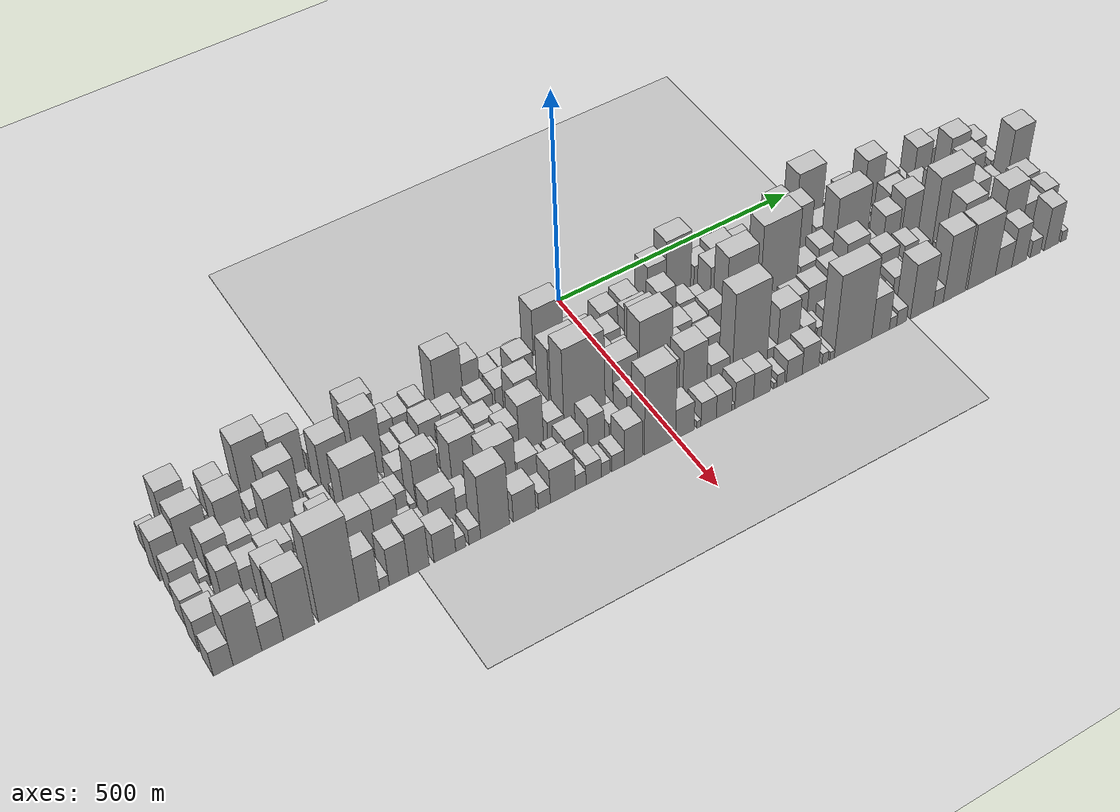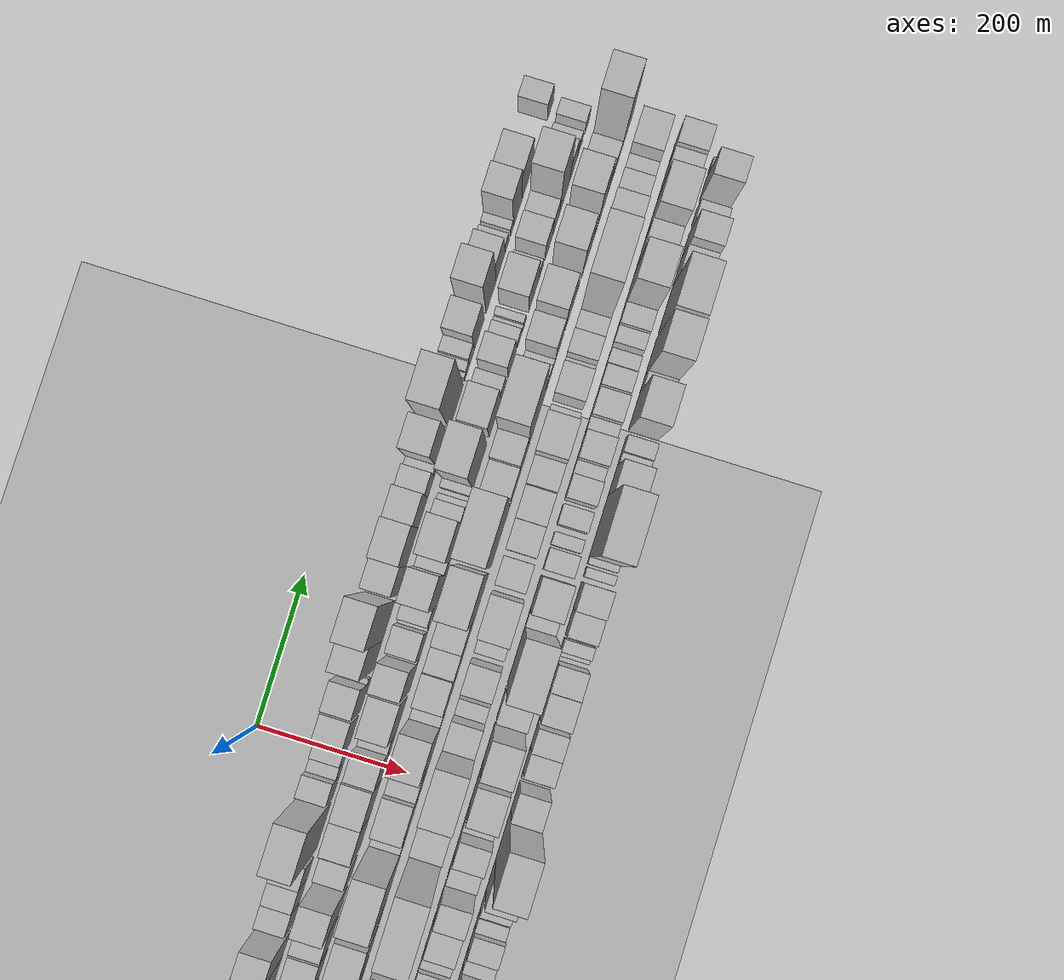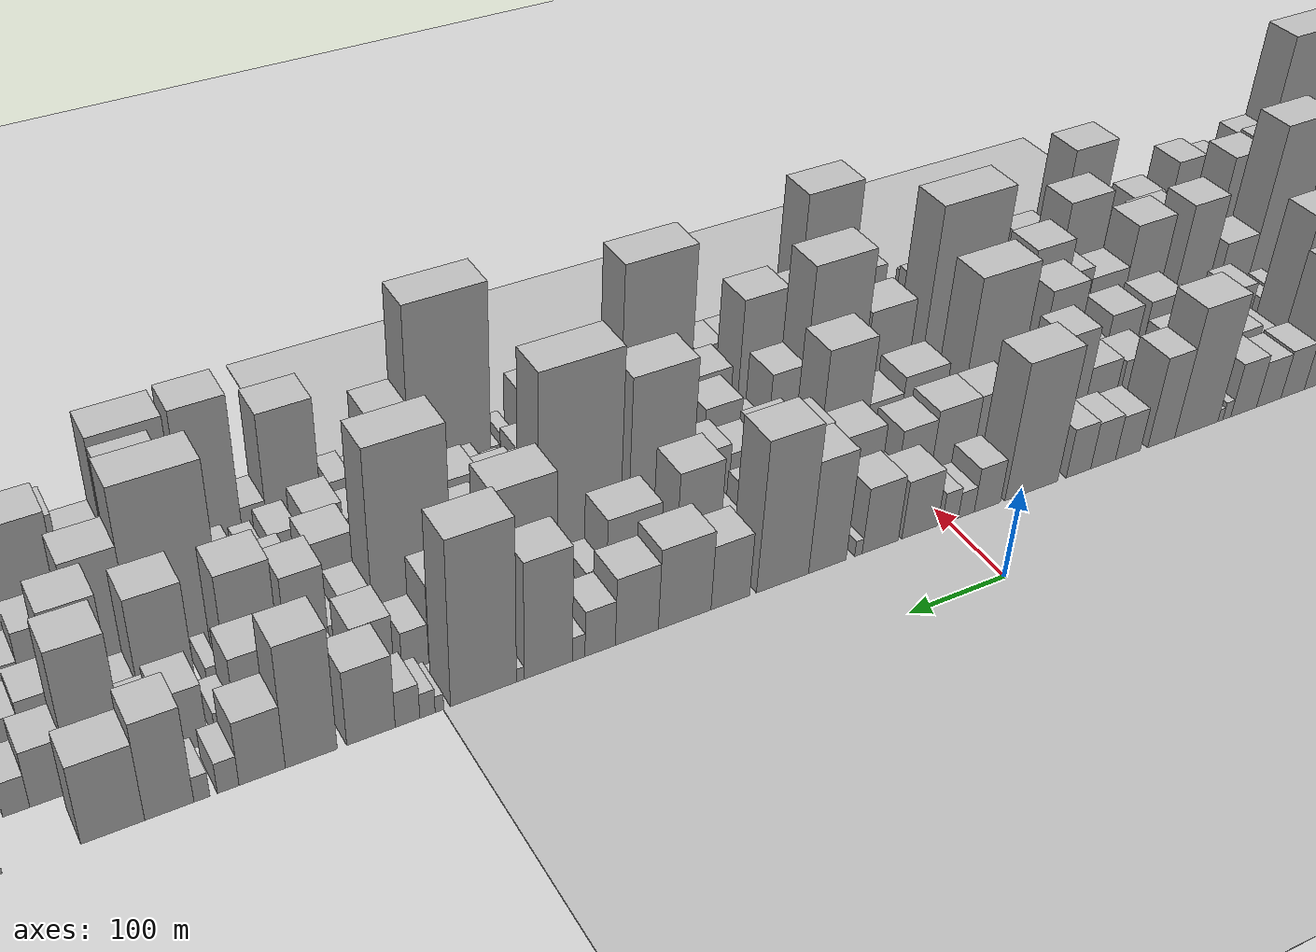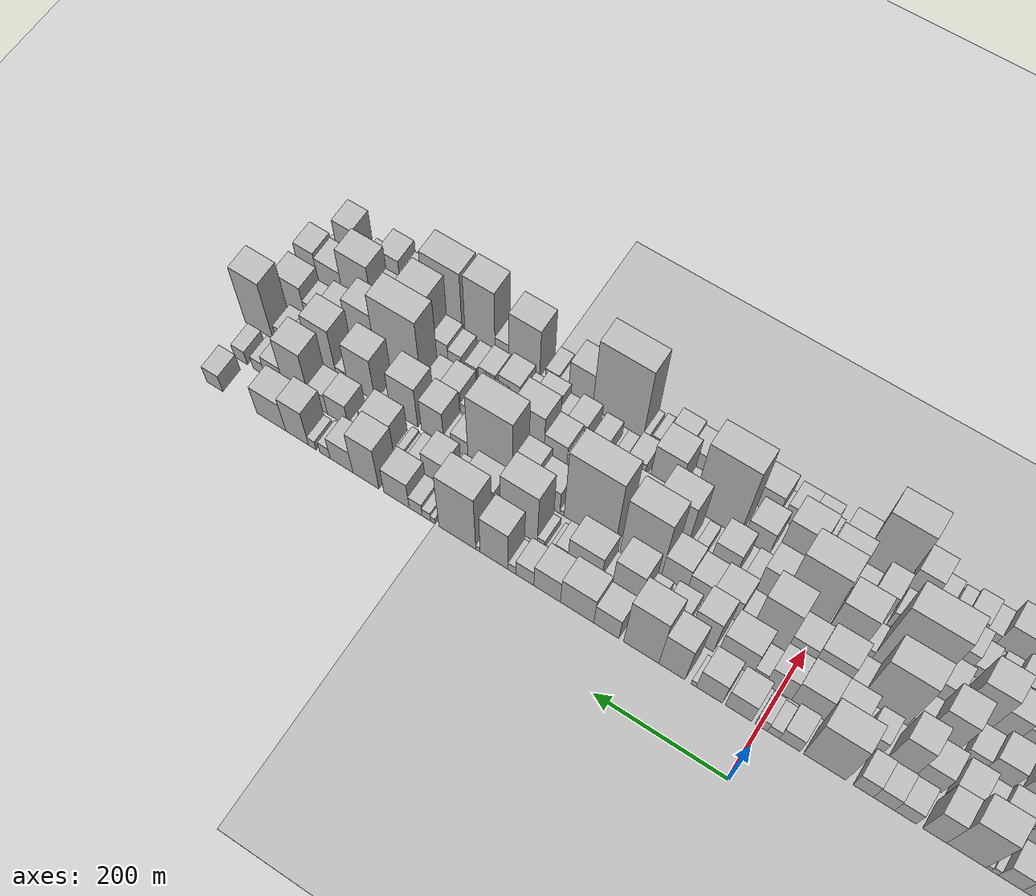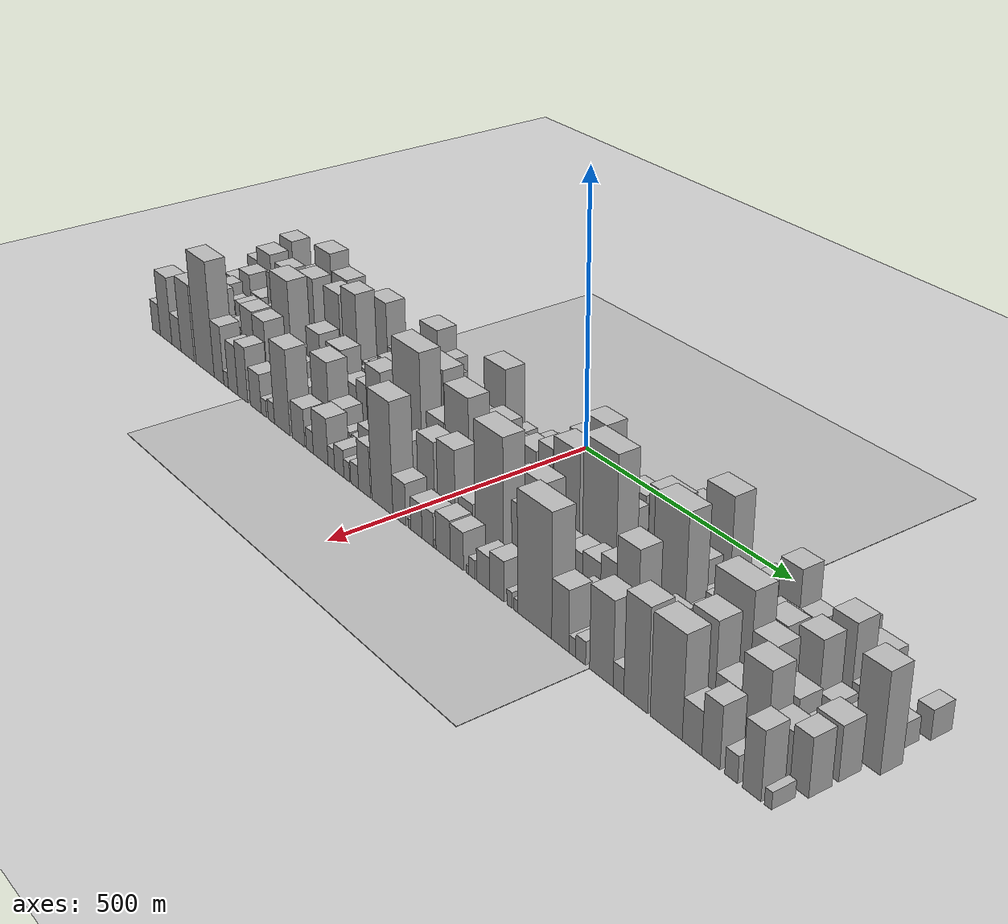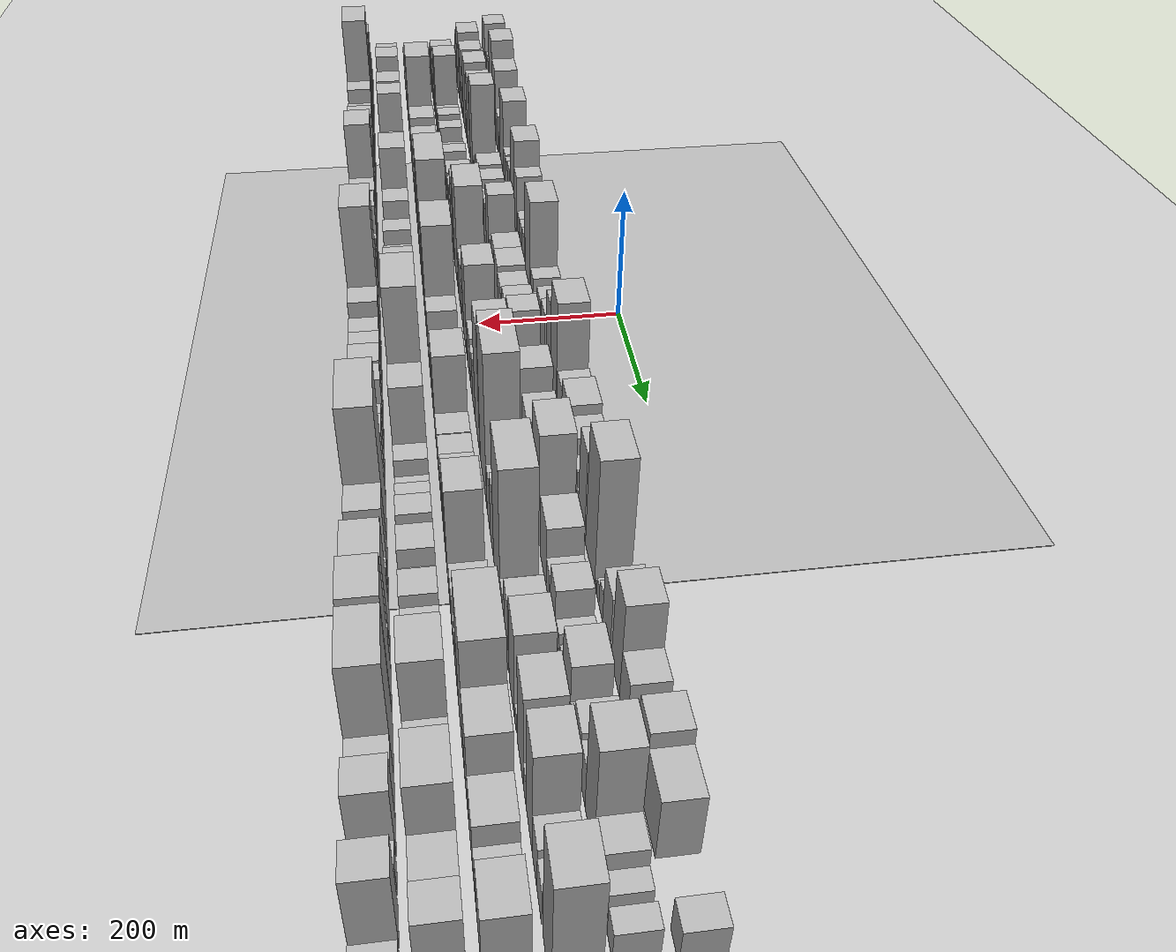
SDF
<?xml version="1.0" encoding="utf-8"?>

<sdf version="1.6">

   <world name="default">

      <gui fullscreen="0">

         <camera name="user_camera">

            <pose>-15 0 4.57585 0 0 0</pose>

            <view_controller>orbit</view_controller>

         </camera>

      </gui>

      <scene>

         <sky>

           <clouds>

             <speed>12</speed>

           </clouds>

         </sky>

         <ambient>0.4 0.4 0.4 1</ambient>

         <background>0.7 0.7 0.7 1</background>

         <shadows>1</shadows>

      </scene>

      <gravity>0 0 -9.8066</gravity>

      <magnetic_field>6e-06 2.3e-05 -4.2e-05</magnetic_field>

      <physics default="0" name="default_physics" type="ode">

         <ode>

            <solver>

               <type>quick</type>

               <iters>10</iters>

               <sor>1.0</sor>

               <use_dynamic_moi_rescaling>0</use_dynamic_moi_rescaling>

            </solver>

            <constraints>

               <cfm>0</cfm>

               <erp>0.2</erp>

               <contact_max_correcting_vel>100</contact_max_correcting_vel>

               <contact_surface_layer>0.001</contact_surface_layer>

            </constraints>

         </ode>

         <max_step_size>0.004</max_step_size>

         <real_time_factor>1</real_time_factor>

         <real_time_update_rate>250</real_time_update_rate>

      </physics>

      <light name="sun" type="directional">

         <cast_shadows>1</cast_shadows>

         <pose>0 0 10 0 0 0</pose>

         <diffuse>0.8 0.8 0.8 1</diffuse>

         <specular>0.2 0.2 0.2 1</specular>

         <attenuation>

            <range>1000</range>

            <constant>0.9</constant>

            <linear>0.01</linear>

            <quadratic>0.001</quadratic>

         </attenuation>

         <direction>-0.5 0.1 -0.9</direction>

      </light>

      <include>

         <name>ground_plane_1</name>

         <uri>model://HANNAS_ground_plane</uri>

         <pose>0 0 0  0 0 0</pose>

      </include>

      <include>

         <name>ground_plane_2</name>

         <uri>model://HANNAS_ground_plane</uri>

         <pose>100 0 0  0 0 0</pose>

      </include>

      <model name="building_1">

         <static>1</static>

         <pose frame="">100.0000 -835.7640 0 0.000000 0.000000 0.000000</pose>

         <link name="link">

            <pose frame="">0 0 25.50 0 0 0</pose>

            <collision name="collision">

               <geometry>

                  <box>

                     <size>40.0000 28.4719 51.0000</size>

                  </box>

               </geometry>

               <max_contacts>10</max_contacts>

               <surface>

                  <contact>

                     <ode/>

                  </contact>

                  <bounce/>

                  <friction>

                     <torsional>

                        <ode/>

                     </torsional>

                     <ode/>

                  </friction>

               </surface>

            </collision>

            <visual name="visual">

               <cast_shadows>0</cast_shadows>

               <geometry>

                  <box>

                     <size>40.0000 28.4719 51.0000</size>

                  </box>

               </geometry>

               <material>

                  <script>

                     <uri>model://HANNAS_wall/materials/scripts</uri>

                     <uri>model://HANNAS_wall/materials/textures</uri>

                     <name>vrc/HANNAS_wall</name>

                  </script>

               </material>

            </visual>

            <self_collide>0</self_collide>

            <enable_wind>0</enable_wind>

            <kinematic>0</kinematic>

         </link>

      </model>

      <model name="building_2">

         <static>1</static>

         <pose frame="">100.0000 -791.8848 0 0.000000 0.000000 0.000000</pose>

         <link name="link">

            <pose frame="">0 0 73.50 0 0 0</pose>

            <collision name="collision">

               <geometry>

                  <box>

                     <size>40.0000 47.2866 147.0000</size>

                  </box>

               </geometry>

               <max_contacts>10</max_contacts>

               <surface>

                  <contact>

                     <ode/>

                  </contact>

                  <bounce/>

                  <friction>

                     <torsional>

                        <ode/>

                     </torsional>

                     <ode/>

                  </friction>

               </surface>

            </collision>

            <visual name="visual">

               <cast_shadows>0</cast_shadows>

               <geometry>

                  <box>

                     <size>40.0000 47.2866 147.0000</size>

                  </box>

               </geometry>

               <material>

                  <script>

                     <uri>model://HANNAS_wall/materials/scripts</uri>

                     <uri>model://HANNAS_wall/materials/textures</uri>

                     <name>vrc/HANNAS_wall</name>

                  </script>

               </material>

            </visual>

            <self_collide>0</self_collide>

            <enable_wind>0</enable_wind>

            <kinematic>0</kinematic>

         </link>

      </model>

      <model name="building_3">

         <static>1</static>

         <pose frame="">100.0000 -763.5734 0 0.000000 0.000000 0.000000</pose>

         <link name="link">

            <pose frame="">0 0 10.50 0 0 0</pose>

            <collision name="collision">

               <geometry>

                  <box>

                     <size>40.0000 9.3361 21.0000</size>

                  </box>

               </geometry>

               <max_contacts>10</max_contacts>

               <surface>

                  <contact>

                     <ode/>

                  </contact>

                  <bounce/>

                  <friction>

                     <torsional>

                        <ode/>

                     </torsional>

                     <ode/>

                  </friction>

               </surface>

            </collision>

            <visual name="visual">

               <cast_shadows>0</cast_shadows>

               <geometry>

                  <box>

                     <size>40.0000 9.3361 21.0000</size>

                  </box>

               </geometry>

               <material>

                  <script>

                     <uri>model://HANNAS_wall/materials/scripts</uri>

                     <uri>model://HANNAS_wall/materials/textures</uri>

                     <name>vrc/HANNAS_wall</name>

                  </script>

               </material>

            </visual>

            <self_collide>0</self_collide>

            <enable_wind>0</enable_wind>

            <kinematic>0</kinematic>

         </link>

      </model>

      <model name="building_4">

         <static>1</static>

         <pose frame="">100.0000 -749.7847 0 0.000000 0.000000 0.000000</pose>

         <link name="link">

            <pose frame="">0 0 18.00 0 0 0</pose>

            <collision name="collision">

               <geometry>

                  <box>

                     <size>40.0000 18.2413 36.0000</size>

                  </box>

               </geometry>

               <max_contacts>10</max_contacts>

               <surface>

                  <contact>

                     <ode/>

                  </contact>

                  <bounce/>

                  <friction>

                     <torsional>

                        <ode/>

                     </torsional>

                     <ode/>

                  </friction>

               </surface>

            </collision>

            <visual name="visual">

               <cast_shadows>0</cast_shadows>

               <geometry>

                  <box>

                     <size>40.0000 18.2413 36.0000</size>

                  </box>

               </geometry>

               <material>

                  <script>

                     <uri>model://HANNAS_wall/materials/scripts</uri>

                     <uri>model://HANNAS_wall/materials/textures</uri>

                     <name>vrc/HANNAS_wall</name>

                  </script>

               </material>

            </visual>

            <self_collide>0</self_collide>

            <enable_wind>0</enable_wind>

            <kinematic>0</kinematic>

         </link>

      </model>

      <model name="building_5">

         <static>1</static>

         <pose frame="">100.0000 -719.0016 0 0.000000 0.000000 0.000000</pose>

         <link name="link">

            <pose frame="">0 0 52.50 0 0 0</pose>

            <collision name="collision">

               <geometry>

                  <box>

                     <size>40.0000 37.3249 105.0000</size>

                  </box>

               </geometry>

               <max_contacts>10</max_contacts>

               <surface>

                  <contact>

                     <ode/>

                  </contact>

                  <bounce/>

                  <friction>

                     <torsional>

                        <ode/>

                     </torsional>

                     <ode/>

                  </friction>

               </surface>

            </collision>

            <visual name="visual">

               <cast_shadows>0</cast_shadows>

               <geometry>

                  <box>

                     <size>40.0000 37.3249 105.0000</size>

                  </box>

               </geometry>

               <material>

                  <script>

                     <uri>model://HANNAS_wall/materials/scripts</uri>

                     <uri>model://HANNAS_wall/materials/textures</uri>

                     <name>vrc/HANNAS_wall</name>

                  </script>

               </material>

            </visual>

            <self_collide>0</self_collide>

            <enable_wind>0</enable_wind>

            <kinematic>0</kinematic>

         </link>

      </model>

      <model name="building_6">

         <static>1</static>

         <pose frame="">100.0000 -689.7990 0 0.000000 0.000000 0.000000</pose>

         <link name="link">

            <pose frame="">0 0 18.00 0 0 0</pose>

            <collision name="collision">

               <geometry>

                  <box>

                     <size>40.0000 21.0802 36.0000</size>

                  </box>

               </geometry>

               <max_contacts>10</max_contacts>

               <surface>

                  <contact>

                     <ode/>

                  </contact>

                  <bounce/>

                  <friction>

                     <torsional>

                        <ode/>

                     </torsional>

                     <ode/>

                  </friction>

               </surface>

            </collision>

            <visual name="visual">

               <cast_shadows>0</cast_shadows>

               <geometry>

                  <box>

                     <size>40.0000 21.0802 36.0000</size>

                  </box>

               </geometry>

               <material>

                  <script>

                     <uri>model://HANNAS_wall/materials/scripts</uri>

                     <uri>model://HANNAS_wall/materials/textures</uri>

                     <name>vrc/HANNAS_wall</name>

                  </script>

               </material>

            </visual>

            <self_collide>0</self_collide>

            <enable_wind>0</enable_wind>

            <kinematic>0</kinematic>

         </link>

      </model>

      <model name="building_7">

         <static>1</static>

         <pose frame="">100.0000 -650.8711 0 0.000000 0.000000 0.000000</pose>

         <link name="link">

            <pose frame="">0 0 85.50 0 0 0</pose>

            <collision name="collision">

               <geometry>

                  <box>

                     <size>40.0000 56.7756 171.0000</size>

                  </box>

               </geometry>

               <max_contacts>10</max_contacts>

               <surface>

                  <contact>

                     <ode/>

                  </contact>

                  <bounce/>

                  <friction>

                     <torsional>

                        <ode/>

                     </torsional>

                     <ode/>

                  </friction>

               </surface>

            </collision>

            <visual name="visual">

               <cast_shadows>0</cast_shadows>

               <geometry>

                  <box>

                     <size>40.0000 56.7756 171.0000</size>

                  </box>

               </geometry>

               <material>

                  <script>

                     <uri>model://HANNAS_wall/materials/scripts</uri>

                     <uri>model://HANNAS_wall/materials/textures</uri>

                     <name>vrc/HANNAS_wall</name>

                  </script>

               </material>

            </visual>

            <self_collide>0</self_collide>

            <enable_wind>0</enable_wind>

            <kinematic>0</kinematic>

         </link>

      </model>

      <model name="building_8">

         <static>1</static>

         <pose frame="">100.0000 -591.9886 0 0.000000 0.000000 0.000000</pose>

         <link name="link">

            <pose frame="">0 0 69.00 0 0 0</pose>

            <collision name="collision">

               <geometry>

                  <box>

                     <size>40.0000 54.9893 138.0000</size>

                  </box>

               </geometry>

               <max_contacts>10</max_contacts>

               <surface>

                  <contact>

                     <ode/>

                  </contact>

                  <bounce/>

                  <friction>

                     <torsional>

                        <ode/>

                     </torsional>

                     <ode/>

                  </friction>

               </surface>

            </collision>

            <visual name="visual">

               <cast_shadows>0</cast_shadows>

               <geometry>

                  <box>

                     <size>40.0000 54.9893 138.0000</size>

                  </box>

               </geometry>

               <material>

                  <script>

                     <uri>model://HANNAS_wall/materials/scripts</uri>

                     <uri>model://HANNAS_wall/materials/textures</uri>

                     <name>vrc/HANNAS_wall</name>

                  </script>

               </material>

            </visual>

            <self_collide>0</self_collide>

            <enable_wind>0</enable_wind>

            <kinematic>0</kinematic>

         </link>

      </model>

      <model name="building_9">

         <static>1</static>

         <pose frame="">100.0000 -541.9418 0 0.000000 0.000000 0.000000</pose>

         <link name="link">

            <pose frame="">0 0 34.50 0 0 0</pose>

            <collision name="collision">

               <geometry>

                  <box>

                     <size>40.0000 35.1044 69.0000</size>

                  </box>

               </geometry>

               <max_contacts>10</max_contacts>

               <surface>

                  <contact>

                     <ode/>

                  </contact>

                  <bounce/>

                  <friction>

                     <torsional>

                        <ode/>

                     </torsional>

                     <ode/>

                  </friction>

               </surface>

            </collision>

            <visual name="visual">

               <cast_shadows>0</cast_shadows>

               <geometry>

                  <box>

                     <size>40.0000 35.1044 69.0000</size>

                  </box>

               </geometry>

               <material>

                  <script>

                     <uri>model://HANNAS_wall/materials/scripts</uri>

                     <uri>model://HANNAS_wall/materials/textures</uri>

                     <name>vrc/HANNAS_wall</name>

                  </script>

               </material>

            </visual>

            <self_collide>0</self_collide>

            <enable_wind>0</enable_wind>

            <kinematic>0</kinematic>

         </link>

      </model>

      <model name="building_10">

         <static>1</static>

         <pose frame="">100.0000 -502.9221 0 0.000000 0.000000 0.000000</pose>

         <link name="link">

            <pose frame="">0 0 22.50 0 0 0</pose>

            <collision name="collision">

               <geometry>

                  <box>

                     <size>40.0000 22.9349 45.0000</size>

                  </box>

               </geometry>

               <max_contacts>10</max_contacts>

               <surface>

                  <contact>

                     <ode/>

                  </contact>

                  <bounce/>

                  <friction>

                     <torsional>

                        <ode/>

                     </torsional>

                     <ode/>

                  </friction>

               </surface>

            </collision>

            <visual name="visual">

               <cast_shadows>0</cast_shadows>

               <geometry>

                  <box>

                     <size>40.0000 22.9349 45.0000</size>

                  </box>

               </geometry>

               <material>

                  <script>

                     <uri>model://HANNAS_wall/materials/scripts</uri>

                     <uri>model://HANNAS_wall/materials/textures</uri>

                     <name>vrc/HANNAS_wall</name>

                  </script>

               </material>

            </visual>

            <self_collide>0</self_collide>

            <enable_wind>0</enable_wind>

            <kinematic>0</kinematic>

         </link>

      </model>

      <model name="building_11">

         <static>1</static>

         <pose frame="">100.0000 -458.6440 0 0.000000 0.000000 0.000000</pose>

         <link name="link">

            <pose frame="">0 0 70.50 0 0 0</pose>

            <collision name="collision">

               <geometry>

                  <box>

                     <size>40.0000 55.6212 141.0000</size>

                  </box>

               </geometry>

               <max_contacts>10</max_contacts>

               <surface>

                  <contact>

                     <ode/>

                  </contact>

                  <bounce/>

                  <friction>

                     <torsional>

                        <ode/>

                     </torsional>

                     <ode/>

                  </friction>

               </surface>

            </collision>

            <visual name="visual">

               <cast_shadows>0</cast_shadows>

               <geometry>

                  <box>

                     <size>40.0000 55.6212 141.0000</size>

                  </box>

               </geometry>

               <material>

                  <script>

                     <uri>model://HANNAS_wall/materials/scripts</uri>

                     <uri>model://HANNAS_wall/materials/textures</uri>

                     <name>vrc/HANNAS_wall</name>

                  </script>

               </material>

            </visual>

            <self_collide>0</self_collide>

            <enable_wind>0</enable_wind>

            <kinematic>0</kinematic>

         </link>

      </model>

      <model name="building_12">

         <static>1</static>

         <pose frame="">100.0000 -415.4937 0 0.000000 0.000000 0.000000</pose>

         <link name="link">

            <pose frame="">0 0 28.50 0 0 0</pose>

            <collision name="collision">

               <geometry>

                  <box>

                     <size>40.0000 30.6795 57.0000</size>

                  </box>

               </geometry>

               <max_contacts>10</max_contacts>

               <surface>

                  <contact>

                     <ode/>

                  </contact>

                  <bounce/>

                  <friction>

                     <torsional>

                        <ode/>

                     </torsional>

                     <ode/>

                  </friction>

               </surface>

            </collision>

            <visual name="visual">

               <cast_shadows>0</cast_shadows>

               <geometry>

                  <box>

                     <size>40.0000 30.6795 57.0000</size>

                  </box>

               </geometry>

               <material>

                  <script>

                     <uri>model://HANNAS_wall/materials/scripts</uri>

                     <uri>model://HANNAS_wall/materials/textures</uri>

                     <name>vrc/HANNAS_wall</name>

                  </script>

               </material>

            </visual>

            <self_collide>0</self_collide>

            <enable_wind>0</enable_wind>

            <kinematic>0</kinematic>

         </link>

      </model>

      <model name="building_13">

         <static>1</static>

         <pose frame="">100.0000 -384.3324 0 0.000000 0.000000 0.000000</pose>

         <link name="link">

            <pose frame="">0 0 27.00 0 0 0</pose>

            <collision name="collision">

               <geometry>

                  <box>

                     <size>40.0000 31.6431 54.0000</size>

                  </box>

               </geometry>

               <max_contacts>10</max_contacts>

               <surface>

                  <contact>

                     <ode/>

                  </contact>

                  <bounce/>

                  <friction>

                     <torsional>

                        <ode/>

                     </torsional>

                     <ode/>

                  </friction>

               </surface>

            </collision>

            <visual name="visual">

               <cast_shadows>0</cast_shadows>

               <geometry>

                  <box>

                     <size>40.0000 31.6431 54.0000</size>

                  </box>

               </geometry>

               <material>

                  <script>

                     <uri>model://HANNAS_wall/materials/scripts</uri>

                     <uri>model://HANNAS_wall/materials/textures</uri>

                     <name>vrc/HANNAS_wall</name>

                  </script>

               </material>

            </visual>

            <self_collide>0</self_collide>

            <enable_wind>0</enable_wind>

            <kinematic>0</kinematic>

         </link>

      </model>

      <model name="building_14">

         <static>1</static>

         <pose frame="">100.0000 -352.0110 0 0.000000 0.000000 0.000000</pose>

         <link name="link">

            <pose frame="">0 0 31.50 0 0 0</pose>

            <collision name="collision">

               <geometry>

                  <box>

                     <size>40.0000 32.9997 63.0000</size>

                  </box>

               </geometry>

               <max_contacts>10</max_contacts>

               <surface>

                  <contact>

                     <ode/>

                  </contact>

                  <bounce/>

                  <friction>

                     <torsional>

                        <ode/>

                     </torsional>

                     <ode/>

                  </friction>

               </surface>

            </collision>

            <visual name="visual">

               <cast_shadows>0</cast_shadows>

               <geometry>

                  <box>

                     <size>40.0000 32.9997 63.0000</size>

                  </box>

               </geometry>

               <material>

                  <script>

                     <uri>model://HANNAS_wall/materials/scripts</uri>

                     <uri>model://HANNAS_wall/materials/textures</uri>

                     <name>vrc/HANNAS_wall</name>

                  </script>

               </material>

            </visual>

            <self_collide>0</self_collide>

            <enable_wind>0</enable_wind>

            <kinematic>0</kinematic>

         </link>

      </model>

      <model name="building_15">

         <static>1</static>

         <pose frame="">100.0000 -330.5286 0 0.000000 0.000000 0.000000</pose>

         <link name="link">

            <pose frame="">0 0 10.50 0 0 0</pose>

            <collision name="collision">

               <geometry>

                  <box>

                     <size>40.0000 9.9651 21.0000</size>

                  </box>

               </geometry>

               <max_contacts>10</max_contacts>

               <surface>

                  <contact>

                     <ode/>

                  </contact>

                  <bounce/>

                  <friction>

                     <torsional>

                        <ode/>

                     </torsional>

                     <ode/>

                  </friction>

               </surface>

            </collision>

            <visual name="visual">

               <cast_shadows>0</cast_shadows>

               <geometry>

                  <box>

                     <size>40.0000 9.9651 21.0000</size>

                  </box>

               </geometry>

               <material>

                  <script>

                     <uri>model://HANNAS_wall/materials/scripts</uri>

                     <uri>model://HANNAS_wall/materials/textures</uri>

                     <name>vrc/HANNAS_wall</name>

                  </script>

               </material>

            </visual>

            <self_collide>0</self_collide>

            <enable_wind>0</enable_wind>

            <kinematic>0</kinematic>

         </link>

      </model>

      <model name="building_16">

         <static>1</static>

         <pose frame="">100.0000 -322.3145 0 0.000000 0.000000 0.000000</pose>

         <link name="link">

            <pose frame="">0 0 7.50 0 0 0</pose>

            <collision name="collision">

               <geometry>

                  <box>

                     <size>40.0000 6.4632 15.0000</size>

                  </box>

               </geometry>

               <max_contacts>10</max_contacts>

               <surface>

                  <contact>

                     <ode/>

                  </contact>

                  <bounce/>

                  <friction>

                     <torsional>

                        <ode/>

                     </torsional>

                     <ode/>

                  </friction>

               </surface>

            </collision>

            <visual name="visual">

               <cast_shadows>0</cast_shadows>

               <geometry>

                  <box>

                     <size>40.0000 6.4632 15.0000</size>

                  </box>

               </geometry>

               <material>

                  <script>

                     <uri>model://HANNAS_wall/materials/scripts</uri>

                     <uri>model://HANNAS_wall/materials/textures</uri>

                     <name>vrc/HANNAS_wall</name>

                  </script>

               </material>

            </visual>

            <self_collide>0</self_collide>

            <enable_wind>0</enable_wind>

            <kinematic>0</kinematic>

         </link>

      </model>

      <model name="building_17">

         <static>1</static>

         <pose frame="">100.0000 -292.0841 0 0.000000 0.000000 0.000000</pose>

         <link name="link">

            <pose frame="">0 0 75.00 0 0 0</pose>

            <collision name="collision">

               <geometry>

                  <box>

                     <size>40.0000 53.9976 150.0000</size>

                  </box>

               </geometry>

               <max_contacts>10</max_contacts>

               <surface>

                  <contact>

                     <ode/>

                  </contact>

                  <bounce/>

                  <friction>

                     <torsional>

                        <ode/>

                     </torsional>

                     <ode/>

                  </friction>

               </surface>

            </collision>

            <visual name="visual">

               <cast_shadows>0</cast_shadows>

               <geometry>

                  <box>

                     <size>40.0000 53.9976 150.0000</size>

                  </box>

               </geometry>

               <material>

                  <script>

                     <uri>model://HANNAS_wall/materials/scripts</uri>

                     <uri>model://HANNAS_wall/materials/textures</uri>

                     <name>vrc/HANNAS_wall</name>

                  </script>

               </material>

            </visual>

            <self_collide>0</self_collide>

            <enable_wind>0</enable_wind>

            <kinematic>0</kinematic>

         </link>

      </model>

      <model name="building_18">

         <static>1</static>

         <pose frame="">100.0000 -248.5190 0 0.000000 0.000000 0.000000</pose>

         <link name="link">

            <pose frame="">0 0 52.50 0 0 0</pose>

            <collision name="collision">

               <geometry>

                  <box>

                     <size>40.0000 33.1326 105.0000</size>

                  </box>

               </geometry>

               <max_contacts>10</max_contacts>

               <surface>

                  <contact>

                     <ode/>

                  </contact>

                  <bounce/>

                  <friction>

                     <torsional>

                        <ode/>

                     </torsional>

                     <ode/>

                  </friction>

               </surface>

            </collision>

            <visual name="visual">

               <cast_shadows>0</cast_shadows>

               <geometry>

                  <box>

                     <size>40.0000 33.1326 105.0000</size>

                  </box>

               </geometry>

               <material>

                  <script>

                     <uri>model://HANNAS_wall/materials/scripts</uri>

                     <uri>model://HANNAS_wall/materials/textures</uri>

                     <name>vrc/HANNAS_wall</name>

                  </script>

               </material>

            </visual>

            <self_collide>0</self_collide>

            <enable_wind>0</enable_wind>

            <kinematic>0</kinematic>

         </link>

      </model>

      <model name="building_19">

         <static>1</static>

         <pose frame="">100.0000 -207.8662 0 0.000000 0.000000 0.000000</pose>

         <link name="link">

            <pose frame="">0 0 25.50 0 0 0</pose>

            <collision name="collision">

               <geometry>

                  <box>

                     <size>40.0000 30.1730 51.0000</size>

                  </box>

               </geometry>

               <max_contacts>10</max_contacts>

               <surface>

                  <contact>

                     <ode/>

                  </contact>

                  <bounce/>

                  <friction>

                     <torsional>

                        <ode/>

                     </torsional>

                     <ode/>

                  </friction>

               </surface>

            </collision>

            <visual name="visual">

               <cast_shadows>0</cast_shadows>

               <geometry>

                  <box>

                     <size>40.0000 30.1730 51.0000</size>

                  </box>

               </geometry>

               <material>

                  <script>

                     <uri>model://HANNAS_wall/materials/scripts</uri>

                     <uri>model://HANNAS_wall/materials/textures</uri>

                     <name>vrc/HANNAS_wall</name>

                  </script>

               </material>

            </visual>

            <self_collide>0</self_collide>

            <enable_wind>0</enable_wind>

            <kinematic>0</kinematic>

         </link>

      </model>

      <model name="building_20">

         <static>1</static>

         <pose frame="">100.0000 -178.0327 0 0.000000 0.000000 0.000000</pose>

         <link name="link">

            <pose frame="">0 0 27.00 0 0 0</pose>

            <collision name="collision">

               <geometry>

                  <box>

                     <size>40.0000 29.4939 54.0000</size>

                  </box>

               </geometry>

               <max_contacts>10</max_contacts>

               <surface>

                  <contact>

                     <ode/>

                  </contact>

                  <bounce/>

                  <friction>

                     <torsional>

                        <ode/>

                     </torsional>

                     <ode/>

                  </friction>

               </surface>

            </collision>

            <visual name="visual">

               <cast_shadows>0</cast_shadows>

               <geometry>

                  <box>

                     <size>40.0000 29.4939 54.0000</size>

                  </box>

               </geometry>

               <material>

                  <script>

                     <uri>model://HANNAS_wall/materials/scripts</uri>

                     <uri>model://HANNAS_wall/materials/textures</uri>

                     <name>vrc/HANNAS_wall</name>

                  </script>

               </material>

            </visual>

            <self_collide>0</self_collide>

            <enable_wind>0</enable_wind>

            <kinematic>0</kinematic>

         </link>

      </model>

      <model name="building_21">

         <static>1</static>

         <pose frame="">100.0000 -148.8522 0 0.000000 0.000000 0.000000</pose>

         <link name="link">

            <pose frame="">0 0 28.50 0 0 0</pose>

            <collision name="collision">

               <geometry>

                  <box>

                     <size>40.0000 28.8671 57.0000</size>

                  </box>

               </geometry>

               <max_contacts>10</max_contacts>

               <surface>

                  <contact>

                     <ode/>

                  </contact>

                  <bounce/>

                  <friction>

                     <torsional>

                        <ode/>

                     </torsional>

                     <ode/>

                  </friction>

               </surface>

            </collision>

            <visual name="visual">

               <cast_shadows>0</cast_shadows>

               <geometry>

                  <box>

                     <size>40.0000 28.8671 57.0000</size>

                  </box>

               </geometry>

               <material>

                  <script>

                     <uri>model://HANNAS_wall/materials/scripts</uri>

                     <uri>model://HANNAS_wall/materials/textures</uri>

                     <name>vrc/HANNAS_wall</name>

                  </script>

               </material>

            </visual>

            <self_collide>0</self_collide>

            <enable_wind>0</enable_wind>

            <kinematic>0</kinematic>

         </link>

      </model>

      <model name="building_22">

         <static>1</static>

         <pose frame="">100.0000 -93.9196 0 0.000000 0.000000 0.000000</pose>

         <link name="link">

            <pose frame="">0 0 78.00 0 0 0</pose>

            <collision name="collision">

               <geometry>

                  <box>

                     <size>40.0000 60.9980 156.0000</size>

                  </box>

               </geometry>

               <max_contacts>10</max_contacts>

               <surface>

                  <contact>

                     <ode/>

                  </contact>

                  <bounce/>

                  <friction>

                     <torsional>

                        <ode/>

                     </torsional>

                     <ode/>

                  </friction>

               </surface>

            </collision>

            <visual name="visual">

               <cast_shadows>0</cast_shadows>

               <geometry>

                  <box>

                     <size>40.0000 60.9980 156.0000</size>

                  </box>

               </geometry>

               <material>

                  <script>

                     <uri>model://HANNAS_wall/materials/scripts</uri>

                     <uri>model://HANNAS_wall/materials/textures</uri>

                     <name>vrc/HANNAS_wall</name>

                  </script>

               </material>

            </visual>

            <self_collide>0</self_collide>

            <enable_wind>0</enable_wind>

            <kinematic>0</kinematic>

         </link>

      </model>

      <model name="building_23">

         <static>1</static>

         <pose frame="">100.0000 -43.6051 0 0.000000 0.000000 0.000000</pose>

         <link name="link">

            <pose frame="">0 0 25.50 0 0 0</pose>

            <collision name="collision">

               <geometry>

                  <box>

                     <size>40.0000 29.6312 51.0000</size>

                  </box>

               </geometry>

               <max_contacts>10</max_contacts>

               <surface>

                  <contact>

                     <ode/>

                  </contact>

                  <bounce/>

                  <friction>

                     <torsional>

                        <ode/>

                     </torsional>

                     <ode/>

                  </friction>

               </surface>

            </collision>

            <visual name="visual">

               <cast_shadows>0</cast_shadows>

               <geometry>

                  <box>

                     <size>40.0000 29.6312 51.0000</size>

                  </box>

               </geometry>

               <material>

                  <script>

                     <uri>model://HANNAS_wall/materials/scripts</uri>

                     <uri>model://HANNAS_wall/materials/textures</uri>

                     <name>vrc/HANNAS_wall</name>

                  </script>

               </material>

            </visual>

            <self_collide>0</self_collide>

            <enable_wind>0</enable_wind>

            <kinematic>0</kinematic>

         </link>

      </model>

      <model name="building_24">

         <static>1</static>

         <pose frame="">100.0000 -19.9299 0 0.000000 0.000000 0.000000</pose>

         <link name="link">

            <pose frame="">0 0 15.00 0 0 0</pose>

            <collision name="collision">

               <geometry>

                  <box>

                     <size>40.0000 17.7191 30.0000</size>

                  </box>

               </geometry>

               <max_contacts>10</max_contacts>

               <surface>

                  <contact>

                     <ode/>

                  </contact>

                  <bounce/>

                  <friction>

                     <torsional>

                        <ode/>

                     </torsional>

                     <ode/>

                  </friction>

               </surface>

            </collision>

            <visual name="visual">

               <cast_shadows>0</cast_shadows>

               <geometry>

                  <box>

                     <size>40.0000 17.7191 30.0000</size>

                  </box>

               </geometry>

               <material>

                  <script>

                     <uri>model://HANNAS_wall/materials/scripts</uri>

                     <uri>model://HANNAS_wall/materials/textures</uri>

                     <name>vrc/HANNAS_wall</name>

                  </script>

               </material>

            </visual>

            <self_collide>0</self_collide>

            <enable_wind>0</enable_wind>

            <kinematic>0</kinematic>

         </link>

      </model>

      <model name="building_25">

         <static>1</static>

         <pose frame="">100.0000 -2.0524 0 0.000000 0.000000 0.000000</pose>

         <link name="link">

            <pose frame="">0 0 18.00 0 0 0</pose>

            <collision name="collision">

               <geometry>

                  <box>

                     <size>40.0000 18.0360 36.0000</size>

                  </box>

               </geometry>

               <max_contacts>10</max_contacts>

               <surface>

                  <contact>

                     <ode/>

                  </contact>

                  <bounce/>

                  <friction>

                     <torsional>

                        <ode/>

                     </torsional>

                     <ode/>

                  </friction>

               </surface>

            </collision>

            <visual name="visual">

               <cast_shadows>0</cast_shadows>

               <geometry>

                  <box>

                     <size>40.0000 18.0360 36.0000</size>

                  </box>

               </geometry>

               <material>

                  <script>

                     <uri>model://HANNAS_wall/materials/scripts</uri>

                     <uri>model://HANNAS_wall/materials/textures</uri>

                     <name>vrc/HANNAS_wall</name>

                  </script>

               </material>

            </visual>

            <self_collide>0</self_collide>

            <enable_wind>0</enable_wind>

            <kinematic>0</kinematic>

         </link>

      </model>

      <model name="building_26">

         <static>1</static>

         <pose frame="">100.0000 31.4561 0 0.000000 0.000000 0.000000</pose>

         <link name="link">

            <pose frame="">0 0 33.00 0 0 0</pose>

            <collision name="collision">

               <geometry>

                  <box>

                     <size>40.0000 38.9810 66.0000</size>

                  </box>

               </geometry>

               <max_contacts>10</max_contacts>

               <surface>

                  <contact>

                     <ode/>

                  </contact>

                  <bounce/>

                  <friction>

                     <torsional>

                        <ode/>

                     </torsional>

                     <ode/>

                  </friction>

               </surface>

            </collision>

            <visual name="visual">

               <cast_shadows>0</cast_shadows>

               <geometry>

                  <box>

                     <size>40.0000 38.9810 66.0000</size>

                  </box>

               </geometry>

               <material>

                  <script>

                     <uri>model://HANNAS_wall/materials/scripts</uri>

                     <uri>model://HANNAS_wall/materials/textures</uri>

                     <name>vrc/HANNAS_wall</name>

                  </script>

               </material>

            </visual>

            <self_collide>0</self_collide>

            <enable_wind>0</enable_wind>

            <kinematic>0</kinematic>

         </link>

      </model>

      <model name="building_27">

         <static>1</static>

         <pose frame="">100.0000 74.3089 0 0.000000 0.000000 0.000000</pose>

         <link name="link">

            <pose frame="">0 0 37.50 0 0 0</pose>

            <collision name="collision">

               <geometry>

                  <box>

                     <size>40.0000 38.7246 75.0000</size>

                  </box>

               </geometry>

               <max_contacts>10</max_contacts>

               <surface>

                  <contact>

                     <ode/>

                  </contact>

                  <bounce/>

                  <friction>

                     <torsional>

                        <ode/>

                     </torsional>

                     <ode/>

                  </friction>

               </surface>

            </collision>

            <visual name="visual">

               <cast_shadows>0</cast_shadows>

               <geometry>

                  <box>

                     <size>40.0000 38.7246 75.0000</size>

                  </box>

               </geometry>

               <material>

                  <script>

                     <uri>model://HANNAS_wall/materials/scripts</uri>

                     <uri>model://HANNAS_wall/materials/textures</uri>

                     <name>vrc/HANNAS_wall</name>

                  </script>

               </material>

            </visual>

            <self_collide>0</self_collide>

            <enable_wind>0</enable_wind>

            <kinematic>0</kinematic>

         </link>

      </model>

      <model name="building_28">

         <static>1</static>

         <pose frame="">100.0000 97.6655 0 0.000000 0.000000 0.000000</pose>

         <link name="link">

            <pose frame="">0 0 9.00 0 0 0</pose>

            <collision name="collision">

               <geometry>

                  <box>

                     <size>40.0000 7.9885 18.0000</size>

                  </box>

               </geometry>

               <max_contacts>10</max_contacts>

               <surface>

                  <contact>

                     <ode/>

                  </contact>

                  <bounce/>

                  <friction>

                     <torsional>

                        <ode/>

                     </torsional>

                     <ode/>

                  </friction>

               </surface>

            </collision>

            <visual name="visual">

               <cast_shadows>0</cast_shadows>

               <geometry>

                  <box>

                     <size>40.0000 7.9885 18.0000</size>

                  </box>

               </geometry>

               <material>

                  <script>

                     <uri>model://HANNAS_wall/materials/scripts</uri>

                     <uri>model://HANNAS_wall/materials/textures</uri>

                     <name>vrc/HANNAS_wall</name>

                  </script>

               </material>

            </visual>

            <self_collide>0</self_collide>

            <enable_wind>0</enable_wind>

            <kinematic>0</kinematic>

         </link>

      </model>

      <model name="building_29">

         <static>1</static>

         <pose frame="">100.0000 130.3500 0 0.000000 0.000000 0.000000</pose>

         <link name="link">

            <pose frame="">0 0 63.00 0 0 0</pose>

            <collision name="collision">

               <geometry>

                  <box>

                     <size>40.0000 39.3806 126.0000</size>

                  </box>

               </geometry>

               <max_contacts>10</max_contacts>

               <surface>

                  <contact>

                     <ode/>

                  </contact>

                  <bounce/>

                  <friction>

                     <torsional>

                        <ode/>

                     </torsional>

                     <ode/>

                  </friction>

               </surface>

            </collision>

            <visual name="visual">

               <cast_shadows>0</cast_shadows>

               <geometry>

                  <box>

                     <size>40.0000 39.3806 126.0000</size>

                  </box>

               </geometry>

               <material>

                  <script>

                     <uri>model://HANNAS_wall/materials/scripts</uri>

                     <uri>model://HANNAS_wall/materials/textures</uri>

                     <name>vrc/HANNAS_wall</name>

                  </script>

               </material>

            </visual>

            <self_collide>0</self_collide>

            <enable_wind>0</enable_wind>

            <kinematic>0</kinematic>

         </link>

      </model>

      <model name="building_30">

         <static>1</static>

         <pose frame="">100.0000 176.7575 0 0.000000 0.000000 0.000000</pose>

         <link name="link">

            <pose frame="">0 0 84.00 0 0 0</pose>

            <collision name="collision">

               <geometry>

                  <box>

                     <size>40.0000 53.4345 168.0000</size>

                  </box>

               </geometry>

               <max_contacts>10</max_contacts>

               <surface>

                  <contact>

                     <ode/>

                  </contact>

                  <bounce/>

                  <friction>

                     <torsional>

                        <ode/>

                     </torsional>

                     <ode/>

                  </friction>

               </surface>

            </collision>

            <visual name="visual">

               <cast_shadows>0</cast_shadows>

               <geometry>

                  <box>

                     <size>40.0000 53.4345 168.0000</size>

                  </box>

               </geometry>

               <material>

                  <script>

                     <uri>model://HANNAS_wall/materials/scripts</uri>

                     <uri>model://HANNAS_wall/materials/textures</uri>

                     <name>vrc/HANNAS_wall</name>

                  </script>

               </material>

            </visual>

            <self_collide>0</self_collide>

            <enable_wind>0</enable_wind>

            <kinematic>0</kinematic>

         </link>

      </model>

      <model name="building_31">

         <static>1</static>

         <pose frame="">100.0000 229.8142 0 0.000000 0.000000 0.000000</pose>

         <link name="link">

            <pose frame="">0 0 36.00 0 0 0</pose>

            <collision name="collision">

               <geometry>

                  <box>

                     <size>40.0000 38.6788 72.0000</size>

                  </box>

               </geometry>

               <max_contacts>10</max_contacts>

               <surface>

                  <contact>

                     <ode/>

                  </contact>

                  <bounce/>

                  <friction>

                     <torsional>

                        <ode/>

                     </torsional>

                     <ode/>

                  </friction>

               </surface>

            </collision>

            <visual name="visual">

               <cast_shadows>0</cast_shadows>

               <geometry>

                  <box>

                     <size>40.0000 38.6788 72.0000</size>

                  </box>

               </geometry>

               <material>

                  <script>

                     <uri>model://HANNAS_wall/materials/scripts</uri>

                     <uri>model://HANNAS_wall/materials/textures</uri>

                     <name>vrc/HANNAS_wall</name>

                  </script>

               </material>

            </visual>

            <self_collide>0</self_collide>

            <enable_wind>0</enable_wind>

            <kinematic>0</kinematic>

         </link>

      </model>

      <model name="building_32">

         <static>1</static>

         <pose frame="">100.0000 275.0135 0 0.000000 0.000000 0.000000</pose>

         <link name="link">

            <pose frame="">0 0 45.00 0 0 0</pose>

            <collision name="collision">

               <geometry>

                  <box>

                     <size>40.0000 51.7199 90.0000</size>

                  </box>

               </geometry>

               <max_contacts>10</max_contacts>

               <surface>

                  <contact>

                     <ode/>

                  </contact>

                  <bounce/>

                  <friction>

                     <torsional>

                        <ode/>

                     </torsional>

                     <ode/>

                  </friction>

               </surface>

            </collision>

            <visual name="visual">

               <cast_shadows>0</cast_shadows>

               <geometry>

                  <box>

                     <size>40.0000 51.7199 90.0000</size>

                  </box>

               </geometry>

               <material>

                  <script>

                     <uri>model://HANNAS_wall/materials/scripts</uri>

                     <uri>model://HANNAS_wall/materials/textures</uri>

                     <name>vrc/HANNAS_wall</name>

                  </script>

               </material>

            </visual>

            <self_collide>0</self_collide>

            <enable_wind>0</enable_wind>

            <kinematic>0</kinematic>

         </link>

      </model>

      <model name="building_33">

         <static>1</static>

         <pose frame="">100.0000 321.5605 0 0.000000 0.000000 0.000000</pose>

         <link name="link">

            <pose frame="">0 0 37.50 0 0 0</pose>

            <collision name="collision">

               <geometry>

                  <box>

                     <size>40.0000 41.3742 75.0000</size>

                  </box>

               </geometry>

               <max_contacts>10</max_contacts>

               <surface>

                  <contact>

                     <ode/>

                  </contact>

                  <bounce/>

                  <friction>

                     <torsional>

                        <ode/>

                     </torsional>

                     <ode/>

                  </friction>

               </surface>

            </collision>

            <visual name="visual">

               <cast_shadows>0</cast_shadows>

               <geometry>

                  <box>

                     <size>40.0000 41.3742 75.0000</size>

                  </box>

               </geometry>

               <material>

                  <script>

                     <uri>model://HANNAS_wall/materials/scripts</uri>

                     <uri>model://HANNAS_wall/materials/textures</uri>

                     <name>vrc/HANNAS_wall</name>

                  </script>

               </material>

            </visual>

            <self_collide>0</self_collide>

            <enable_wind>0</enable_wind>

            <kinematic>0</kinematic>

         </link>

      </model>

      <model name="building_34">

         <static>1</static>

         <pose frame="">100.0000 356.6126 0 0.000000 0.000000 0.000000</pose>

         <link name="link">

            <pose frame="">0 0 25.50 0 0 0</pose>

            <collision name="collision">

               <geometry>

                  <box>

                     <size>40.0000 28.7300 51.0000</size>

                  </box>

               </geometry>

               <max_contacts>10</max_contacts>

               <surface>

                  <contact>

                     <ode/>

                  </contact>

                  <bounce/>

                  <friction>

                     <torsional>

                        <ode/>

                     </torsional>

                     <ode/>

                  </friction>

               </surface>

            </collision>

            <visual name="visual">

               <cast_shadows>0</cast_shadows>

               <geometry>

                  <box>

                     <size>40.0000 28.7300 51.0000</size>

                  </box>

               </geometry>

               <material>

                  <script>

                     <uri>model://HANNAS_wall/materials/scripts</uri>

                     <uri>model://HANNAS_wall/materials/textures</uri>

                     <name>vrc/HANNAS_wall</name>

                  </script>

               </material>

            </visual>

            <self_collide>0</self_collide>

            <enable_wind>0</enable_wind>

            <kinematic>0</kinematic>

         </link>

      </model>

      <model name="building_35">

         <static>1</static>

         <pose frame="">100.0000 376.9293 0 0.000000 0.000000 0.000000</pose>

         <link name="link">

            <pose frame="">0 0 13.50 0 0 0</pose>

            <collision name="collision">

               <geometry>

                  <box>

                     <size>40.0000 11.9034 27.0000</size>

                  </box>

               </geometry>

               <max_contacts>10</max_contacts>

               <surface>

                  <contact>

                     <ode/>

                  </contact>

                  <bounce/>

                  <friction>

                     <torsional>

                        <ode/>

                     </torsional>

                     <ode/>

                  </friction>

               </surface>

            </collision>

            <visual name="visual">

               <cast_shadows>0</cast_shadows>

               <geometry>

                  <box>

                     <size>40.0000 11.9034 27.0000</size>

                  </box>

               </geometry>

               <material>

                  <script>

                     <uri>model://HANNAS_wall/materials/scripts</uri>

                     <uri>model://HANNAS_wall/materials/textures</uri>

                     <name>vrc/HANNAS_wall</name>

                  </script>

               </material>

            </visual>

            <self_collide>0</self_collide>

            <enable_wind>0</enable_wind>

            <kinematic>0</kinematic>

         </link>

      </model>

      <model name="building_36">

         <static>1</static>

         <pose frame="">100.0000 405.1092 0 0.000000 0.000000 0.000000</pose>

         <link name="link">

            <pose frame="">0 0 64.50 0 0 0</pose>

            <collision name="collision">

               <geometry>

                  <box>

                     <size>40.0000 44.4563 129.0000</size>

                  </box>

               </geometry>

               <max_contacts>10</max_contacts>

               <surface>

                  <contact>

                     <ode/>

                  </contact>

                  <bounce/>

                  <friction>

                     <torsional>

                        <ode/>

                     </torsional>

                     <ode/>

                  </friction>

               </surface>

            </collision>

            <visual name="visual">

               <cast_shadows>0</cast_shadows>

               <geometry>

                  <box>

                     <size>40.0000 44.4563 129.0000</size>

                  </box>

               </geometry>

               <material>

                  <script>

                     <uri>model://HANNAS_wall/materials/scripts</uri>

                     <uri>model://HANNAS_wall/materials/textures</uri>

                     <name>vrc/HANNAS_wall</name>

                  </script>

               </material>

            </visual>

            <self_collide>0</self_collide>

            <enable_wind>0</enable_wind>

            <kinematic>0</kinematic>

         </link>

      </model>

      <model name="building_37">

         <static>1</static>

         <pose frame="">100.0000 430.8203 0 0.000000 0.000000 0.000000</pose>

         <link name="link">

            <pose frame="">0 0 7.50 0 0 0</pose>

            <collision name="collision">

               <geometry>

                  <box>

                     <size>40.0000 6.9659 15.0000</size>

                  </box>

               </geometry>

               <max_contacts>10</max_contacts>

               <surface>

                  <contact>

                     <ode/>

                  </contact>

                  <bounce/>

                  <friction>

                     <torsional>

                        <ode/>

                     </torsional>

                     <ode/>

                  </friction>

               </surface>

            </collision>

            <visual name="visual">

               <cast_shadows>0</cast_shadows>

               <geometry>

                  <box>

                     <size>40.0000 6.9659 15.0000</size>

                  </box>

               </geometry>

               <material>

                  <script>

                     <uri>model://HANNAS_wall/materials/scripts</uri>

                     <uri>model://HANNAS_wall/materials/textures</uri>

                     <name>vrc/HANNAS_wall</name>

                  </script>

               </material>

            </visual>

            <self_collide>0</self_collide>

            <enable_wind>0</enable_wind>

            <kinematic>0</kinematic>

         </link>

      </model>

      <model name="building_38">

         <static>1</static>

         <pose frame="">100.0000 463.9945 0 0.000000 0.000000 0.000000</pose>

         <link name="link">

            <pose frame="">0 0 90.00 0 0 0</pose>

            <collision name="collision">

               <geometry>

                  <box>

                     <size>40.0000 59.3825 180.0000</size>

                  </box>

               </geometry>

               <max_contacts>10</max_contacts>

               <surface>

                  <contact>

                     <ode/>

                  </contact>

                  <bounce/>

                  <friction>

                     <torsional>

                        <ode/>

                     </torsional>

                     <ode/>

                  </friction>

               </surface>

            </collision>

            <visual name="visual">

               <cast_shadows>0</cast_shadows>

               <geometry>

                  <box>

                     <size>40.0000 59.3825 180.0000</size>

                  </box>

               </geometry>

               <material>

                  <script>

                     <uri>model://HANNAS_wall/materials/scripts</uri>

                     <uri>model://HANNAS_wall/materials/textures</uri>

                     <name>vrc/HANNAS_wall</name>

                  </script>

               </material>

            </visual>

            <self_collide>0</self_collide>

            <enable_wind>0</enable_wind>

            <kinematic>0</kinematic>

         </link>

      </model>

      <model name="building_39">

         <static>1</static>

         <pose frame="">100.0000 503.4746 0 0.000000 0.000000 0.000000</pose>

         <link name="link">

            <pose frame="">0 0 9.00 0 0 0</pose>

            <collision name="collision">

               <geometry>

                  <box>

                     <size>40.0000 7.5776 18.0000</size>

                  </box>

               </geometry>

               <max_contacts>10</max_contacts>

               <surface>

                  <contact>

                     <ode/>

                  </contact>

                  <bounce/>

                  <friction>

                     <torsional>

                        <ode/>

                     </torsional>

                     <ode/>

                  </friction>

               </surface>

            </collision>

            <visual name="visual">

               <cast_shadows>0</cast_shadows>

               <geometry>

                  <box>

                     <size>40.0000 7.5776 18.0000</size>

                  </box>

               </geometry>

               <material>

                  <script>

                     <uri>model://HANNAS_wall/materials/scripts</uri>

                     <uri>model://HANNAS_wall/materials/textures</uri>

                     <name>vrc/HANNAS_wall</name>

                  </script>

               </material>

            </visual>

            <self_collide>0</self_collide>

            <enable_wind>0</enable_wind>

            <kinematic>0</kinematic>

         </link>

      </model>

      <model name="building_40">

         <static>1</static>

         <pose frame="">100.0000 514.0020 0 0.000000 0.000000 0.000000</pose>

         <link name="link">

            <pose frame="">0 0 13.50 0 0 0</pose>

            <collision name="collision">

               <geometry>

                  <box>

                     <size>40.0000 13.4772 27.0000</size>

                  </box>

               </geometry>

               <max_contacts>10</max_contacts>

               <surface>

                  <contact>

                     <ode/>

                  </contact>

                  <bounce/>

                  <friction>

                     <torsional>

                        <ode/>

                     </torsional>

                     <ode/>

                  </friction>

               </surface>

            </collision>

            <visual name="visual">

               <cast_shadows>0</cast_shadows>

               <geometry>

                  <box>

                     <size>40.0000 13.4772 27.0000</size>

                  </box>

               </geometry>

               <material>

                  <script>

                     <uri>model://HANNAS_wall/materials/scripts</uri>

                     <uri>model://HANNAS_wall/materials/textures</uri>

                     <name>vrc/HANNAS_wall</name>

                  </script>

               </material>

            </visual>

            <self_collide>0</self_collide>

            <enable_wind>0</enable_wind>

            <kinematic>0</kinematic>

         </link>

      </model>

      <model name="building_41">

         <static>1</static>

         <pose frame="">100.0000 531.4164 0 0.000000 0.000000 0.000000</pose>

         <link name="link">

            <pose frame="">0 0 19.50 0 0 0</pose>

            <collision name="collision">

               <geometry>

                  <box>

                     <size>40.0000 21.3515 39.0000</size>

                  </box>

               </geometry>

               <max_contacts>10</max_contacts>

               <surface>

                  <contact>

                     <ode/>

                  </contact>

                  <bounce/>

                  <friction>

                     <torsional>

                        <ode/>

                     </torsional>

                     <ode/>

                  </friction>

               </surface>

            </collision>

            <visual name="visual">

               <cast_shadows>0</cast_shadows>

               <geometry>

                  <box>

                     <size>40.0000 21.3515 39.0000</size>

                  </box>

               </geometry>

               <material>

                  <script>

                     <uri>model://HANNAS_wall/materials/scripts</uri>

                     <uri>model://HANNAS_wall/materials/textures</uri>

                     <name>vrc/HANNAS_wall</name>

                  </script>

               </material>

            </visual>

            <self_collide>0</self_collide>

            <enable_wind>0</enable_wind>

            <kinematic>0</kinematic>

         </link>

      </model>

      <model name="building_42">

         <static>1</static>

         <pose frame="">100.0000 562.9155 0 0.000000 0.000000 0.000000</pose>

         <link name="link">

            <pose frame="">0 0 40.50 0 0 0</pose>

            <collision name="collision">

               <geometry>

                  <box>

                     <size>40.0000 41.6467 81.0000</size>

                  </box>

               </geometry>

               <max_contacts>10</max_contacts>

               <surface>

                  <contact>

                     <ode/>

                  </contact>

                  <bounce/>

                  <friction>

                     <torsional>

                        <ode/>

                     </torsional>

                     <ode/>

                  </friction>

               </surface>

            </collision>

            <visual name="visual">

               <cast_shadows>0</cast_shadows>

               <geometry>

                  <box>

                     <size>40.0000 41.6467 81.0000</size>

                  </box>

               </geometry>

               <material>

                  <script>

                     <uri>model://HANNAS_wall/materials/scripts</uri>

                     <uri>model://HANNAS_wall/materials/textures</uri>

                     <name>vrc/HANNAS_wall</name>

                  </script>

               </material>

            </visual>

            <self_collide>0</self_collide>

            <enable_wind>0</enable_wind>

            <kinematic>0</kinematic>

         </link>

      </model>

      <model name="building_43">

         <static>1</static>

         <pose frame="">100.0000 613.4535 0 0.000000 0.000000 0.000000</pose>

         <link name="link">

            <pose frame="">0 0 66.00 0 0 0</pose>

            <collision name="collision">

               <geometry>

                  <box>

                     <size>40.0000 43.4293 132.0000</size>

                  </box>

               </geometry>

               <max_contacts>10</max_contacts>

               <surface>

                  <contact>

                     <ode/>

                  </contact>

                  <bounce/>

                  <friction>

                     <torsional>

                        <ode/>

                     </torsional>

                     <ode/>

                  </friction>

               </surface>

            </collision>

            <visual name="visual">

               <cast_shadows>0</cast_shadows>

               <geometry>

                  <box>

                     <size>40.0000 43.4293 132.0000</size>

                  </box>

               </geometry>

               <material>

                  <script>

                     <uri>model://HANNAS_wall/materials/scripts</uri>

                     <uri>model://HANNAS_wall/materials/textures</uri>

                     <name>vrc/HANNAS_wall</name>

                  </script>

               </material>

            </visual>

            <self_collide>0</self_collide>

            <enable_wind>0</enable_wind>

            <kinematic>0</kinematic>

         </link>

      </model>

      <model name="building_44">

         <static>1</static>

         <pose frame="">100.0000 654.1920 0 0.000000 0.000000 0.000000</pose>

         <link name="link">

            <pose frame="">0 0 34.50 0 0 0</pose>

            <collision name="collision">

               <geometry>

                  <box>

                     <size>40.0000 38.0477 69.0000</size>

                  </box>

               </geometry>

               <max_contacts>10</max_contacts>

               <surface>

                  <contact>

                     <ode/>

                  </contact>

                  <bounce/>

                  <friction>

                     <torsional>

                        <ode/>

                     </torsional>

                     <ode/>

                  </friction>

               </surface>

            </collision>

            <visual name="visual">

               <cast_shadows>0</cast_shadows>

               <geometry>

                  <box>

                     <size>40.0000 38.0477 69.0000</size>

                  </box>

               </geometry>

               <material>

                  <script>

                     <uri>model://HANNAS_wall/materials/scripts</uri>

                     <uri>model://HANNAS_wall/materials/textures</uri>

                     <name>vrc/HANNAS_wall</name>

                  </script>

               </material>

            </visual>

            <self_collide>0</self_collide>

            <enable_wind>0</enable_wind>

            <kinematic>0</kinematic>

         </link>

      </model>

      <model name="building_45">

         <static>1</static>

         <pose frame="">100.0000 681.9633 0 0.000000 0.000000 0.000000</pose>

         <link name="link">

            <pose frame="">0 0 16.50 0 0 0</pose>

            <collision name="collision">

               <geometry>

                  <box>

                     <size>40.0000 17.4950 33.0000</size>

                  </box>

               </geometry>

               <max_contacts>10</max_contacts>

               <surface>

                  <contact>

                     <ode/>

                  </contact>

                  <bounce/>

                  <friction>

                     <torsional>

                        <ode/>

                     </torsional>

                     <ode/>

                  </friction>

               </surface>

            </collision>

            <visual name="visual">

               <cast_shadows>0</cast_shadows>

               <geometry>

                  <box>

                     <size>40.0000 17.4950 33.0000</size>

                  </box>

               </geometry>

               <material>

                  <script>

                     <uri>model://HANNAS_wall/materials/scripts</uri>

                     <uri>model://HANNAS_wall/materials/textures</uri>

                     <name>vrc/HANNAS_wall</name>

                  </script>

               </material>

            </visual>

            <self_collide>0</self_collide>

            <enable_wind>0</enable_wind>

            <kinematic>0</kinematic>

         </link>

      </model>

      <model name="building_46">

         <static>1</static>

         <pose frame="">100.0000 703.1020 0 0.000000 0.000000 0.000000</pose>

         <link name="link">

            <pose frame="">0 0 13.50 0 0 0</pose>

            <collision name="collision">

               <geometry>

                  <box>

                     <size>40.0000 12.7823 27.0000</size>

                  </box>

               </geometry>

               <max_contacts>10</max_contacts>

               <surface>

                  <contact>

                     <ode/>

                  </contact>

                  <bounce/>

                  <friction>

                     <torsional>

                        <ode/>

                     </torsional>

                     <ode/>

                  </friction>

               </surface>

            </collision>

            <visual name="visual">

               <cast_shadows>0</cast_shadows>

               <geometry>

                  <box>

                     <size>40.0000 12.7823 27.0000</size>

                  </box>

               </geometry>

               <material>

                  <script>

                     <uri>model://HANNAS_wall/materials/scripts</uri>

                     <uri>model://HANNAS_wall/materials/textures</uri>

                     <name>vrc/HANNAS_wall</name>

                  </script>

               </material>

            </visual>

            <self_collide>0</self_collide>

            <enable_wind>0</enable_wind>

            <kinematic>0</kinematic>

         </link>

      </model>

      <model name="building_47">

         <static>1</static>

         <pose frame="">100.0000 728.9406 0 0.000000 0.000000 0.000000</pose>

         <link name="link">

            <pose frame="">0 0 52.50 0 0 0</pose>

            <collision name="collision">

               <geometry>

                  <box>

                     <size>40.0000 38.8948 105.0000</size>

                  </box>

               </geometry>

               <max_contacts>10</max_contacts>

               <surface>

                  <contact>

                     <ode/>

                  </contact>

                  <bounce/>

                  <friction>

                     <torsional>

                        <ode/>

                     </torsional>

                     <ode/>

                  </friction>

               </surface>

            </collision>

            <visual name="visual">

               <cast_shadows>0</cast_shadows>

               <geometry>

                  <box>

                     <size>40.0000 38.8948 105.0000</size>

                  </box>

               </geometry>

               <material>

                  <script>

                     <uri>model://HANNAS_wall/materials/scripts</uri>

                     <uri>model://HANNAS_wall/materials/textures</uri>

                     <name>vrc/HANNAS_wall</name>

                  </script>

               </material>

            </visual>

            <self_collide>0</self_collide>

            <enable_wind>0</enable_wind>

            <kinematic>0</kinematic>

         </link>

      </model>

      <model name="building_48">

         <static>1</static>

         <pose frame="">100.0000 773.1806 0 0.000000 0.000000 0.000000</pose>

         <link name="link">

            <pose frame="">0 0 42.00 0 0 0</pose>

            <collision name="collision">

               <geometry>

                  <box>

                     <size>40.0000 49.5852 84.0000</size>

                  </box>

               </geometry>

               <max_contacts>10</max_contacts>

               <surface>

                  <contact>

                     <ode/>

                  </contact>

                  <bounce/>

                  <friction>

                     <torsional>

                        <ode/>

                     </torsional>

                     <ode/>

                  </friction>

               </surface>

            </collision>

            <visual name="visual">

               <cast_shadows>0</cast_shadows>

               <geometry>

                  <box>

                     <size>40.0000 49.5852 84.0000</size>

                  </box>

               </geometry>

               <material>

                  <script>

                     <uri>model://HANNAS_wall/materials/scripts</uri>

                     <uri>model://HANNAS_wall/materials/textures</uri>

                     <name>vrc/HANNAS_wall</name>

                  </script>

               </material>

            </visual>

            <self_collide>0</self_collide>

            <enable_wind>0</enable_wind>

            <kinematic>0</kinematic>

         </link>

      </model>

      <model name="building_49">

         <static>1</static>

         <pose frame="">100.0000 870.8977 0 0.000000 0.000000 0.000000</pose>

         <link name="link">

            <pose frame="">0 0 24.00 0 0 0</pose>

            <collision name="collision">

               <geometry>

                  <box>

                     <size>40.0000 27.9497 48.0000</size>

                  </box>

               </geometry>

               <max_contacts>10</max_contacts>

               <surface>

                  <contact>

                     <ode/>

                  </contact>

                  <bounce/>

                  <friction>

                     <torsional>

                        <ode/>

                     </torsional>

                     <ode/>

                  </friction>

               </surface>

            </collision>

            <visual name="visual">

               <cast_shadows>0</cast_shadows>

               <geometry>

                  <box>

                     <size>40.0000 27.9497 48.0000</size>

                  </box>

               </geometry>

               <material>

                  <script>

                     <uri>model://HANNAS_wall/materials/scripts</uri>

                     <uri>model://HANNAS_wall/materials/textures</uri>

                     <name>vrc/HANNAS_wall</name>

                  </script>

               </material>

            </visual>

            <self_collide>0</self_collide>

            <enable_wind>0</enable_wind>

            <kinematic>0</kinematic>

         </link>

      </model>

      <model name="building_50">

         <static>1</static>

         <pose frame="">152.0000 -834.4428 0 0.000000 0.000000 0.000000</pose>

         <link name="link">

            <pose frame="">0 0 52.50 0 0 0</pose>

            <collision name="collision">

               <geometry>

                  <box>

                     <size>40.0000 41.1144 105.0000</size>

                  </box>

               </geometry>

               <max_contacts>10</max_contacts>

               <surface>

                  <contact>

                     <ode/>

                  </contact>

                  <bounce/>

                  <friction>

                     <torsional>

                        <ode/>

                     </torsional>

                     <ode/>

                  </friction>

               </surface>

            </collision>

            <visual name="visual">

               <cast_shadows>0</cast_shadows>

               <geometry>

                  <box>

                     <size>40.0000 41.1144 105.0000</size>

                  </box>

               </geometry>

               <material>

                  <script>

                     <uri>model://HANNAS_wall/materials/scripts</uri>

                     <uri>model://HANNAS_wall/materials/textures</uri>

                     <name>vrc/HANNAS_wall</name>

                  </script>

               </material>

            </visual>

            <self_collide>0</self_collide>

            <enable_wind>0</enable_wind>

            <kinematic>0</kinematic>

         </link>

      </model>

      <model name="building_51">

         <static>1</static>

         <pose frame="">152.0000 -787.2116 0 0.000000 0.000000 0.000000</pose>

         <link name="link">

            <pose frame="">0 0 67.50 0 0 0</pose>

            <collision name="collision">

               <geometry>

                  <box>

                     <size>40.0000 53.3479 135.0000</size>

                  </box>

               </geometry>

               <max_contacts>10</max_contacts>

               <surface>

                  <contact>

                     <ode/>

                  </contact>

                  <bounce/>

                  <friction>

                     <torsional>

                        <ode/>

                     </torsional>

                     <ode/>

                  </friction>

               </surface>

            </collision>

            <visual name="visual">

               <cast_shadows>0</cast_shadows>

               <geometry>

                  <box>

                     <size>40.0000 53.3479 135.0000</size>

                  </box>

               </geometry>

               <material>

                  <script>

                     <uri>model://HANNAS_wall/materials/scripts</uri>

                     <uri>model://HANNAS_wall/materials/textures</uri>

                     <name>vrc/HANNAS_wall</name>

                  </script>

               </material>

            </visual>

            <self_collide>0</self_collide>

            <enable_wind>0</enable_wind>

            <kinematic>0</kinematic>

         </link>

      </model>

      <model name="building_52">

         <static>1</static>

         <pose frame="">152.0000 -756.6279 0 0.000000 0.000000 0.000000</pose>

         <link name="link">

            <pose frame="">0 0 9.00 0 0 0</pose>

            <collision name="collision">

               <geometry>

                  <box>

                     <size>40.0000 7.8196 18.0000</size>

                  </box>

               </geometry>

               <max_contacts>10</max_contacts>

               <surface>

                  <contact>

                     <ode/>

                  </contact>

                  <bounce/>

                  <friction>

                     <torsional>

                        <ode/>

                     </torsional>

                     <ode/>

                  </friction>

               </surface>

            </collision>

            <visual name="visual">

               <cast_shadows>0</cast_shadows>

               <geometry>

                  <box>

                     <size>40.0000 7.8196 18.0000</size>

                  </box>

               </geometry>

               <material>

                  <script>

                     <uri>model://HANNAS_wall/materials/scripts</uri>

                     <uri>model://HANNAS_wall/materials/textures</uri>

                     <name>vrc/HANNAS_wall</name>

                  </script>

               </material>

            </visual>

            <self_collide>0</self_collide>

            <enable_wind>0</enable_wind>

            <kinematic>0</kinematic>

         </link>

      </model>

      <model name="building_53">

         <static>1</static>

         <pose frame="">152.0000 -720.3951 0 0.000000 0.000000 0.000000</pose>

         <link name="link">

            <pose frame="">0 0 63.00 0 0 0</pose>

            <collision name="collision">

               <geometry>

                  <box>

                     <size>40.0000 46.6460 126.0000</size>

                  </box>

               </geometry>

               <max_contacts>10</max_contacts>

               <surface>

                  <contact>

                     <ode/>

                  </contact>

                  <bounce/>

                  <friction>

                     <torsional>

                        <ode/>

                     </torsional>

                     <ode/>

                  </friction>

               </surface>

            </collision>

            <visual name="visual">

               <cast_shadows>0</cast_shadows>

               <geometry>

                  <box>

                     <size>40.0000 46.6460 126.0000</size>

                  </box>

               </geometry>

               <material>

                  <script>

                     <uri>model://HANNAS_wall/materials/scripts</uri>

                     <uri>model://HANNAS_wall/materials/textures</uri>

                     <name>vrc/HANNAS_wall</name>

                  </script>

               </material>

            </visual>

            <self_collide>0</self_collide>

            <enable_wind>0</enable_wind>

            <kinematic>0</kinematic>

         </link>

      </model>

      <model name="building_54">

         <static>1</static>

         <pose frame="">152.0000 -692.8880 0 0.000000 0.000000 0.000000</pose>

         <link name="link">

            <pose frame="">0 0 9.00 0 0 0</pose>

            <collision name="collision">

               <geometry>

                  <box>

                     <size>40.0000 8.3680 18.0000</size>

                  </box>

               </geometry>

               <max_contacts>10</max_contacts>

               <surface>

                  <contact>

                     <ode/>

                  </contact>

                  <bounce/>

                  <friction>

                     <torsional>

                        <ode/>

                     </torsional>

                     <ode/>

                  </friction>

               </surface>

            </collision>

            <visual name="visual">

               <cast_shadows>0</cast_shadows>

               <geometry>

                  <box>

                     <size>40.0000 8.3680 18.0000</size>

                  </box>

               </geometry>

               <material>

                  <script>

                     <uri>model://HANNAS_wall/materials/scripts</uri>

                     <uri>model://HANNAS_wall/materials/textures</uri>

                     <name>vrc/HANNAS_wall</name>

                  </script>

               </material>

            </visual>

            <self_collide>0</self_collide>

            <enable_wind>0</enable_wind>

            <kinematic>0</kinematic>

         </link>

      </model>

      <model name="building_55">

         <static>1</static>

         <pose frame="">152.0000 -671.2183 0 0.000000 0.000000 0.000000</pose>

         <link name="link">

            <pose frame="">0 0 33.00 0 0 0</pose>

            <collision name="collision">

               <geometry>

                  <box>

                     <size>40.0000 34.9714 66.0000</size>

                  </box>

               </geometry>

               <max_contacts>10</max_contacts>

               <surface>

                  <contact>

                     <ode/>

                  </contact>

                  <bounce/>

                  <friction>

                     <torsional>

                        <ode/>

                     </torsional>

                     <ode/>

                  </friction>

               </surface>

            </collision>

            <visual name="visual">

               <cast_shadows>0</cast_shadows>

               <geometry>

                  <box>

                     <size>40.0000 34.9714 66.0000</size>

                  </box>

               </geometry>

               <material>

                  <script>

                     <uri>model://HANNAS_wall/materials/scripts</uri>

                     <uri>model://HANNAS_wall/materials/textures</uri>

                     <name>vrc/HANNAS_wall</name>

                  </script>

               </material>

            </visual>

            <self_collide>0</self_collide>

            <enable_wind>0</enable_wind>

            <kinematic>0</kinematic>

         </link>

      </model>

      <model name="building_56">

         <static>1</static>

         <pose frame="">152.0000 -627.3298 0 0.000000 0.000000 0.000000</pose>

         <link name="link">

            <pose frame="">0 0 70.50 0 0 0</pose>

            <collision name="collision">

               <geometry>

                  <box>

                     <size>40.0000 52.8056 141.0000</size>

                  </box>

               </geometry>

               <max_contacts>10</max_contacts>

               <surface>

                  <contact>

                     <ode/>

                  </contact>

                  <bounce/>

                  <friction>

                     <torsional>

                        <ode/>

                     </torsional>

                     <ode/>

                  </friction>

               </surface>

            </collision>

            <visual name="visual">

               <cast_shadows>0</cast_shadows>

               <geometry>

                  <box>

                     <size>40.0000 52.8056 141.0000</size>

                  </box>

               </geometry>

               <material>

                  <script>

                     <uri>model://HANNAS_wall/materials/scripts</uri>

                     <uri>model://HANNAS_wall/materials/textures</uri>

                     <name>vrc/HANNAS_wall</name>

                  </script>

               </material>

            </visual>

            <self_collide>0</self_collide>

            <enable_wind>0</enable_wind>

            <kinematic>0</kinematic>

         </link>

      </model>

      <model name="building_57">

         <static>1</static>

         <pose frame="">152.0000 -580.7093 0 0.000000 0.000000 0.000000</pose>

         <link name="link">

            <pose frame="">0 0 24.00 0 0 0</pose>

            <collision name="collision">

               <geometry>

                  <box>

                     <size>40.0000 28.4353 48.0000</size>

                  </box>

               </geometry>

               <max_contacts>10</max_contacts>

               <surface>

                  <contact>

                     <ode/>

                  </contact>

                  <bounce/>

                  <friction>

                     <torsional>

                        <ode/>

                     </torsional>

                     <ode/>

                  </friction>

               </surface>

            </collision>

            <visual name="visual">

               <cast_shadows>0</cast_shadows>

               <geometry>

                  <box>

                     <size>40.0000 28.4353 48.0000</size>

                  </box>

               </geometry>

               <material>

                  <script>

                     <uri>model://HANNAS_wall/materials/scripts</uri>

                     <uri>model://HANNAS_wall/materials/textures</uri>

                     <name>vrc/HANNAS_wall</name>

                  </script>

               </material>

            </visual>

            <self_collide>0</self_collide>

            <enable_wind>0</enable_wind>

            <kinematic>0</kinematic>

         </link>

      </model>

      <model name="building_58">

         <static>1</static>

         <pose frame="">152.0000 -533.8297 0 0.000000 0.000000 0.000000</pose>

         <link name="link">

            <pose frame="">0 0 72.00 0 0 0</pose>

            <collision name="collision">

               <geometry>

                  <box>

                     <size>40.0000 53.3240 144.0000</size>

                  </box>

               </geometry>

               <max_contacts>10</max_contacts>

               <surface>

                  <contact>

                     <ode/>

                  </contact>

                  <bounce/>

                  <friction>

                     <torsional>

                        <ode/>

                     </torsional>

                     <ode/>

                  </friction>

               </surface>

            </collision>

            <visual name="visual">

               <cast_shadows>0</cast_shadows>

               <geometry>

                  <box>

                     <size>40.0000 53.3240 144.0000</size>

                  </box>

               </geometry>

               <material>

                  <script>

                     <uri>model://HANNAS_wall/materials/scripts</uri>

                     <uri>model://HANNAS_wall/materials/textures</uri>

                     <name>vrc/HANNAS_wall</name>

                  </script>

               </material>

            </visual>

            <self_collide>0</self_collide>

            <enable_wind>0</enable_wind>

            <kinematic>0</kinematic>

         </link>

      </model>

      <model name="building_59">

         <static>1</static>

         <pose frame="">152.0000 -473.2802 0 0.000000 0.000000 0.000000</pose>

         <link name="link">

            <pose frame="">0 0 82.50 0 0 0</pose>

            <collision name="collision">

               <geometry>

                  <box>

                     <size>40.0000 49.7751 165.0000</size>

                  </box>

               </geometry>

               <max_contacts>10</max_contacts>

               <surface>

                  <contact>

                     <ode/>

                  </contact>

                  <bounce/>

                  <friction>

                     <torsional>

                        <ode/>

                     </torsional>

                     <ode/>

                  </friction>

               </surface>

            </collision>

            <visual name="visual">

               <cast_shadows>0</cast_shadows>

               <geometry>

                  <box>

                     <size>40.0000 49.7751 165.0000</size>

                  </box>

               </geometry>

               <material>

                  <script>

                     <uri>model://HANNAS_wall/materials/scripts</uri>

                     <uri>model://HANNAS_wall/materials/textures</uri>

                     <name>vrc/HANNAS_wall</name>

                  </script>

               </material>

            </visual>

            <self_collide>0</self_collide>

            <enable_wind>0</enable_wind>

            <kinematic>0</kinematic>

         </link>

      </model>

      <model name="building_60">

         <static>1</static>

         <pose frame="">152.0000 -444.7053 0 0.000000 0.000000 0.000000</pose>

         <link name="link">

            <pose frame="">0 0 7.50 0 0 0</pose>

            <collision name="collision">

               <geometry>

                  <box>

                     <size>40.0000 7.3747 15.0000</size>

                  </box>

               </geometry>

               <max_contacts>10</max_contacts>

               <surface>

                  <contact>

                     <ode/>

                  </contact>

                  <bounce/>

                  <friction>

                     <torsional>

                        <ode/>

                     </torsional>

                     <ode/>

                  </friction>

               </surface>

            </collision>

            <visual name="visual">

               <cast_shadows>0</cast_shadows>

               <geometry>

                  <box>

                     <size>40.0000 7.3747 15.0000</size>

                  </box>

               </geometry>

               <material>

                  <script>

                     <uri>model://HANNAS_wall/materials/scripts</uri>

                     <uri>model://HANNAS_wall/materials/textures</uri>

                     <name>vrc/HANNAS_wall</name>

                  </script>

               </material>

            </visual>

            <self_collide>0</self_collide>

            <enable_wind>0</enable_wind>

            <kinematic>0</kinematic>

         </link>

      </model>

      <model name="building_61">

         <static>1</static>

         <pose frame="">152.0000 -423.2872 0 0.000000 0.000000 0.000000</pose>

         <link name="link">

            <pose frame="">0 0 21.00 0 0 0</pose>

            <collision name="collision">

               <geometry>

                  <box>

                     <size>40.0000 21.4614 42.0000</size>

                  </box>

               </geometry>

               <max_contacts>10</max_contacts>

               <surface>

                  <contact>

                     <ode/>

                  </contact>

                  <bounce/>

                  <friction>

                     <torsional>

                        <ode/>

                     </torsional>

                     <ode/>

                  </friction>

               </surface>

            </collision>

            <visual name="visual">

               <cast_shadows>0</cast_shadows>

               <geometry>

                  <box>

                     <size>40.0000 21.4614 42.0000</size>

                  </box>

               </geometry>

               <material>

                  <script>

                     <uri>model://HANNAS_wall/materials/scripts</uri>

                     <uri>model://HANNAS_wall/materials/textures</uri>

                     <name>vrc/HANNAS_wall</name>

                  </script>

               </material>

            </visual>

            <self_collide>0</self_collide>

            <enable_wind>0</enable_wind>

            <kinematic>0</kinematic>

         </link>

      </model>

      <model name="building_62">

         <static>1</static>

         <pose frame="">152.0000 -397.9090 0 0.000000 0.000000 0.000000</pose>

         <link name="link">

            <pose frame="">0 0 25.50 0 0 0</pose>

            <collision name="collision">

               <geometry>

                  <box>

                     <size>40.0000 29.2951 51.0000</size>

                  </box>

               </geometry>

               <max_contacts>10</max_contacts>

               <surface>

                  <contact>

                     <ode/>

                  </contact>

                  <bounce/>

                  <friction>

                     <torsional>

                        <ode/>

                     </torsional>

                     <ode/>

                  </friction>

               </surface>

            </collision>

            <visual name="visual">

               <cast_shadows>0</cast_shadows>

               <geometry>

                  <box>

                     <size>40.0000 29.2951 51.0000</size>

                  </box>

               </geometry>

               <material>

                  <script>

                     <uri>model://HANNAS_wall/materials/scripts</uri>

                     <uri>model://HANNAS_wall/materials/textures</uri>

                     <name>vrc/HANNAS_wall</name>

                  </script>

               </material>

            </visual>

            <self_collide>0</self_collide>

            <enable_wind>0</enable_wind>

            <kinematic>0</kinematic>

         </link>

      </model>

      <model name="building_63">

         <static>1</static>

         <pose frame="">152.0000 -356.6444 0 0.000000 0.000000 0.000000</pose>

         <link name="link">

            <pose frame="">0 0 37.50 0 0 0</pose>

            <collision name="collision">

               <geometry>

                  <box>

                     <size>40.0000 43.2341 75.0000</size>

                  </box>

               </geometry>

               <max_contacts>10</max_contacts>

               <surface>

                  <contact>

                     <ode/>

                  </contact>

                  <bounce/>

                  <friction>

                     <torsional>

                        <ode/>

                     </torsional>

                     <ode/>

                  </friction>

               </surface>

            </collision>

            <visual name="visual">

               <cast_shadows>0</cast_shadows>

               <geometry>

                  <box>

                     <size>40.0000 43.2341 75.0000</size>

                  </box>

               </geometry>

               <material>

                  <script>

                     <uri>model://HANNAS_wall/materials/scripts</uri>

                     <uri>model://HANNAS_wall/materials/textures</uri>

                     <name>vrc/HANNAS_wall</name>

                  </script>

               </material>

            </visual>

            <self_collide>0</self_collide>

            <enable_wind>0</enable_wind>

            <kinematic>0</kinematic>

         </link>

      </model>

      <model name="building_64">

         <static>1</static>

         <pose frame="">152.0000 -316.1906 0 0.000000 0.000000 0.000000</pose>

         <link name="link">

            <pose frame="">0 0 34.50 0 0 0</pose>

            <collision name="collision">

               <geometry>

                  <box>

                     <size>40.0000 37.6734 69.0000</size>

                  </box>

               </geometry>

               <max_contacts>10</max_contacts>

               <surface>

                  <contact>

                     <ode/>

                  </contact>

                  <bounce/>

                  <friction>

                     <torsional>

                        <ode/>

                     </torsional>

                     <ode/>

                  </friction>

               </surface>

            </collision>

            <visual name="visual">

               <cast_shadows>0</cast_shadows>

               <geometry>

                  <box>

                     <size>40.0000 37.6734 69.0000</size>

                  </box>

               </geometry>

               <material>

                  <script>

                     <uri>model://HANNAS_wall/materials/scripts</uri>

                     <uri>model://HANNAS_wall/materials/textures</uri>

                     <name>vrc/HANNAS_wall</name>

                  </script>

               </material>

            </visual>

            <self_collide>0</self_collide>

            <enable_wind>0</enable_wind>

            <kinematic>0</kinematic>

         </link>

      </model>

      <model name="building_65">

         <static>1</static>

         <pose frame="">152.0000 -285.7049 0 0.000000 0.000000 0.000000</pose>

         <link name="link">

            <pose frame="">0 0 22.50 0 0 0</pose>

            <collision name="collision">

               <geometry>

                  <box>

                     <size>40.0000 23.2981 45.0000</size>

                  </box>

               </geometry>

               <max_contacts>10</max_contacts>

               <surface>

                  <contact>

                     <ode/>

                  </contact>

                  <bounce/>

                  <friction>

                     <torsional>

                        <ode/>

                     </torsional>

                     <ode/>

                  </friction>

               </surface>

            </collision>

            <visual name="visual">

               <cast_shadows>0</cast_shadows>

               <geometry>

                  <box>

                     <size>40.0000 23.2981 45.0000</size>

                  </box>

               </geometry>

               <material>

                  <script>

                     <uri>model://HANNAS_wall/materials/scripts</uri>

                     <uri>model://HANNAS_wall/materials/textures</uri>

                     <name>vrc/HANNAS_wall</name>

                  </script>

               </material>

            </visual>

            <self_collide>0</self_collide>

            <enable_wind>0</enable_wind>

            <kinematic>0</kinematic>

         </link>

      </model>

      <model name="building_66">

         <static>1</static>

         <pose frame="">152.0000 -255.3257 0 0.000000 0.000000 0.000000</pose>

         <link name="link">

            <pose frame="">0 0 33.00 0 0 0</pose>

            <collision name="collision">

               <geometry>

                  <box>

                     <size>40.0000 37.4603 66.0000</size>

                  </box>

               </geometry>

               <max_contacts>10</max_contacts>

               <surface>

                  <contact>

                     <ode/>

                  </contact>

                  <bounce/>

                  <friction>

                     <torsional>

                        <ode/>

                     </torsional>

                     <ode/>

                  </friction>

               </surface>

            </collision>

            <visual name="visual">

               <cast_shadows>0</cast_shadows>

               <geometry>

                  <box>

                     <size>40.0000 37.4603 66.0000</size>

                  </box>

               </geometry>

               <material>

                  <script>

                     <uri>model://HANNAS_wall/materials/scripts</uri>

                     <uri>model://HANNAS_wall/materials/textures</uri>

                     <name>vrc/HANNAS_wall</name>

                  </script>

               </material>

            </visual>

            <self_collide>0</self_collide>

            <enable_wind>0</enable_wind>

            <kinematic>0</kinematic>

         </link>

      </model>

      <model name="building_67">

         <static>1</static>

         <pose frame="">152.0000 -212.8691 0 0.000000 0.000000 0.000000</pose>

         <link name="link">

            <pose frame="">0 0 36.00 0 0 0</pose>

            <collision name="collision">

               <geometry>

                  <box>

                     <size>40.0000 37.4528 72.0000</size>

                  </box>

               </geometry>

               <max_contacts>10</max_contacts>

               <surface>

                  <contact>

                     <ode/>

                  </contact>

                  <bounce/>

                  <friction>

                     <torsional>

                        <ode/>

                     </torsional>

                     <ode/>

                  </friction>

               </surface>

            </collision>

            <visual name="visual">

               <cast_shadows>0</cast_shadows>

               <geometry>

                  <box>

                     <size>40.0000 37.4528 72.0000</size>

                  </box>

               </geometry>

               <material>

                  <script>

                     <uri>model://HANNAS_wall/materials/scripts</uri>

                     <uri>model://HANNAS_wall/materials/textures</uri>

                     <name>vrc/HANNAS_wall</name>

                  </script>

               </material>

            </visual>

            <self_collide>0</self_collide>

            <enable_wind>0</enable_wind>

            <kinematic>0</kinematic>

         </link>

      </model>

      <model name="building_68">

         <static>1</static>

         <pose frame="">152.0000 -174.6141 0 0.000000 0.000000 0.000000</pose>

         <link name="link">

            <pose frame="">0 0 60.00 0 0 0</pose>

            <collision name="collision">

               <geometry>

                  <box>

                     <size>40.0000 39.0573 120.0000</size>

                  </box>

               </geometry>

               <max_contacts>10</max_contacts>

               <surface>

                  <contact>

                     <ode/>

                  </contact>

                  <bounce/>

                  <friction>

                     <torsional>

                        <ode/>

                     </torsional>

                     <ode/>

                  </friction>

               </surface>

            </collision>

            <visual name="visual">

               <cast_shadows>0</cast_shadows>

               <geometry>

                  <box>

                     <size>40.0000 39.0573 120.0000</size>

                  </box>

               </geometry>

               <material>

                  <script>

                     <uri>model://HANNAS_wall/materials/scripts</uri>

                     <uri>model://HANNAS_wall/materials/textures</uri>

                     <name>vrc/HANNAS_wall</name>

                  </script>

               </material>

            </visual>

            <self_collide>0</self_collide>

            <enable_wind>0</enable_wind>

            <kinematic>0</kinematic>

         </link>

      </model>

      <model name="building_69">

         <static>1</static>

         <pose frame="">152.0000 -131.2801 0 0.000000 0.000000 0.000000</pose>

         <link name="link">

            <pose frame="">0 0 28.50 0 0 0</pose>

            <collision name="collision">

               <geometry>

                  <box>

                     <size>40.0000 29.6106 57.0000</size>

                  </box>

               </geometry>

               <max_contacts>10</max_contacts>

               <surface>

                  <contact>

                     <ode/>

                  </contact>

                  <bounce/>

                  <friction>

                     <torsional>

                        <ode/>

                     </torsional>

                     <ode/>

                  </friction>

               </surface>

            </collision>

            <visual name="visual">

               <cast_shadows>0</cast_shadows>

               <geometry>

                  <box>

                     <size>40.0000 29.6106 57.0000</size>

                  </box>

               </geometry>

               <material>

                  <script>

                     <uri>model://HANNAS_wall/materials/scripts</uri>

                     <uri>model://HANNAS_wall/materials/textures</uri>

                     <name>vrc/HANNAS_wall</name>

                  </script>

               </material>

            </visual>

            <self_collide>0</self_collide>

            <enable_wind>0</enable_wind>

            <kinematic>0</kinematic>

         </link>

      </model>

      <model name="building_70">

         <static>1</static>

         <pose frame="">152.0000 -86.2488 0 0.000000 0.000000 0.000000</pose>

         <link name="link">

            <pose frame="">0 0 42.00 0 0 0</pose>

            <collision name="collision">

               <geometry>

                  <box>

                     <size>40.0000 42.4521 84.0000</size>

                  </box>

               </geometry>

               <max_contacts>10</max_contacts>

               <surface>

                  <contact>

                     <ode/>

                  </contact>

                  <bounce/>

                  <friction>

                     <torsional>

                        <ode/>

                     </torsional>

                     <ode/>

                  </friction>

               </surface>

            </collision>

            <visual name="visual">

               <cast_shadows>0</cast_shadows>

               <geometry>

                  <box>

                     <size>40.0000 42.4521 84.0000</size>

                  </box>

               </geometry>

               <material>

                  <script>

                     <uri>model://HANNAS_wall/materials/scripts</uri>

                     <uri>model://HANNAS_wall/materials/textures</uri>

                     <name>vrc/HANNAS_wall</name>

                  </script>

               </material>

            </visual>

            <self_collide>0</self_collide>

            <enable_wind>0</enable_wind>

            <kinematic>0</kinematic>

         </link>

      </model>

      <model name="building_71">

         <static>1</static>

         <pose frame="">152.0000 -41.0210 0 0.000000 0.000000 0.000000</pose>

         <link name="link">

            <pose frame="">0 0 42.00 0 0 0</pose>

            <collision name="collision">

               <geometry>

                  <box>

                     <size>40.0000 48.0034 84.0000</size>

                  </box>

               </geometry>

               <max_contacts>10</max_contacts>

               <surface>

                  <contact>

                     <ode/>

                  </contact>

                  <bounce/>

                  <friction>

                     <torsional>

                        <ode/>

                     </torsional>

                     <ode/>

                  </friction>

               </surface>

            </collision>

            <visual name="visual">

               <cast_shadows>0</cast_shadows>

               <geometry>

                  <box>

                     <size>40.0000 48.0034 84.0000</size>

                  </box>

               </geometry>

               <material>

                  <script>

                     <uri>model://HANNAS_wall/materials/scripts</uri>

                     <uri>model://HANNAS_wall/materials/textures</uri>

                     <name>vrc/HANNAS_wall</name>

                  </script>

               </material>

            </visual>

            <self_collide>0</self_collide>

            <enable_wind>0</enable_wind>

            <kinematic>0</kinematic>

         </link>

      </model>

      <model name="building_72">

         <static>1</static>

         <pose frame="">152.0000 2.0179 0 0.000000 0.000000 0.000000</pose>

         <link name="link">

            <pose frame="">0 0 37.50 0 0 0</pose>

            <collision name="collision">

               <geometry>

                  <box>

                     <size>40.0000 38.0745 75.0000</size>

                  </box>

               </geometry>

               <max_contacts>10</max_contacts>

               <surface>

                  <contact>

                     <ode/>

                  </contact>

                  <bounce/>

                  <friction>

                     <torsional>

                        <ode/>

                     </torsional>

                     <ode/>

                  </friction>

               </surface>

            </collision>

            <visual name="visual">

               <cast_shadows>0</cast_shadows>

               <geometry>

                  <box>

                     <size>40.0000 38.0745 75.0000</size>

                  </box>

               </geometry>

               <material>

                  <script>

                     <uri>model://HANNAS_wall/materials/scripts</uri>

                     <uri>model://HANNAS_wall/materials/textures</uri>

                     <name>vrc/HANNAS_wall</name>

                  </script>

               </material>

            </visual>

            <self_collide>0</self_collide>

            <enable_wind>0</enable_wind>

            <kinematic>0</kinematic>

         </link>

      </model>

      <model name="building_73">

         <static>1</static>

         <pose frame="">152.0000 30.8943 0 0.000000 0.000000 0.000000</pose>

         <link name="link">

            <pose frame="">0 0 18.00 0 0 0</pose>

            <collision name="collision">

               <geometry>

                  <box>

                     <size>40.0000 19.6783 36.0000</size>

                  </box>

               </geometry>

               <max_contacts>10</max_contacts>

               <surface>

                  <contact>

                     <ode/>

                  </contact>

                  <bounce/>

                  <friction>

                     <torsional>

                        <ode/>

                     </torsional>

                     <ode/>

                  </friction>

               </surface>

            </collision>

            <visual name="visual">

               <cast_shadows>0</cast_shadows>

               <geometry>

                  <box>

                     <size>40.0000 19.6783 36.0000</size>

                  </box>

               </geometry>

               <material>

                  <script>

                     <uri>model://HANNAS_wall/materials/scripts</uri>

                     <uri>model://HANNAS_wall/materials/textures</uri>

                     <name>vrc/HANNAS_wall</name>

                  </script>

               </material>

            </visual>

            <self_collide>0</self_collide>

            <enable_wind>0</enable_wind>

            <kinematic>0</kinematic>

         </link>

      </model>

      <model name="building_74">

         <static>1</static>

         <pose frame="">152.0000 66.7761 0 0.000000 0.000000 0.000000</pose>

         <link name="link">

            <pose frame="">0 0 45.00 0 0 0</pose>

            <collision name="collision">

               <geometry>

                  <box>

                     <size>40.0000 52.0853 90.0000</size>

                  </box>

               </geometry>

               <max_contacts>10</max_contacts>

               <surface>

                  <contact>

                     <ode/>

                  </contact>

                  <bounce/>

                  <friction>

                     <torsional>

                        <ode/>

                     </torsional>

                     <ode/>

                  </friction>

               </surface>

            </collision>

            <visual name="visual">

               <cast_shadows>0</cast_shadows>

               <geometry>

                  <box>

                     <size>40.0000 52.0853 90.0000</size>

                  </box>

               </geometry>

               <material>

                  <script>

                     <uri>model://HANNAS_wall/materials/scripts</uri>

                     <uri>model://HANNAS_wall/materials/textures</uri>

                     <name>vrc/HANNAS_wall</name>

                  </script>

               </material>

            </visual>

            <self_collide>0</self_collide>

            <enable_wind>0</enable_wind>

            <kinematic>0</kinematic>

         </link>

      </model>

      <model name="building_75">

         <static>1</static>

         <pose frame="">152.0000 117.4997 0 0.000000 0.000000 0.000000</pose>

         <link name="link">

            <pose frame="">0 0 57.00 0 0 0</pose>

            <collision name="collision">

               <geometry>

                  <box>

                     <size>40.0000 37.3618 114.0000</size>

                  </box>

               </geometry>

               <max_contacts>10</max_contacts>

               <surface>

                  <contact>

                     <ode/>

                  </contact>

                  <bounce/>

                  <friction>

                     <torsional>

                        <ode/>

                     </torsional>

                     <ode/>

                  </friction>

               </surface>

            </collision>

            <visual name="visual">

               <cast_shadows>0</cast_shadows>

               <geometry>

                  <box>

                     <size>40.0000 37.3618 114.0000</size>

                  </box>

               </geometry>

               <material>

                  <script>

                     <uri>model://HANNAS_wall/materials/scripts</uri>

                     <uri>model://HANNAS_wall/materials/textures</uri>

                     <name>vrc/HANNAS_wall</name>

                  </script>

               </material>

            </visual>

            <self_collide>0</self_collide>

            <enable_wind>0</enable_wind>

            <kinematic>0</kinematic>

         </link>

      </model>

      <model name="building_76">

         <static>1</static>

         <pose frame="">152.0000 139.8790 0 0.000000 0.000000 0.000000</pose>

         <link name="link">

            <pose frame="">0 0 9.00 0 0 0</pose>

            <collision name="collision">

               <geometry>

                  <box>

                     <size>40.0000 7.3969 18.0000</size>

                  </box>

               </geometry>

               <max_contacts>10</max_contacts>

               <surface>

                  <contact>

                     <ode/>

                  </contact>

                  <bounce/>

                  <friction>

                     <torsional>

                        <ode/>

                     </torsional>

                     <ode/>

                  </friction>

               </surface>

            </collision>

            <visual name="visual">

               <cast_shadows>0</cast_shadows>

               <geometry>

                  <box>

                     <size>40.0000 7.3969 18.0000</size>

                  </box>

               </geometry>

               <material>

                  <script>

                     <uri>model://HANNAS_wall/materials/scripts</uri>

                     <uri>model://HANNAS_wall/materials/textures</uri>

                     <name>vrc/HANNAS_wall</name>

                  </script>

               </material>

            </visual>

            <self_collide>0</self_collide>

            <enable_wind>0</enable_wind>

            <kinematic>0</kinematic>

         </link>

      </model>

      <model name="building_77">

         <static>1</static>

         <pose frame="">152.0000 161.3551 0 0.000000 0.000000 0.000000</pose>

         <link name="link">

            <pose frame="">0 0 30.00 0 0 0</pose>

            <collision name="collision">

               <geometry>

                  <box>

                     <size>40.0000 35.5554 60.0000</size>

                  </box>

               </geometry>

               <max_contacts>10</max_contacts>

               <surface>

                  <contact>

                     <ode/>

                  </contact>

                  <bounce/>

                  <friction>

                     <torsional>

                        <ode/>

                     </torsional>

                     <ode/>

                  </friction>

               </surface>

            </collision>

            <visual name="visual">

               <cast_shadows>0</cast_shadows>

               <geometry>

                  <box>

                     <size>40.0000 35.5554 60.0000</size>

                  </box>

               </geometry>

               <material>

                  <script>

                     <uri>model://HANNAS_wall/materials/scripts</uri>

                     <uri>model://HANNAS_wall/materials/textures</uri>

                     <name>vrc/HANNAS_wall</name>

                  </script>

               </material>

            </visual>

            <self_collide>0</self_collide>

            <enable_wind>0</enable_wind>

            <kinematic>0</kinematic>

         </link>

      </model>

      <model name="building_78">

         <static>1</static>

         <pose frame="">152.0000 182.4315 0 0.000000 0.000000 0.000000</pose>

         <link name="link">

            <pose frame="">0 0 7.50 0 0 0</pose>

            <collision name="collision">

               <geometry>

                  <box>

                     <size>40.0000 6.5974 15.0000</size>

                  </box>

               </geometry>

               <max_contacts>10</max_contacts>

               <surface>

                  <contact>

                     <ode/>

                  </contact>

                  <bounce/>

                  <friction>

                     <torsional>

                        <ode/>

                     </torsional>

                     <ode/>

                  </friction>

               </surface>

            </collision>

            <visual name="visual">

               <cast_shadows>0</cast_shadows>

               <geometry>

                  <box>

                     <size>40.0000 6.5974 15.0000</size>

                  </box>

               </geometry>

               <material>

                  <script>

                     <uri>model://HANNAS_wall/materials/scripts</uri>

                     <uri>model://HANNAS_wall/materials/textures</uri>

                     <name>vrc/HANNAS_wall</name>

                  </script>

               </material>

            </visual>

            <self_collide>0</self_collide>

            <enable_wind>0</enable_wind>

            <kinematic>0</kinematic>

         </link>

      </model>

      <model name="building_79">

         <static>1</static>

         <pose frame="">152.0000 197.7746 0 0.000000 0.000000 0.000000</pose>

         <link name="link">

            <pose frame="">0 0 21.00 0 0 0</pose>

            <collision name="collision">

               <geometry>

                  <box>

                     <size>40.0000 24.0887 42.0000</size>

                  </box>

               </geometry>

               <max_contacts>10</max_contacts>

               <surface>

                  <contact>

                     <ode/>

                  </contact>

                  <bounce/>

                  <friction>

                     <torsional>

                        <ode/>

                     </torsional>

                     <ode/>

                  </friction>

               </surface>

            </collision>

            <visual name="visual">

               <cast_shadows>0</cast_shadows>

               <geometry>

                  <box>

                     <size>40.0000 24.0887 42.0000</size>

                  </box>

               </geometry>

               <material>

                  <script>

                     <uri>model://HANNAS_wall/materials/scripts</uri>

                     <uri>model://HANNAS_wall/materials/textures</uri>

                     <name>vrc/HANNAS_wall</name>

                  </script>

               </material>

            </visual>

            <self_collide>0</self_collide>

            <enable_wind>0</enable_wind>

            <kinematic>0</kinematic>

         </link>

      </model>

      <model name="building_80">

         <static>1</static>

         <pose frame="">152.0000 231.9363 0 0.000000 0.000000 0.000000</pose>

         <link name="link">

            <pose frame="">0 0 57.00 0 0 0</pose>

            <collision name="collision">

               <geometry>

                  <box>

                     <size>40.0000 44.2348 114.0000</size>

                  </box>

               </geometry>

               <max_contacts>10</max_contacts>

               <surface>

                  <contact>

                     <ode/>

                  </contact>

                  <bounce/>

                  <friction>

                     <torsional>

                        <ode/>

                     </torsional>

                     <ode/>

                  </friction>

               </surface>

            </collision>

            <visual name="visual">

               <cast_shadows>0</cast_shadows>

               <geometry>

                  <box>

                     <size>40.0000 44.2348 114.0000</size>

                  </box>

               </geometry>

               <material>

                  <script>

                     <uri>model://HANNAS_wall/materials/scripts</uri>

                     <uri>model://HANNAS_wall/materials/textures</uri>

                     <name>vrc/HANNAS_wall</name>

                  </script>

               </material>

            </visual>

            <self_collide>0</self_collide>

            <enable_wind>0</enable_wind>

            <kinematic>0</kinematic>

         </link>

      </model>

      <model name="building_81">

         <static>1</static>

         <pose frame="">152.0000 262.1048 0 0.000000 0.000000 0.000000</pose>

         <link name="link">

            <pose frame="">0 0 15.00 0 0 0</pose>

            <collision name="collision">

               <geometry>

                  <box>

                     <size>40.0000 16.1022 30.0000</size>

                  </box>

               </geometry>

               <max_contacts>10</max_contacts>

               <surface>

                  <contact>

                     <ode/>

                  </contact>

                  <bounce/>

                  <friction>

                     <torsional>

                        <ode/>

                     </torsional>

                     <ode/>

                  </friction>

               </surface>

            </collision>

            <visual name="visual">

               <cast_shadows>0</cast_shadows>

               <geometry>

                  <box>

                     <size>40.0000 16.1022 30.0000</size>

                  </box>

               </geometry>

               <material>

                  <script>

                     <uri>model://HANNAS_wall/materials/scripts</uri>

                     <uri>model://HANNAS_wall/materials/textures</uri>

                     <name>vrc/HANNAS_wall</name>

                  </script>

               </material>

            </visual>

            <self_collide>0</self_collide>

            <enable_wind>0</enable_wind>

            <kinematic>0</kinematic>

         </link>

      </model>

      <model name="building_82">

         <static>1</static>

         <pose frame="">152.0000 296.4405 0 0.000000 0.000000 0.000000</pose>

         <link name="link">

            <pose frame="">0 0 45.00 0 0 0</pose>

            <collision name="collision">

               <geometry>

                  <box>

                     <size>40.0000 52.5691 90.0000</size>

                  </box>

               </geometry>

               <max_contacts>10</max_contacts>

               <surface>

                  <contact>

                     <ode/>

                  </contact>

                  <bounce/>

                  <friction>

                     <torsional>

                        <ode/>

                     </torsional>

                     <ode/>

                  </friction>

               </surface>

            </collision>

            <visual name="visual">

               <cast_shadows>0</cast_shadows>

               <geometry>

                  <box>

                     <size>40.0000 52.5691 90.0000</size>

                  </box>

               </geometry>

               <material>

                  <script>

                     <uri>model://HANNAS_wall/materials/scripts</uri>

                     <uri>model://HANNAS_wall/materials/textures</uri>

                     <name>vrc/HANNAS_wall</name>

                  </script>

               </material>

            </visual>

            <self_collide>0</self_collide>

            <enable_wind>0</enable_wind>

            <kinematic>0</kinematic>

         </link>

      </model>

      <model name="building_83">

         <static>1</static>

         <pose frame="">152.0000 332.6719 0 0.000000 0.000000 0.000000</pose>

         <link name="link">

            <pose frame="">0 0 19.50 0 0 0</pose>

            <collision name="collision">

               <geometry>

                  <box>

                     <size>40.0000 19.8937 39.0000</size>

                  </box>

               </geometry>

               <max_contacts>10</max_contacts>

               <surface>

                  <contact>

                     <ode/>

                  </contact>

                  <bounce/>

                  <friction>

                     <torsional>

                        <ode/>

                     </torsional>

                     <ode/>

                  </friction>

               </surface>

            </collision>

            <visual name="visual">

               <cast_shadows>0</cast_shadows>

               <geometry>

                  <box>

                     <size>40.0000 19.8937 39.0000</size>

                  </box>

               </geometry>

               <material>

                  <script>

                     <uri>model://HANNAS_wall/materials/scripts</uri>

                     <uri>model://HANNAS_wall/materials/textures</uri>

                     <name>vrc/HANNAS_wall</name>

                  </script>

               </material>

            </visual>

            <self_collide>0</self_collide>

            <enable_wind>0</enable_wind>

            <kinematic>0</kinematic>

         </link>

      </model>

      <model name="building_84">

         <static>1</static>

         <pose frame="">152.0000 347.0228 0 0.000000 0.000000 0.000000</pose>

         <link name="link">

            <pose frame="">0 0 9.00 0 0 0</pose>

            <collision name="collision">

               <geometry>

                  <box>

                     <size>40.0000 8.8081 18.0000</size>

                  </box>

               </geometry>

               <max_contacts>10</max_contacts>

               <surface>

                  <contact>

                     <ode/>

                  </contact>

                  <bounce/>

                  <friction>

                     <torsional>

                        <ode/>

                     </torsional>

                     <ode/>

                  </friction>

               </surface>

            </collision>

            <visual name="visual">

               <cast_shadows>0</cast_shadows>

               <geometry>

                  <box>

                     <size>40.0000 8.8081 18.0000</size>

                  </box>

               </geometry>

               <material>

                  <script>

                     <uri>model://HANNAS_wall/materials/scripts</uri>

                     <uri>model://HANNAS_wall/materials/textures</uri>

                     <name>vrc/HANNAS_wall</name>

                  </script>

               </material>

            </visual>

            <self_collide>0</self_collide>

            <enable_wind>0</enable_wind>

            <kinematic>0</kinematic>

         </link>

      </model>

      <model name="building_85">

         <static>1</static>

         <pose frame="">152.0000 364.4241 0 0.000000 0.000000 0.000000</pose>

         <link name="link">

            <pose frame="">0 0 12.00 0 0 0</pose>

            <collision name="collision">

               <geometry>

                  <box>

                     <size>40.0000 11.9944 24.0000</size>

                  </box>

               </geometry>

               <max_contacts>10</max_contacts>

               <surface>

                  <contact>

                     <ode/>

                  </contact>

                  <bounce/>

                  <friction>

                     <torsional>

                        <ode/>

                     </torsional>

                     <ode/>

                  </friction>

               </surface>

            </collision>

            <visual name="visual">

               <cast_shadows>0</cast_shadows>

               <geometry>

                  <box>

                     <size>40.0000 11.9944 24.0000</size>

                  </box>

               </geometry>

               <material>

                  <script>

                     <uri>model://HANNAS_wall/materials/scripts</uri>

                     <uri>model://HANNAS_wall/materials/textures</uri>

                     <name>vrc/HANNAS_wall</name>

                  </script>

               </material>

            </visual>

            <self_collide>0</self_collide>

            <enable_wind>0</enable_wind>

            <kinematic>0</kinematic>

         </link>

      </model>

      <model name="building_86">

         <static>1</static>

         <pose frame="">152.0000 399.9036 0 0.000000 0.000000 0.000000</pose>

         <link name="link">

            <pose frame="">0 0 81.00 0 0 0</pose>

            <collision name="collision">

               <geometry>

                  <box>

                     <size>40.0000 58.9646 162.0000</size>

                  </box>

               </geometry>

               <max_contacts>10</max_contacts>

               <surface>

                  <contact>

                     <ode/>

                  </contact>

                  <bounce/>

                  <friction>

                     <torsional>

                        <ode/>

                     </torsional>

                     <ode/>

                  </friction>

               </surface>

            </collision>

            <visual name="visual">

               <cast_shadows>0</cast_shadows>

               <geometry>

                  <box>

                     <size>40.0000 58.9646 162.0000</size>

                  </box>

               </geometry>

               <material>

                  <script>

                     <uri>model://HANNAS_wall/materials/scripts</uri>

                     <uri>model://HANNAS_wall/materials/textures</uri>

                     <name>vrc/HANNAS_wall</name>

                  </script>

               </material>

            </visual>

            <self_collide>0</self_collide>

            <enable_wind>0</enable_wind>

            <kinematic>0</kinematic>

         </link>

      </model>

      <model name="building_87">

         <static>1</static>

         <pose frame="">152.0000 464.3282 0 0.000000 0.000000 0.000000</pose>

         <link name="link">

            <pose frame="">0 0 43.50 0 0 0</pose>

            <collision name="collision">

               <geometry>

                  <box>

                     <size>40.0000 49.8847 87.0000</size>

                  </box>

               </geometry>

               <max_contacts>10</max_contacts>

               <surface>

                  <contact>

                     <ode/>

                  </contact>

                  <bounce/>

                  <friction>

                     <torsional>

                        <ode/>

                     </torsional>

                     <ode/>

                  </friction>

               </surface>

            </collision>

            <visual name="visual">

               <cast_shadows>0</cast_shadows>

               <geometry>

                  <box>

                     <size>40.0000 49.8847 87.0000</size>

                  </box>

               </geometry>

               <material>

                  <script>

                     <uri>model://HANNAS_wall/materials/scripts</uri>

                     <uri>model://HANNAS_wall/materials/textures</uri>

                     <name>vrc/HANNAS_wall</name>

                  </script>

               </material>

            </visual>

            <self_collide>0</self_collide>

            <enable_wind>0</enable_wind>

            <kinematic>0</kinematic>

         </link>

      </model>

      <model name="building_88">

         <static>1</static>

         <pose frame="">152.0000 501.3196 0 0.000000 0.000000 0.000000</pose>

         <link name="link">

            <pose frame="">0 0 22.50 0 0 0</pose>

            <collision name="collision">

               <geometry>

                  <box>

                     <size>40.0000 24.0981 45.0000</size>

                  </box>

               </geometry>

               <max_contacts>10</max_contacts>

               <surface>

                  <contact>

                     <ode/>

                  </contact>

                  <bounce/>

                  <friction>

                     <torsional>

                        <ode/>

                     </torsional>

                     <ode/>

                  </friction>

               </surface>

            </collision>

            <visual name="visual">

               <cast_shadows>0</cast_shadows>

               <geometry>

                  <box>

                     <size>40.0000 24.0981 45.0000</size>

                  </box>

               </geometry>

               <material>

                  <script>

                     <uri>model://HANNAS_wall/materials/scripts</uri>

                     <uri>model://HANNAS_wall/materials/textures</uri>

                     <name>vrc/HANNAS_wall</name>

                  </script>

               </material>

            </visual>

            <self_collide>0</self_collide>

            <enable_wind>0</enable_wind>

            <kinematic>0</kinematic>

         </link>

      </model>

      <model name="building_89">

         <static>1</static>

         <pose frame="">152.0000 538.3576 0 0.000000 0.000000 0.000000</pose>

         <link name="link">

            <pose frame="">0 0 34.50 0 0 0</pose>

            <collision name="collision">

               <geometry>

                  <box>

                     <size>40.0000 35.9779 69.0000</size>

                  </box>

               </geometry>

               <max_contacts>10</max_contacts>

               <surface>

                  <contact>

                     <ode/>

                  </contact>

                  <bounce/>

                  <friction>

                     <torsional>

                        <ode/>

                     </torsional>

                     <ode/>

                  </friction>

               </surface>

            </collision>

            <visual name="visual">

               <cast_shadows>0</cast_shadows>

               <geometry>

                  <box>

                     <size>40.0000 35.9779 69.0000</size>

                  </box>

               </geometry>

               <material>

                  <script>

                     <uri>model://HANNAS_wall/materials/scripts</uri>

                     <uri>model://HANNAS_wall/materials/textures</uri>

                     <name>vrc/HANNAS_wall</name>

                  </script>

               </material>

            </visual>

            <self_collide>0</self_collide>

            <enable_wind>0</enable_wind>

            <kinematic>0</kinematic>

         </link>

      </model>

      <model name="building_90">

         <static>1</static>

         <pose frame="">152.0000 570.0254 0 0.000000 0.000000 0.000000</pose>

         <link name="link">

            <pose frame="">0 0 16.50 0 0 0</pose>

            <collision name="collision">

               <geometry>

                  <box>

                     <size>40.0000 19.3577 33.0000</size>

                  </box>

               </geometry>

               <max_contacts>10</max_contacts>

               <surface>

                  <contact>

                     <ode/>

                  </contact>

                  <bounce/>

                  <friction>

                     <torsional>

                        <ode/>

                     </torsional>

                     <ode/>

                  </friction>

               </surface>

            </collision>

            <visual name="visual">

               <cast_shadows>0</cast_shadows>

               <geometry>

                  <box>

                     <size>40.0000 19.3577 33.0000</size>

                  </box>

               </geometry>

               <material>

                  <script>

                     <uri>model://HANNAS_wall/materials/scripts</uri>

                     <uri>model://HANNAS_wall/materials/textures</uri>

                     <name>vrc/HANNAS_wall</name>

                  </script>

               </material>

            </visual>

            <self_collide>0</self_collide>

            <enable_wind>0</enable_wind>

            <kinematic>0</kinematic>

         </link>

      </model>

      <model name="building_91">

         <static>1</static>

         <pose frame="">152.0000 583.7149 0 0.000000 0.000000 0.000000</pose>

         <link name="link">

            <pose frame="">0 0 9.00 0 0 0</pose>

            <collision name="collision">

               <geometry>

                  <box>

                     <size>40.0000 8.0212 18.0000</size>

                  </box>

               </geometry>

               <max_contacts>10</max_contacts>

               <surface>

                  <contact>

                     <ode/>

                  </contact>

                  <bounce/>

                  <friction>

                     <torsional>

                        <ode/>

                     </torsional>

                     <ode/>

                  </friction>

               </surface>

            </collision>

            <visual name="visual">

               <cast_shadows>0</cast_shadows>

               <geometry>

                  <box>

                     <size>40.0000 8.0212 18.0000</size>

                  </box>

               </geometry>

               <material>

                  <script>

                     <uri>model://HANNAS_wall/materials/scripts</uri>

                     <uri>model://HANNAS_wall/materials/textures</uri>

                     <name>vrc/HANNAS_wall</name>

                  </script>

               </material>

            </visual>

            <self_collide>0</self_collide>

            <enable_wind>0</enable_wind>

            <kinematic>0</kinematic>

         </link>

      </model>

      <model name="building_92">

         <static>1</static>

         <pose frame="">152.0000 593.3504 0 0.000000 0.000000 0.000000</pose>

         <link name="link">

            <pose frame="">0 0 13.50 0 0 0</pose>

            <collision name="collision">

               <geometry>

                  <box>

                     <size>40.0000 11.2499 27.0000</size>

                  </box>

               </geometry>

               <max_contacts>10</max_contacts>

               <surface>

                  <contact>

                     <ode/>

                  </contact>

                  <bounce/>

                  <friction>

                     <torsional>

                        <ode/>

                     </torsional>

                     <ode/>

                  </friction>

               </surface>

            </collision>

            <visual name="visual">

               <cast_shadows>0</cast_shadows>

               <geometry>

                  <box>

                     <size>40.0000 11.2499 27.0000</size>

                  </box>

               </geometry>

               <material>

                  <script>

                     <uri>model://HANNAS_wall/materials/scripts</uri>

                     <uri>model://HANNAS_wall/materials/textures</uri>

                     <name>vrc/HANNAS_wall</name>

                  </script>

               </material>

            </visual>

            <self_collide>0</self_collide>

            <enable_wind>0</enable_wind>

            <kinematic>0</kinematic>

         </link>

      </model>

      <model name="building_93">

         <static>1</static>

         <pose frame="">152.0000 632.6060 0 0.000000 0.000000 0.000000</pose>

         <link name="link">

            <pose frame="">0 0 40.50 0 0 0</pose>

            <collision name="collision">

               <geometry>

                  <box>

                     <size>40.0000 47.2612 81.0000</size>

                  </box>

               </geometry>

               <max_contacts>10</max_contacts>

               <surface>

                  <contact>

                     <ode/>

                  </contact>

                  <bounce/>

                  <friction>

                     <torsional>

                        <ode/>

                     </torsional>

                     <ode/>

                  </friction>

               </surface>

            </collision>

            <visual name="visual">

               <cast_shadows>0</cast_shadows>

               <geometry>

                  <box>

                     <size>40.0000 47.2612 81.0000</size>

                  </box>

               </geometry>

               <material>

                  <script>

                     <uri>model://HANNAS_wall/materials/scripts</uri>

                     <uri>model://HANNAS_wall/materials/textures</uri>

                     <name>vrc/HANNAS_wall</name>

                  </script>

               </material>

            </visual>

            <self_collide>0</self_collide>

            <enable_wind>0</enable_wind>

            <kinematic>0</kinematic>

         </link>

      </model>

      <model name="building_94">

         <static>1</static>

         <pose frame="">152.0000 664.9774 0 0.000000 0.000000 0.000000</pose>

         <link name="link">

            <pose frame="">0 0 15.00 0 0 0</pose>

            <collision name="collision">

               <geometry>

                  <box>

                     <size>40.0000 17.4816 30.0000</size>

                  </box>

               </geometry>

               <max_contacts>10</max_contacts>

               <surface>

                  <contact>

                     <ode/>

                  </contact>

                  <bounce/>

                  <friction>

                     <torsional>

                        <ode/>

                     </torsional>

                     <ode/>

                  </friction>

               </surface>

            </collision>

            <visual name="visual">

               <cast_shadows>0</cast_shadows>

               <geometry>

                  <box>

                     <size>40.0000 17.4816 30.0000</size>

                  </box>

               </geometry>

               <material>

                  <script>

                     <uri>model://HANNAS_wall/materials/scripts</uri>

                     <uri>model://HANNAS_wall/materials/textures</uri>

                     <name>vrc/HANNAS_wall</name>

                  </script>

               </material>

            </visual>

            <self_collide>0</self_collide>

            <enable_wind>0</enable_wind>

            <kinematic>0</kinematic>

         </link>

      </model>

      <model name="building_95">

         <static>1</static>

         <pose frame="">152.0000 697.3945 0 0.000000 0.000000 0.000000</pose>

         <link name="link">

            <pose frame="">0 0 33.00 0 0 0</pose>

            <collision name="collision">

               <geometry>

                  <box>

                     <size>40.0000 35.3527 66.0000</size>

                  </box>

               </geometry>

               <max_contacts>10</max_contacts>

               <surface>

                  <contact>

                     <ode/>

                  </contact>

                  <bounce/>

                  <friction>

                     <torsional>

                        <ode/>

                     </torsional>

                     <ode/>

                  </friction>

               </surface>

            </collision>

            <visual name="visual">

               <cast_shadows>0</cast_shadows>

               <geometry>

                  <box>

                     <size>40.0000 35.3527 66.0000</size>

                  </box>

               </geometry>

               <material>

                  <script>

                     <uri>model://HANNAS_wall/materials/scripts</uri>

                     <uri>model://HANNAS_wall/materials/textures</uri>

                     <name>vrc/HANNAS_wall</name>

                  </script>

               </material>

            </visual>

            <self_collide>0</self_collide>

            <enable_wind>0</enable_wind>

            <kinematic>0</kinematic>

         </link>

      </model>

      <model name="building_96">

         <static>1</static>

         <pose frame="">152.0000 729.4953 0 0.000000 0.000000 0.000000</pose>

         <link name="link">

            <pose frame="">0 0 28.50 0 0 0</pose>

            <collision name="collision">

               <geometry>

                  <box>

                     <size>40.0000 28.8489 57.0000</size>

                  </box>

               </geometry>

               <max_contacts>10</max_contacts>

               <surface>

                  <contact>

                     <ode/>

                  </contact>

                  <bounce/>

                  <friction>

                     <torsional>

                        <ode/>

                     </torsional>

                     <ode/>

                  </friction>

               </surface>

            </collision>

            <visual name="visual">

               <cast_shadows>0</cast_shadows>

               <geometry>

                  <box>

                     <size>40.0000 28.8489 57.0000</size>

                  </box>

               </geometry>

               <material>

                  <script>

                     <uri>model://HANNAS_wall/materials/scripts</uri>

                     <uri>model://HANNAS_wall/materials/textures</uri>

                     <name>vrc/HANNAS_wall</name>

                  </script>

               </material>

            </visual>

            <self_collide>0</self_collide>

            <enable_wind>0</enable_wind>

            <kinematic>0</kinematic>

         </link>

      </model>

      <model name="building_97">

         <static>1</static>

         <pose frame="">152.0000 766.5316 0 0.000000 0.000000 0.000000</pose>

         <link name="link">

            <pose frame="">0 0 75.00 0 0 0</pose>

            <collision name="collision">

               <geometry>

                  <box>

                     <size>40.0000 45.2237 150.0000</size>

                  </box>

               </geometry>

               <max_contacts>10</max_contacts>

               <surface>

                  <contact>

                     <ode/>

                  </contact>

                  <bounce/>

                  <friction>

                     <torsional>

                        <ode/>

                     </torsional>

                     <ode/>

                  </friction>

               </surface>

            </collision>

            <visual name="visual">

               <cast_shadows>0</cast_shadows>

               <geometry>

                  <box>

                     <size>40.0000 45.2237 150.0000</size>

                  </box>

               </geometry>

               <material>

                  <script>

                     <uri>model://HANNAS_wall/materials/scripts</uri>

                     <uri>model://HANNAS_wall/materials/textures</uri>

                     <name>vrc/HANNAS_wall</name>

                  </script>

               </material>

            </visual>

            <self_collide>0</self_collide>

            <enable_wind>0</enable_wind>

            <kinematic>0</kinematic>

         </link>

      </model>

      <model name="building_98">

         <static>1</static>

         <pose frame="">152.0000 805.8189 0 0.000000 0.000000 0.000000</pose>

         <link name="link">

            <pose frame="">0 0 30.00 0 0 0</pose>

            <collision name="collision">

               <geometry>

                  <box>

                     <size>40.0000 33.3508 60.0000</size>

                  </box>

               </geometry>

               <max_contacts>10</max_contacts>

               <surface>

                  <contact>

                     <ode/>

                  </contact>

                  <bounce/>

                  <friction>

                     <torsional>

                        <ode/>

                     </torsional>

                     <ode/>

                  </friction>

               </surface>

            </collision>

            <visual name="visual">

               <cast_shadows>0</cast_shadows>

               <geometry>

                  <box>

                     <size>40.0000 33.3508 60.0000</size>

                  </box>

               </geometry>

               <material>

                  <script>

                     <uri>model://HANNAS_wall/materials/scripts</uri>

                     <uri>model://HANNAS_wall/materials/textures</uri>

                     <name>vrc/HANNAS_wall</name>

                  </script>

               </material>

            </visual>

            <self_collide>0</self_collide>

            <enable_wind>0</enable_wind>

            <kinematic>0</kinematic>

         </link>

      </model>

      <model name="building_99">

         <static>1</static>

         <pose frame="">152.0000 832.9193 0 0.000000 0.000000 0.000000</pose>

         <link name="link">

            <pose frame="">0 0 18.00 0 0 0</pose>

            <collision name="collision">

               <geometry>

                  <box>

                     <size>40.0000 20.8501 36.0000</size>

                  </box>

               </geometry>

               <max_contacts>10</max_contacts>

               <surface>

                  <contact>

                     <ode/>

                  </contact>

                  <bounce/>

                  <friction>

                     <torsional>

                        <ode/>

                     </torsional>

                     <ode/>

                  </friction>

               </surface>

            </collision>

            <visual name="visual">

               <cast_shadows>0</cast_shadows>

               <geometry>

                  <box>

                     <size>40.0000 20.8501 36.0000</size>

                  </box>

               </geometry>

               <material>

                  <script>

                     <uri>model://HANNAS_wall/materials/scripts</uri>

                     <uri>model://HANNAS_wall/materials/textures</uri>

                     <name>vrc/HANNAS_wall</name>

                  </script>

               </material>

            </visual>

            <self_collide>0</self_collide>

            <enable_wind>0</enable_wind>

            <kinematic>0</kinematic>

         </link>

      </model>

      <model name="building_100">

         <static>1</static>

         <pose frame="">152.0000 864.4934 0 0.000000 0.000000 0.000000</pose>

         <link name="link">

            <pose frame="">0 0 19.50 0 0 0</pose>

            <collision name="collision">

               <geometry>

                  <box>

                     <size>40.0000 22.2980 39.0000</size>

                  </box>

               </geometry>

               <max_contacts>10</max_contacts>

               <surface>

                  <contact>

                     <ode/>

                  </contact>

                  <bounce/>

                  <friction>

                     <torsional>

                        <ode/>

                     </torsional>

                     <ode/>

                  </friction>

               </surface>

            </collision>

            <visual name="visual">

               <cast_shadows>0</cast_shadows>

               <geometry>

                  <box>

                     <size>40.0000 22.2980 39.0000</size>

                  </box>

               </geometry>

               <material>

                  <script>

                     <uri>model://HANNAS_wall/materials/scripts</uri>

                     <uri>model://HANNAS_wall/materials/textures</uri>

                     <name>vrc/HANNAS_wall</name>

                  </script>

               </material>

            </visual>

            <self_collide>0</self_collide>

            <enable_wind>0</enable_wind>

            <kinematic>0</kinematic>

         </link>

      </model>

      <model name="building_101">

         <static>1</static>

         <pose frame="">204.0000 -829.4311 0 0.000000 0.000000 0.000000</pose>

         <link name="link">

            <pose frame="">0 0 40.50 0 0 0</pose>

            <collision name="collision">

               <geometry>

                  <box>

                     <size>40.0000 45.1378 81.0000</size>

                  </box>

               </geometry>

               <max_contacts>10</max_contacts>

               <surface>

                  <contact>

                     <ode/>

                  </contact>

                  <bounce/>

                  <friction>

                     <torsional>

                        <ode/>

                     </torsional>

                     <ode/>

                  </friction>

               </surface>

            </collision>

            <visual name="visual">

               <cast_shadows>0</cast_shadows>

               <geometry>

                  <box>

                     <size>40.0000 45.1378 81.0000</size>

                  </box>

               </geometry>

               <material>

                  <script>

                     <uri>model://HANNAS_wall/materials/scripts</uri>

                     <uri>model://HANNAS_wall/materials/textures</uri>

                     <name>vrc/HANNAS_wall</name>

                  </script>

               </material>

            </visual>

            <self_collide>0</self_collide>

            <enable_wind>0</enable_wind>

            <kinematic>0</kinematic>

         </link>

      </model>

      <model name="building_102">

         <static>1</static>

         <pose frame="">204.0000 -798.4260 0 0.000000 0.000000 0.000000</pose>

         <link name="link">

            <pose frame="">0 0 15.00 0 0 0</pose>

            <collision name="collision">

               <geometry>

                  <box>

                     <size>40.0000 16.8722 30.0000</size>

                  </box>

               </geometry>

               <max_contacts>10</max_contacts>

               <surface>

                  <contact>

                     <ode/>

                  </contact>

                  <bounce/>

                  <friction>

                     <torsional>

                        <ode/>

                     </torsional>

                     <ode/>

                  </friction>

               </surface>

            </collision>

            <visual name="visual">

               <cast_shadows>0</cast_shadows>

               <geometry>

                  <box>

                     <size>40.0000 16.8722 30.0000</size>

                  </box>

               </geometry>

               <material>

                  <script>

                     <uri>model://HANNAS_wall/materials/scripts</uri>

                     <uri>model://HANNAS_wall/materials/textures</uri>

                     <name>vrc/HANNAS_wall</name>

                  </script>

               </material>

            </visual>

            <self_collide>0</self_collide>

            <enable_wind>0</enable_wind>

            <kinematic>0</kinematic>

         </link>

      </model>

      <model name="building_103">

         <static>1</static>

         <pose frame="">204.0000 -769.5435 0 0.000000 0.000000 0.000000</pose>

         <link name="link">

            <pose frame="">0 0 55.50 0 0 0</pose>

            <collision name="collision">

               <geometry>

                  <box>

                     <size>40.0000 40.8929 111.0000</size>

                  </box>

               </geometry>

               <max_contacts>10</max_contacts>

               <surface>

                  <contact>

                     <ode/>

                  </contact>

                  <bounce/>

                  <friction>

                     <torsional>

                        <ode/>

                     </torsional>

                     <ode/>

                  </friction>

               </surface>

            </collision>

            <visual name="visual">

               <cast_shadows>0</cast_shadows>

               <geometry>

                  <box>

                     <size>40.0000 40.8929 111.0000</size>

                  </box>

               </geometry>

               <material>

                  <script>

                     <uri>model://HANNAS_wall/materials/scripts</uri>

                     <uri>model://HANNAS_wall/materials/textures</uri>

                     <name>vrc/HANNAS_wall</name>

                  </script>

               </material>

            </visual>

            <self_collide>0</self_collide>

            <enable_wind>0</enable_wind>

            <kinematic>0</kinematic>

         </link>

      </model>

      <model name="building_104">

         <static>1</static>

         <pose frame="">204.0000 -728.5510 0 0.000000 0.000000 0.000000</pose>

         <link name="link">

            <pose frame="">0 0 39.00 0 0 0</pose>

            <collision name="collision">

               <geometry>

                  <box>

                     <size>40.0000 41.0920 78.0000</size>

                  </box>

               </geometry>

               <max_contacts>10</max_contacts>

               <surface>

                  <contact>

                     <ode/>

                  </contact>

                  <bounce/>

                  <friction>

                     <torsional>

                        <ode/>

                     </torsional>

                     <ode/>

                  </friction>

               </surface>

            </collision>

            <visual name="visual">

               <cast_shadows>0</cast_shadows>

               <geometry>

                  <box>

                     <size>40.0000 41.0920 78.0000</size>

                  </box>

               </geometry>

               <material>

                  <script>

                     <uri>model://HANNAS_wall/materials/scripts</uri>

                     <uri>model://HANNAS_wall/materials/textures</uri>

                     <name>vrc/HANNAS_wall</name>

                  </script>

               </material>

            </visual>

            <self_collide>0</self_collide>

            <enable_wind>0</enable_wind>

            <kinematic>0</kinematic>

         </link>

      </model>

      <model name="building_105">

         <static>1</static>

         <pose frame="">204.0000 -693.6044 0 0.000000 0.000000 0.000000</pose>

         <link name="link">

            <pose frame="">0 0 28.50 0 0 0</pose>

            <collision name="collision">

               <geometry>

                  <box>

                     <size>40.0000 28.8011 57.0000</size>

                  </box>

               </geometry>

               <max_contacts>10</max_contacts>

               <surface>

                  <contact>

                     <ode/>

                  </contact>

                  <bounce/>

                  <friction>

                     <torsional>

                        <ode/>

                     </torsional>

                     <ode/>

                  </friction>

               </surface>

            </collision>

            <visual name="visual">

               <cast_shadows>0</cast_shadows>

               <geometry>

                  <box>

                     <size>40.0000 28.8011 57.0000</size>

                  </box>

               </geometry>

               <material>

                  <script>

                     <uri>model://HANNAS_wall/materials/scripts</uri>

                     <uri>model://HANNAS_wall/materials/textures</uri>

                     <name>vrc/HANNAS_wall</name>

                  </script>

               </material>

            </visual>

            <self_collide>0</self_collide>

            <enable_wind>0</enable_wind>

            <kinematic>0</kinematic>

         </link>

      </model>

      <model name="building_106">

         <static>1</static>

         <pose frame="">204.0000 -655.5282 0 0.000000 0.000000 0.000000</pose>

         <link name="link">

            <pose frame="">0 0 72.00 0 0 0</pose>

            <collision name="collision">

               <geometry>

                  <box>

                     <size>40.0000 47.3514 144.0000</size>

                  </box>

               </geometry>

               <max_contacts>10</max_contacts>

               <surface>

                  <contact>

                     <ode/>

                  </contact>

                  <bounce/>

                  <friction>

                     <torsional>

                        <ode/>

                     </torsional>

                     <ode/>

                  </friction>

               </surface>

            </collision>

            <visual name="visual">

               <cast_shadows>0</cast_shadows>

               <geometry>

                  <box>

                     <size>40.0000 47.3514 144.0000</size>

                  </box>

               </geometry>

               <material>

                  <script>

                     <uri>model://HANNAS_wall/materials/scripts</uri>

                     <uri>model://HANNAS_wall/materials/textures</uri>

                     <name>vrc/HANNAS_wall</name>

                  </script>

               </material>

            </visual>

            <self_collide>0</self_collide>

            <enable_wind>0</enable_wind>

            <kinematic>0</kinematic>

         </link>

      </model>

      <model name="building_107">

         <static>1</static>

         <pose frame="">204.0000 -609.6606 0 0.000000 0.000000 0.000000</pose>

         <link name="link">

            <pose frame="">0 0 25.50 0 0 0</pose>

            <collision name="collision">

               <geometry>

                  <box>

                     <size>40.0000 30.3838 51.0000</size>

                  </box>

               </geometry>

               <max_contacts>10</max_contacts>

               <surface>

                  <contact>

                     <ode/>

                  </contact>

                  <bounce/>

                  <friction>

                     <torsional>

                        <ode/>

                     </torsional>

                     <ode/>

                  </friction>

               </surface>

            </collision>

            <visual name="visual">

               <cast_shadows>0</cast_shadows>

               <geometry>

                  <box>

                     <size>40.0000 30.3838 51.0000</size>

                  </box>

               </geometry>

               <material>

                  <script>

                     <uri>model://HANNAS_wall/materials/scripts</uri>

                     <uri>model://HANNAS_wall/materials/textures</uri>

                     <name>vrc/HANNAS_wall</name>

                  </script>

               </material>

            </visual>

            <self_collide>0</self_collide>

            <enable_wind>0</enable_wind>

            <kinematic>0</kinematic>

         </link>

      </model>

      <model name="building_108">

         <static>1</static>

         <pose frame="">204.0000 -579.0292 0 0.000000 0.000000 0.000000</pose>

         <link name="link">

            <pose frame="">0 0 30.00 0 0 0</pose>

            <collision name="collision">

               <geometry>

                  <box>

                     <size>40.0000 30.8792 60.0000</size>

                  </box>

               </geometry>

               <max_contacts>10</max_contacts>

               <surface>

                  <contact>

                     <ode/>

                  </contact>

                  <bounce/>

                  <friction>

                     <torsional>

                        <ode/>

                     </torsional>

                     <ode/>

                  </friction>

               </surface>

            </collision>

            <visual name="visual">

               <cast_shadows>0</cast_shadows>

               <geometry>

                  <box>

                     <size>40.0000 30.8792 60.0000</size>

                  </box>

               </geometry>

               <material>

                  <script>

                     <uri>model://HANNAS_wall/materials/scripts</uri>

                     <uri>model://HANNAS_wall/materials/textures</uri>

                     <name>vrc/HANNAS_wall</name>

                  </script>

               </material>

            </visual>

            <self_collide>0</self_collide>

            <enable_wind>0</enable_wind>

            <kinematic>0</kinematic>

         </link>

      </model>

      <model name="building_109">

         <static>1</static>

         <pose frame="">204.0000 -538.4942 0 0.000000 0.000000 0.000000</pose>

         <link name="link">

            <pose frame="">0 0 27.00 0 0 0</pose>

            <collision name="collision">

               <geometry>

                  <box>

                     <size>40.0000 30.1908 54.0000</size>

                  </box>

               </geometry>

               <max_contacts>10</max_contacts>

               <surface>

                  <contact>

                     <ode/>

                  </contact>

                  <bounce/>

                  <friction>

                     <torsional>

                        <ode/>

                     </torsional>

                     <ode/>

                  </friction>

               </surface>

            </collision>

            <visual name="visual">

               <cast_shadows>0</cast_shadows>

               <geometry>

                  <box>

                     <size>40.0000 30.1908 54.0000</size>

                  </box>

               </geometry>

               <material>

                  <script>

                     <uri>model://HANNAS_wall/materials/scripts</uri>

                     <uri>model://HANNAS_wall/materials/textures</uri>

                     <name>vrc/HANNAS_wall</name>

                  </script>

               </material>

            </visual>

            <self_collide>0</self_collide>

            <enable_wind>0</enable_wind>

            <kinematic>0</kinematic>

         </link>

      </model>

      <model name="building_110">

         <static>1</static>

         <pose frame="">204.0000 -509.4311 0 0.000000 0.000000 0.000000</pose>

         <link name="link">

            <pose frame="">0 0 13.50 0 0 0</pose>

            <collision name="collision">

               <geometry>

                  <box>

                     <size>40.0000 11.9353 27.0000</size>

                  </box>

               </geometry>

               <max_contacts>10</max_contacts>

               <surface>

                  <contact>

                     <ode/>

                  </contact>

                  <bounce/>

                  <friction>

                     <torsional>

                        <ode/>

                     </torsional>

                     <ode/>

                  </friction>

               </surface>

            </collision>

            <visual name="visual">

               <cast_shadows>0</cast_shadows>

               <geometry>

                  <box>

                     <size>40.0000 11.9353 27.0000</size>

                  </box>

               </geometry>

               <material>

                  <script>

                     <uri>model://HANNAS_wall/materials/scripts</uri>

                     <uri>model://HANNAS_wall/materials/textures</uri>

                     <name>vrc/HANNAS_wall</name>

                  </script>

               </material>

            </visual>

            <self_collide>0</self_collide>

            <enable_wind>0</enable_wind>

            <kinematic>0</kinematic>

         </link>

      </model>

      <model name="building_111">

         <static>1</static>

         <pose frame="">204.0000 -494.2923 0 0.000000 0.000000 0.000000</pose>

         <link name="link">

            <pose frame="">0 0 18.00 0 0 0</pose>

            <collision name="collision">

               <geometry>

                  <box>

                     <size>40.0000 18.3423 36.0000</size>

                  </box>

               </geometry>

               <max_contacts>10</max_contacts>

               <surface>

                  <contact>

                     <ode/>

                  </contact>

                  <bounce/>

                  <friction>

                     <torsional>

                        <ode/>

                     </torsional>

                     <ode/>

                  </friction>

               </surface>

            </collision>

            <visual name="visual">

               <cast_shadows>0</cast_shadows>

               <geometry>

                  <box>

                     <size>40.0000 18.3423 36.0000</size>

                  </box>

               </geometry>

               <material>

                  <script>

                     <uri>model://HANNAS_wall/materials/scripts</uri>

                     <uri>model://HANNAS_wall/materials/textures</uri>

                     <name>vrc/HANNAS_wall</name>

                  </script>

               </material>

            </visual>

            <self_collide>0</self_collide>

            <enable_wind>0</enable_wind>

            <kinematic>0</kinematic>

         </link>

      </model>

      <model name="building_112">

         <static>1</static>

         <pose frame="">204.0000 -476.1078 0 0.000000 0.000000 0.000000</pose>

         <link name="link">

            <pose frame="">0 0 16.50 0 0 0</pose>

            <collision name="collision">

               <geometry>

                  <box>

                     <size>40.0000 18.0266 33.0000</size>

                  </box>

               </geometry>

               <max_contacts>10</max_contacts>

               <surface>

                  <contact>

                     <ode/>

                  </contact>

                  <bounce/>

                  <friction>

                     <torsional>

                        <ode/>

                     </torsional>

                     <ode/>

                  </friction>

               </surface>

            </collision>

            <visual name="visual">

               <cast_shadows>0</cast_shadows>

               <geometry>

                  <box>

                     <size>40.0000 18.0266 33.0000</size>

                  </box>

               </geometry>

               <material>

                  <script>

                     <uri>model://HANNAS_wall/materials/scripts</uri>

                     <uri>model://HANNAS_wall/materials/textures</uri>

                     <name>vrc/HANNAS_wall</name>

                  </script>

               </material>

            </visual>

            <self_collide>0</self_collide>

            <enable_wind>0</enable_wind>

            <kinematic>0</kinematic>

         </link>

      </model>

      <model name="building_113">

         <static>1</static>

         <pose frame="">204.0000 -463.3585 0 0.000000 0.000000 0.000000</pose>

         <link name="link">

            <pose frame="">0 0 7.50 0 0 0</pose>

            <collision name="collision">

               <geometry>

                  <box>

                     <size>40.0000 7.4720 15.0000</size>

                  </box>

               </geometry>

               <max_contacts>10</max_contacts>

               <surface>

                  <contact>

                     <ode/>

                  </contact>

                  <bounce/>

                  <friction>

                     <torsional>

                        <ode/>

                     </torsional>

                     <ode/>

                  </friction>

               </surface>

            </collision>

            <visual name="visual">

               <cast_shadows>0</cast_shadows>

               <geometry>

                  <box>

                     <size>40.0000 7.4720 15.0000</size>

                  </box>

               </geometry>

               <material>

                  <script>

                     <uri>model://HANNAS_wall/materials/scripts</uri>

                     <uri>model://HANNAS_wall/materials/textures</uri>

                     <name>vrc/HANNAS_wall</name>

                  </script>

               </material>

            </visual>

            <self_collide>0</self_collide>

            <enable_wind>0</enable_wind>

            <kinematic>0</kinematic>

         </link>

      </model>

      <model name="building_114">

         <static>1</static>

         <pose frame="">204.0000 -439.5494 0 0.000000 0.000000 0.000000</pose>

         <link name="link">

            <pose frame="">0 0 28.50 0 0 0</pose>

            <collision name="collision">

               <geometry>

                  <box>

                     <size>40.0000 30.1462 57.0000</size>

                  </box>

               </geometry>

               <max_contacts>10</max_contacts>

               <surface>

                  <contact>

                     <ode/>

                  </contact>

                  <bounce/>

                  <friction>

                     <torsional>

                        <ode/>

                     </torsional>

                     <ode/>

                  </friction>

               </surface>

            </collision>

            <visual name="visual">

               <cast_shadows>0</cast_shadows>

               <geometry>

                  <box>

                     <size>40.0000 30.1462 57.0000</size>

                  </box>

               </geometry>

               <material>

                  <script>

                     <uri>model://HANNAS_wall/materials/scripts</uri>

                     <uri>model://HANNAS_wall/materials/textures</uri>

                     <name>vrc/HANNAS_wall</name>

                  </script>

               </material>

            </visual>

            <self_collide>0</self_collide>

            <enable_wind>0</enable_wind>

            <kinematic>0</kinematic>

         </link>

      </model>

      <model name="building_115">

         <static>1</static>

         <pose frame="">204.0000 -409.1559 0 0.000000 0.000000 0.000000</pose>

         <link name="link">

            <pose frame="">0 0 12.00 0 0 0</pose>

            <collision name="collision">

               <geometry>

                  <box>

                     <size>40.0000 10.6407 24.0000</size>

                  </box>

               </geometry>

               <max_contacts>10</max_contacts>

               <surface>

                  <contact>

                     <ode/>

                  </contact>

                  <bounce/>

                  <friction>

                     <torsional>

                        <ode/>

                     </torsional>

                     <ode/>

                  </friction>

               </surface>

            </collision>

            <visual name="visual">

               <cast_shadows>0</cast_shadows>

               <geometry>

                  <box>

                     <size>40.0000 10.6407 24.0000</size>

                  </box>

               </geometry>

               <material>

                  <script>

                     <uri>model://HANNAS_wall/materials/scripts</uri>

                     <uri>model://HANNAS_wall/materials/textures</uri>

                     <name>vrc/HANNAS_wall</name>

                  </script>

               </material>

            </visual>

            <self_collide>0</self_collide>

            <enable_wind>0</enable_wind>

            <kinematic>0</kinematic>

         </link>

      </model>

      <model name="building_116">

         <static>1</static>

         <pose frame="">204.0000 -394.1683 0 0.000000 0.000000 0.000000</pose>

         <link name="link">

            <pose frame="">0 0 9.00 0 0 0</pose>

            <collision name="collision">

               <geometry>

                  <box>

                     <size>40.0000 7.3345 18.0000</size>

                  </box>

               </geometry>

               <max_contacts>10</max_contacts>

               <surface>

                  <contact>

                     <ode/>

                  </contact>

                  <bounce/>

                  <friction>

                     <torsional>

                        <ode/>

                     </torsional>

                     <ode/>

                  </friction>

               </surface>

            </collision>

            <visual name="visual">

               <cast_shadows>0</cast_shadows>

               <geometry>

                  <box>

                     <size>40.0000 7.3345 18.0000</size>

                  </box>

               </geometry>

               <material>

                  <script>

                     <uri>model://HANNAS_wall/materials/scripts</uri>

                     <uri>model://HANNAS_wall/materials/textures</uri>

                     <name>vrc/HANNAS_wall</name>

                  </script>

               </material>

            </visual>

            <self_collide>0</self_collide>

            <enable_wind>0</enable_wind>

            <kinematic>0</kinematic>

         </link>

      </model>

      <model name="building_117">

         <static>1</static>

         <pose frame="">204.0000 -376.8056 0 0.000000 0.000000 0.000000</pose>

         <link name="link">

            <pose frame="">0 0 25.50 0 0 0</pose>

            <collision name="collision">

               <geometry>

                  <box>

                     <size>40.0000 27.3908 51.0000</size>

                  </box>

               </geometry>

               <max_contacts>10</max_contacts>

               <surface>

                  <contact>

                     <ode/>

                  </contact>

                  <bounce/>

                  <friction>

                     <torsional>

                        <ode/>

                     </torsional>

                     <ode/>

                  </friction>

               </surface>

            </collision>

            <visual name="visual">

               <cast_shadows>0</cast_shadows>

               <geometry>

                  <box>

                     <size>40.0000 27.3908 51.0000</size>

                  </box>

               </geometry>

               <material>

                  <script>

                     <uri>model://HANNAS_wall/materials/scripts</uri>

                     <uri>model://HANNAS_wall/materials/textures</uri>

                     <name>vrc/HANNAS_wall</name>

                  </script>

               </material>

            </visual>

            <self_collide>0</self_collide>

            <enable_wind>0</enable_wind>

            <kinematic>0</kinematic>

         </link>

      </model>

      <model name="building_118">

         <static>1</static>

         <pose frame="">204.0000 -332.3905 0 0.000000 0.000000 0.000000</pose>

         <link name="link">

            <pose frame="">0 0 39.00 0 0 0</pose>

            <collision name="collision">

               <geometry>

                  <box>

                     <size>40.0000 43.4395 78.0000</size>

                  </box>

               </geometry>

               <max_contacts>10</max_contacts>

               <surface>

                  <contact>

                     <ode/>

                  </contact>

                  <bounce/>

                  <friction>

                     <torsional>

                        <ode/>

                     </torsional>

                     <ode/>

                  </friction>

               </surface>

            </collision>

            <visual name="visual">

               <cast_shadows>0</cast_shadows>

               <geometry>

                  <box>

                     <size>40.0000 43.4395 78.0000</size>

                  </box>

               </geometry>

               <material>

                  <script>

                     <uri>model://HANNAS_wall/materials/scripts</uri>

                     <uri>model://HANNAS_wall/materials/textures</uri>

                     <name>vrc/HANNAS_wall</name>

                  </script>

               </material>

            </visual>

            <self_collide>0</self_collide>

            <enable_wind>0</enable_wind>

            <kinematic>0</kinematic>

         </link>

      </model>

      <model name="building_119">

         <static>1</static>

         <pose frame="">204.0000 -306.2946 0 0.000000 0.000000 0.000000</pose>

         <link name="link">

            <pose frame="">0 0 10.50 0 0 0</pose>

            <collision name="collision">

               <geometry>

                  <box>

                     <size>40.0000 8.7524 21.0000</size>

                  </box>

               </geometry>

               <max_contacts>10</max_contacts>

               <surface>

                  <contact>

                     <ode/>

                  </contact>

                  <bounce/>

                  <friction>

                     <torsional>

                        <ode/>

                     </torsional>

                     <ode/>

                  </friction>

               </surface>

            </collision>

            <visual name="visual">

               <cast_shadows>0</cast_shadows>

               <geometry>

                  <box>

                     <size>40.0000 8.7524 21.0000</size>

                  </box>

               </geometry>

               <material>

                  <script>

                     <uri>model://HANNAS_wall/materials/scripts</uri>

                     <uri>model://HANNAS_wall/materials/textures</uri>

                     <name>vrc/HANNAS_wall</name>

                  </script>

               </material>

            </visual>

            <self_collide>0</self_collide>

            <enable_wind>0</enable_wind>

            <kinematic>0</kinematic>

         </link>

      </model>

      <model name="building_120">

         <static>1</static>

         <pose frame="">204.0000 -281.8661 0 0.000000 0.000000 0.000000</pose>

         <link name="link">

            <pose frame="">0 0 39.00 0 0 0</pose>

            <collision name="collision">

               <geometry>

                  <box>

                     <size>40.0000 40.1045 78.0000</size>

                  </box>

               </geometry>

               <max_contacts>10</max_contacts>

               <surface>

                  <contact>

                     <ode/>

                  </contact>

                  <bounce/>

                  <friction>

                     <torsional>

                        <ode/>

                     </torsional>

                     <ode/>

                  </friction>

               </surface>

            </collision>

            <visual name="visual">

               <cast_shadows>0</cast_shadows>

               <geometry>

                  <box>

                     <size>40.0000 40.1045 78.0000</size>

                  </box>

               </geometry>

               <material>

                  <script>

                     <uri>model://HANNAS_wall/materials/scripts</uri>

                     <uri>model://HANNAS_wall/materials/textures</uri>

                     <name>vrc/HANNAS_wall</name>

                  </script>

               </material>

            </visual>

            <self_collide>0</self_collide>

            <enable_wind>0</enable_wind>

            <kinematic>0</kinematic>

         </link>

      </model>

      <model name="building_121">

         <static>1</static>

         <pose frame="">204.0000 -246.8113 0 0.000000 0.000000 0.000000</pose>

         <link name="link">

            <pose frame="">0 0 25.50 0 0 0</pose>

            <collision name="collision">

               <geometry>

                  <box>

                     <size>40.0000 30.0051 51.0000</size>

                  </box>

               </geometry>

               <max_contacts>10</max_contacts>

               <surface>

                  <contact>

                     <ode/>

                  </contact>

                  <bounce/>

                  <friction>

                     <torsional>

                        <ode/>

                     </torsional>

                     <ode/>

                  </friction>

               </surface>

            </collision>

            <visual name="visual">

               <cast_shadows>0</cast_shadows>

               <geometry>

                  <box>

                     <size>40.0000 30.0051 51.0000</size>

                  </box>

               </geometry>

               <material>

                  <script>

                     <uri>model://HANNAS_wall/materials/scripts</uri>

                     <uri>model://HANNAS_wall/materials/textures</uri>

                     <name>vrc/HANNAS_wall</name>

                  </script>

               </material>

            </visual>

            <self_collide>0</self_collide>

            <enable_wind>0</enable_wind>

            <kinematic>0</kinematic>

         </link>

      </model>

      <model name="building_122">

         <static>1</static>

         <pose frame="">204.0000 -200.6649 0 0.000000 0.000000 0.000000</pose>

         <link name="link">

            <pose frame="">0 0 66.00 0 0 0</pose>

            <collision name="collision">

               <geometry>

                  <box>

                     <size>40.0000 44.2879 132.0000</size>

                  </box>

               </geometry>

               <max_contacts>10</max_contacts>

               <surface>

                  <contact>

                     <ode/>

                  </contact>

                  <bounce/>

                  <friction>

                     <torsional>

                        <ode/>

                     </torsional>

                     <ode/>

                  </friction>

               </surface>

            </collision>

            <visual name="visual">

               <cast_shadows>0</cast_shadows>

               <geometry>

                  <box>

                     <size>40.0000 44.2879 132.0000</size>

                  </box>

               </geometry>

               <material>

                  <script>

                     <uri>model://HANNAS_wall/materials/scripts</uri>

                     <uri>model://HANNAS_wall/materials/textures</uri>

                     <name>vrc/HANNAS_wall</name>

                  </script>

               </material>

            </visual>

            <self_collide>0</self_collide>

            <enable_wind>0</enable_wind>

            <kinematic>0</kinematic>

         </link>

      </model>

      <model name="building_123">

         <static>1</static>

         <pose frame="">204.0000 -167.4529 0 0.000000 0.000000 0.000000</pose>

         <link name="link">

            <pose frame="">0 0 21.00 0 0 0</pose>

            <collision name="collision">

               <geometry>

                  <box>

                     <size>40.0000 22.1360 42.0000</size>

                  </box>

               </geometry>

               <max_contacts>10</max_contacts>

               <surface>

                  <contact>

                     <ode/>

                  </contact>

                  <bounce/>

                  <friction>

                     <torsional>

                        <ode/>

                     </torsional>

                     <ode/>

                  </friction>

               </surface>

            </collision>

            <visual name="visual">

               <cast_shadows>0</cast_shadows>

               <geometry>

                  <box>

                     <size>40.0000 22.1360 42.0000</size>

                  </box>

               </geometry>

               <material>

                  <script>

                     <uri>model://HANNAS_wall/materials/scripts</uri>

                     <uri>model://HANNAS_wall/materials/textures</uri>

                     <name>vrc/HANNAS_wall</name>

                  </script>

               </material>

            </visual>

            <self_collide>0</self_collide>

            <enable_wind>0</enable_wind>

            <kinematic>0</kinematic>

         </link>

      </model>

      <model name="building_124">

         <static>1</static>

         <pose frame="">204.0000 -123.0507 0 0.000000 0.000000 0.000000</pose>

         <link name="link">

            <pose frame="">0 0 87.00 0 0 0</pose>

            <collision name="collision">

               <geometry>

                  <box>

                     <size>40.0000 66.6684 174.0000</size>

                  </box>

               </geometry>

               <max_contacts>10</max_contacts>

               <surface>

                  <contact>

                     <ode/>

                  </contact>

                  <bounce/>

                  <friction>

                     <torsional>

                        <ode/>

                     </torsional>

                     <ode/>

                  </friction>

               </surface>

            </collision>

            <visual name="visual">

               <cast_shadows>0</cast_shadows>

               <geometry>

                  <box>

                     <size>40.0000 66.6684 174.0000</size>

                  </box>

               </geometry>

               <material>

                  <script>

                     <uri>model://HANNAS_wall/materials/scripts</uri>

                     <uri>model://HANNAS_wall/materials/textures</uri>

                     <name>vrc/HANNAS_wall</name>

                  </script>

               </material>

            </visual>

            <self_collide>0</self_collide>

            <enable_wind>0</enable_wind>

            <kinematic>0</kinematic>

         </link>

      </model>

      <model name="building_125">

         <static>1</static>

         <pose frame="">204.0000 -78.4507 0 0.000000 0.000000 0.000000</pose>

         <link name="link">

            <pose frame="">0 0 19.50 0 0 0</pose>

            <collision name="collision">

               <geometry>

                  <box>

                     <size>40.0000 22.5318 39.0000</size>

                  </box>

               </geometry>

               <max_contacts>10</max_contacts>

               <surface>

                  <contact>

                     <ode/>

                  </contact>

                  <bounce/>

                  <friction>

                     <torsional>

                        <ode/>

                     </torsional>

                     <ode/>

                  </friction>

               </surface>

            </collision>

            <visual name="visual">

               <cast_shadows>0</cast_shadows>

               <geometry>

                  <box>

                     <size>40.0000 22.5318 39.0000</size>

                  </box>

               </geometry>

               <material>

                  <script>

                     <uri>model://HANNAS_wall/materials/scripts</uri>

                     <uri>model://HANNAS_wall/materials/textures</uri>

                     <name>vrc/HANNAS_wall</name>

                  </script>

               </material>

            </visual>

            <self_collide>0</self_collide>

            <enable_wind>0</enable_wind>

            <kinematic>0</kinematic>

         </link>

      </model>

      <model name="building_126">

         <static>1</static>

         <pose frame="">204.0000 -42.1700 0 0.000000 0.000000 0.000000</pose>

         <link name="link">

            <pose frame="">0 0 43.50 0 0 0</pose>

            <collision name="collision">

               <geometry>

                  <box>

                     <size>40.0000 50.0296 87.0000</size>

                  </box>

               </geometry>

               <max_contacts>10</max_contacts>

               <surface>

                  <contact>

                     <ode/>

                  </contact>

                  <bounce/>

                  <friction>

                     <torsional>

                        <ode/>

                     </torsional>

                     <ode/>

                  </friction>

               </surface>

            </collision>

            <visual name="visual">

               <cast_shadows>0</cast_shadows>

               <geometry>

                  <box>

                     <size>40.0000 50.0296 87.0000</size>

                  </box>

               </geometry>

               <material>

                  <script>

                     <uri>model://HANNAS_wall/materials/scripts</uri>

                     <uri>model://HANNAS_wall/materials/textures</uri>

                     <name>vrc/HANNAS_wall</name>

                  </script>

               </material>

            </visual>

            <self_collide>0</self_collide>

            <enable_wind>0</enable_wind>

            <kinematic>0</kinematic>

         </link>

      </model>

      <model name="building_127">

         <static>1</static>

         <pose frame="">204.0000 1.7032 0 0.000000 0.000000 0.000000</pose>

         <link name="link">

            <pose frame="">0 0 34.50 0 0 0</pose>

            <collision name="collision">

               <geometry>

                  <box>

                     <size>40.0000 37.7168 69.0000</size>

                  </box>

               </geometry>

               <max_contacts>10</max_contacts>

               <surface>

                  <contact>

                     <ode/>

                  </contact>

                  <bounce/>

                  <friction>

                     <torsional>

                        <ode/>

                     </torsional>

                     <ode/>

                  </friction>

               </surface>

            </collision>

            <visual name="visual">

               <cast_shadows>0</cast_shadows>

               <geometry>

                  <box>

                     <size>40.0000 37.7168 69.0000</size>

                  </box>

               </geometry>

               <material>

                  <script>

                     <uri>model://HANNAS_wall/materials/scripts</uri>

                     <uri>model://HANNAS_wall/materials/textures</uri>

                     <name>vrc/HANNAS_wall</name>

                  </script>

               </material>

            </visual>

            <self_collide>0</self_collide>

            <enable_wind>0</enable_wind>

            <kinematic>0</kinematic>

         </link>

      </model>

      <model name="building_128">

         <static>1</static>

         <pose frame="">204.0000 46.5002 0 0.000000 0.000000 0.000000</pose>

         <link name="link">

            <pose frame="">0 0 73.50 0 0 0</pose>

            <collision name="collision">

               <geometry>

                  <box>

                     <size>40.0000 51.8772 147.0000</size>

                  </box>

               </geometry>

               <max_contacts>10</max_contacts>

               <surface>

                  <contact>

                     <ode/>

                  </contact>

                  <bounce/>

                  <friction>

                     <torsional>

                        <ode/>

                     </torsional>

                     <ode/>

                  </friction>

               </surface>

            </collision>

            <visual name="visual">

               <cast_shadows>0</cast_shadows>

               <geometry>

                  <box>

                     <size>40.0000 51.8772 147.0000</size>

                  </box>

               </geometry>

               <material>

                  <script>

                     <uri>model://HANNAS_wall/materials/scripts</uri>

                     <uri>model://HANNAS_wall/materials/textures</uri>

                     <name>vrc/HANNAS_wall</name>

                  </script>

               </material>

            </visual>

            <self_collide>0</self_collide>

            <enable_wind>0</enable_wind>

            <kinematic>0</kinematic>

         </link>

      </model>

      <model name="building_129">

         <static>1</static>

         <pose frame="">204.0000 82.4492 0 0.000000 0.000000 0.000000</pose>

         <link name="link">

            <pose frame="">0 0 18.00 0 0 0</pose>

            <collision name="collision">

               <geometry>

                  <box>

                     <size>40.0000 20.0208 36.0000</size>

                  </box>

               </geometry>

               <max_contacts>10</max_contacts>

               <surface>

                  <contact>

                     <ode/>

                  </contact>

                  <bounce/>

                  <friction>

                     <torsional>

                        <ode/>

                     </torsional>

                     <ode/>

                  </friction>

               </surface>

            </collision>

            <visual name="visual">

               <cast_shadows>0</cast_shadows>

               <geometry>

                  <box>

                     <size>40.0000 20.0208 36.0000</size>

                  </box>

               </geometry>

               <material>

                  <script>

                     <uri>model://HANNAS_wall/materials/scripts</uri>

                     <uri>model://HANNAS_wall/materials/textures</uri>

                     <name>vrc/HANNAS_wall</name>

                  </script>

               </material>

            </visual>

            <self_collide>0</self_collide>

            <enable_wind>0</enable_wind>

            <kinematic>0</kinematic>

         </link>

      </model>

      <model name="building_130">

         <static>1</static>

         <pose frame="">204.0000 113.9391 0 0.000000 0.000000 0.000000</pose>

         <link name="link">

            <pose frame="">0 0 37.50 0 0 0</pose>

            <collision name="collision">

               <geometry>

                  <box>

                     <size>40.0000 42.9590 75.0000</size>

                  </box>

               </geometry>

               <max_contacts>10</max_contacts>

               <surface>

                  <contact>

                     <ode/>

                  </contact>

                  <bounce/>

                  <friction>

                     <torsional>

                        <ode/>

                     </torsional>

                     <ode/>

                  </friction>

               </surface>

            </collision>

            <visual name="visual">

               <cast_shadows>0</cast_shadows>

               <geometry>

                  <box>

                     <size>40.0000 42.9590 75.0000</size>

                  </box>

               </geometry>

               <material>

                  <script>

                     <uri>model://HANNAS_wall/materials/scripts</uri>

                     <uri>model://HANNAS_wall/materials/textures</uri>

                     <name>vrc/HANNAS_wall</name>

                  </script>

               </material>

            </visual>

            <self_collide>0</self_collide>

            <enable_wind>0</enable_wind>

            <kinematic>0</kinematic>

         </link>

      </model>

      <model name="building_131">

         <static>1</static>

         <pose frame="">204.0000 152.3040 0 0.000000 0.000000 0.000000</pose>

         <link name="link">

            <pose frame="">0 0 33.00 0 0 0</pose>

            <collision name="collision">

               <geometry>

                  <box>

                     <size>40.0000 33.7708 66.0000</size>

                  </box>

               </geometry>

               <max_contacts>10</max_contacts>

               <surface>

                  <contact>

                     <ode/>

                  </contact>

                  <bounce/>

                  <friction>

                     <torsional>

                        <ode/>

                     </torsional>

                     <ode/>

                  </friction>

               </surface>

            </collision>

            <visual name="visual">

               <cast_shadows>0</cast_shadows>

               <geometry>

                  <box>

                     <size>40.0000 33.7708 66.0000</size>

                  </box>

               </geometry>

               <material>

                  <script>

                     <uri>model://HANNAS_wall/materials/scripts</uri>

                     <uri>model://HANNAS_wall/materials/textures</uri>

                     <name>vrc/HANNAS_wall</name>

                  </script>

               </material>

            </visual>

            <self_collide>0</self_collide>

            <enable_wind>0</enable_wind>

            <kinematic>0</kinematic>

         </link>

      </model>

      <model name="building_132">

         <static>1</static>

         <pose frame="">204.0000 188.8216 0 0.000000 0.000000 0.000000</pose>

         <link name="link">

            <pose frame="">0 0 39.00 0 0 0</pose>

            <collision name="collision">

               <geometry>

                  <box>

                     <size>40.0000 39.2644 78.0000</size>

                  </box>

               </geometry>

               <max_contacts>10</max_contacts>

               <surface>

                  <contact>

                     <ode/>

                  </contact>

                  <bounce/>

                  <friction>

                     <torsional>

                        <ode/>

                     </torsional>

                     <ode/>

                  </friction>

               </surface>

            </collision>

            <visual name="visual">

               <cast_shadows>0</cast_shadows>

               <geometry>

                  <box>

                     <size>40.0000 39.2644 78.0000</size>

                  </box>

               </geometry>

               <material>

                  <script>

                     <uri>model://HANNAS_wall/materials/scripts</uri>

                     <uri>model://HANNAS_wall/materials/textures</uri>

                     <name>vrc/HANNAS_wall</name>

                  </script>

               </material>

            </visual>

            <self_collide>0</self_collide>

            <enable_wind>0</enable_wind>

            <kinematic>0</kinematic>

         </link>

      </model>

      <model name="building_133">

         <static>1</static>

         <pose frame="">204.0000 240.5272 0 0.000000 0.000000 0.000000</pose>

         <link name="link">

            <pose frame="">0 0 93.00 0 0 0</pose>

            <collision name="collision">

               <geometry>

                  <box>

                     <size>40.0000 64.1467 186.0000</size>

                  </box>

               </geometry>

               <max_contacts>10</max_contacts>

               <surface>

                  <contact>

                     <ode/>

                  </contact>

                  <bounce/>

                  <friction>

                     <torsional>

                        <ode/>

                     </torsional>

                     <ode/>

                  </friction>

               </surface>

            </collision>

            <visual name="visual">

               <cast_shadows>0</cast_shadows>

               <geometry>

                  <box>

                     <size>40.0000 64.1467 186.0000</size>

                  </box>

               </geometry>

               <material>

                  <script>

                     <uri>model://HANNAS_wall/materials/scripts</uri>

                     <uri>model://HANNAS_wall/materials/textures</uri>

                     <name>vrc/HANNAS_wall</name>

                  </script>

               </material>

            </visual>

            <self_collide>0</self_collide>

            <enable_wind>0</enable_wind>

            <kinematic>0</kinematic>

         </link>

      </model>

      <model name="building_134">

         <static>1</static>

         <pose frame="">204.0000 320.9016 0 0.000000 0.000000 0.000000</pose>

         <link name="link">

            <pose frame="">0 0 111.00 0 0 0</pose>

            <collision name="collision">

               <geometry>

                  <box>

                     <size>40.0000 80.6020 222.0000</size>

                  </box>

               </geometry>

               <max_contacts>10</max_contacts>

               <surface>

                  <contact>

                     <ode/>

                  </contact>

                  <bounce/>

                  <friction>

                     <torsional>

                        <ode/>

                     </torsional>

                     <ode/>

                  </friction>

               </surface>

            </collision>

            <visual name="visual">

               <cast_shadows>0</cast_shadows>

               <geometry>

                  <box>

                     <size>40.0000 80.6020 222.0000</size>

                  </box>

               </geometry>

               <material>

                  <script>

                     <uri>model://HANNAS_wall/materials/scripts</uri>

                     <uri>model://HANNAS_wall/materials/textures</uri>

                     <name>vrc/HANNAS_wall</name>

                  </script>

               </material>

            </visual>

            <self_collide>0</self_collide>

            <enable_wind>0</enable_wind>

            <kinematic>0</kinematic>

         </link>

      </model>

      <model name="building_135">

         <static>1</static>

         <pose frame="">204.0000 364.5917 0 0.000000 0.000000 0.000000</pose>

         <link name="link">

            <pose frame="">0 0 7.50 0 0 0</pose>

            <collision name="collision">

               <geometry>

                  <box>

                     <size>40.0000 6.7782 15.0000</size>

                  </box>

               </geometry>

               <max_contacts>10</max_contacts>

               <surface>

                  <contact>

                     <ode/>

                  </contact>

                  <bounce/>

                  <friction>

                     <torsional>

                        <ode/>

                     </torsional>

                     <ode/>

                  </friction>

               </surface>

            </collision>

            <visual name="visual">

               <cast_shadows>0</cast_shadows>

               <geometry>

                  <box>

                     <size>40.0000 6.7782 15.0000</size>

                  </box>

               </geometry>

               <material>

                  <script>

                     <uri>model://HANNAS_wall/materials/scripts</uri>

                     <uri>model://HANNAS_wall/materials/textures</uri>

                     <name>vrc/HANNAS_wall</name>

                  </script>

               </material>

            </visual>

            <self_collide>0</self_collide>

            <enable_wind>0</enable_wind>

            <kinematic>0</kinematic>

         </link>

      </model>

      <model name="building_136">

         <static>1</static>

         <pose frame="">204.0000 387.6134 0 0.000000 0.000000 0.000000</pose>

         <link name="link">

            <pose frame="">0 0 36.00 0 0 0</pose>

            <collision name="collision">

               <geometry>

                  <box>

                     <size>40.0000 39.2651 72.0000</size>

                  </box>

               </geometry>

               <max_contacts>10</max_contacts>

               <surface>

                  <contact>

                     <ode/>

                  </contact>

                  <bounce/>

                  <friction>

                     <torsional>

                        <ode/>

                     </torsional>

                     <ode/>

                  </friction>

               </surface>

            </collision>

            <visual name="visual">

               <cast_shadows>0</cast_shadows>

               <geometry>

                  <box>

                     <size>40.0000 39.2651 72.0000</size>

                  </box>

               </geometry>

               <material>

                  <script>

                     <uri>model://HANNAS_wall/materials/scripts</uri>

                     <uri>model://HANNAS_wall/materials/textures</uri>

                     <name>vrc/HANNAS_wall</name>

                  </script>

               </material>

            </visual>

            <self_collide>0</self_collide>

            <enable_wind>0</enable_wind>

            <kinematic>0</kinematic>

         </link>

      </model>

      <model name="building_137">

         <static>1</static>

         <pose frame="">204.0000 425.3925 0 0.000000 0.000000 0.000000</pose>

         <link name="link">

            <pose frame="">0 0 48.00 0 0 0</pose>

            <collision name="collision">

               <geometry>

                  <box>

                     <size>40.0000 36.2931 96.0000</size>

                  </box>

               </geometry>

               <max_contacts>10</max_contacts>

               <surface>

                  <contact>

                     <ode/>

                  </contact>

                  <bounce/>

                  <friction>

                     <torsional>

                        <ode/>

                     </torsional>

                     <ode/>

                  </friction>

               </surface>

            </collision>

            <visual name="visual">

               <cast_shadows>0</cast_shadows>

               <geometry>

                  <box>

                     <size>40.0000 36.2931 96.0000</size>

                  </box>

               </geometry>

               <material>

                  <script>

                     <uri>model://HANNAS_wall/materials/scripts</uri>

                     <uri>model://HANNAS_wall/materials/textures</uri>

                     <name>vrc/HANNAS_wall</name>

                  </script>

               </material>

            </visual>

            <self_collide>0</self_collide>

            <enable_wind>0</enable_wind>

            <kinematic>0</kinematic>

         </link>

      </model>

      <model name="building_138">

         <static>1</static>

         <pose frame="">204.0000 479.8969 0 0.000000 0.000000 0.000000</pose>

         <link name="link">

            <pose frame="">0 0 100.50 0 0 0</pose>

            <collision name="collision">

               <geometry>

                  <box>

                     <size>40.0000 72.7157 201.0000</size>

                  </box>

               </geometry>

               <max_contacts>10</max_contacts>

               <surface>

                  <contact>

                     <ode/>

                  </contact>

                  <bounce/>

                  <friction>

                     <torsional>

                        <ode/>

                     </torsional>

                     <ode/>

                  </friction>

               </surface>

            </collision>

            <visual name="visual">

               <cast_shadows>0</cast_shadows>

               <geometry>

                  <box>

                     <size>40.0000 72.7157 201.0000</size>

                  </box>

               </geometry>

               <material>

                  <script>

                     <uri>model://HANNAS_wall/materials/scripts</uri>

                     <uri>model://HANNAS_wall/materials/textures</uri>

                     <name>vrc/HANNAS_wall</name>

                  </script>

               </material>

            </visual>

            <self_collide>0</self_collide>

            <enable_wind>0</enable_wind>

            <kinematic>0</kinematic>

         </link>

      </model>

      <model name="building_139">

         <static>1</static>

         <pose frame="">204.0000 530.0250 0 0.000000 0.000000 0.000000</pose>

         <link name="link">

            <pose frame="">0 0 25.50 0 0 0</pose>

            <collision name="collision">

               <geometry>

                  <box>

                     <size>40.0000 27.5405 51.0000</size>

                  </box>

               </geometry>

               <max_contacts>10</max_contacts>

               <surface>

                  <contact>

                     <ode/>

                  </contact>

                  <bounce/>

                  <friction>

                     <torsional>

                        <ode/>

                     </torsional>

                     <ode/>

                  </friction>

               </surface>

            </collision>

            <visual name="visual">

               <cast_shadows>0</cast_shadows>

               <geometry>

                  <box>

                     <size>40.0000 27.5405 51.0000</size>

                  </box>

               </geometry>

               <material>

                  <script>

                     <uri>model://HANNAS_wall/materials/scripts</uri>

                     <uri>model://HANNAS_wall/materials/textures</uri>

                     <name>vrc/HANNAS_wall</name>

                  </script>

               </material>

            </visual>

            <self_collide>0</self_collide>

            <enable_wind>0</enable_wind>

            <kinematic>0</kinematic>

         </link>

      </model>

      <model name="building_140">

         <static>1</static>

         <pose frame="">204.0000 550.0132 0 0.000000 0.000000 0.000000</pose>

         <link name="link">

            <pose frame="">0 0 13.50 0 0 0</pose>

            <collision name="collision">

               <geometry>

                  <box>

                     <size>40.0000 12.4360 27.0000</size>

                  </box>

               </geometry>

               <max_contacts>10</max_contacts>

               <surface>

                  <contact>

                     <ode/>

                  </contact>

                  <bounce/>

                  <friction>

                     <torsional>

                        <ode/>

                     </torsional>

                     <ode/>

                  </friction>

               </surface>

            </collision>

            <visual name="visual">

               <cast_shadows>0</cast_shadows>

               <geometry>

                  <box>

                     <size>40.0000 12.4360 27.0000</size>

                  </box>

               </geometry>

               <material>

                  <script>

                     <uri>model://HANNAS_wall/materials/scripts</uri>

                     <uri>model://HANNAS_wall/materials/textures</uri>

                     <name>vrc/HANNAS_wall</name>

                  </script>

               </material>

            </visual>

            <self_collide>0</self_collide>

            <enable_wind>0</enable_wind>

            <kinematic>0</kinematic>

         </link>

      </model>

      <model name="building_141">

         <static>1</static>

         <pose frame="">204.0000 574.8178 0 0.000000 0.000000 0.000000</pose>

         <link name="link">

            <pose frame="">0 0 48.00 0 0 0</pose>

            <collision name="collision">

               <geometry>

                  <box>

                     <size>40.0000 37.1732 96.0000</size>

                  </box>

               </geometry>

               <max_contacts>10</max_contacts>

               <surface>

                  <contact>

                     <ode/>

                  </contact>

                  <bounce/>

                  <friction>

                     <torsional>

                        <ode/>

                     </torsional>

                     <ode/>

                  </friction>

               </surface>

            </collision>

            <visual name="visual">

               <cast_shadows>0</cast_shadows>

               <geometry>

                  <box>

                     <size>40.0000 37.1732 96.0000</size>

                  </box>

               </geometry>

               <material>

                  <script>

                     <uri>model://HANNAS_wall/materials/scripts</uri>

                     <uri>model://HANNAS_wall/materials/textures</uri>

                     <name>vrc/HANNAS_wall</name>

                  </script>

               </material>

            </visual>

            <self_collide>0</self_collide>

            <enable_wind>0</enable_wind>

            <kinematic>0</kinematic>

         </link>

      </model>

      <model name="building_142">

         <static>1</static>

         <pose frame="">204.0000 622.4602 0 0.000000 0.000000 0.000000</pose>

         <link name="link">

            <pose frame="">0 0 60.00 0 0 0</pose>

            <collision name="collision">

               <geometry>

                  <box>

                     <size>40.0000 46.1114 120.0000</size>

                  </box>

               </geometry>

               <max_contacts>10</max_contacts>

               <surface>

                  <contact>

                     <ode/>

                  </contact>

                  <bounce/>

                  <friction>

                     <torsional>

                        <ode/>

                     </torsional>

                     <ode/>

                  </friction>

               </surface>

            </collision>

            <visual name="visual">

               <cast_shadows>0</cast_shadows>

               <geometry>

                  <box>

                     <size>40.0000 46.1114 120.0000</size>

                  </box>

               </geometry>

               <material>

                  <script>

                     <uri>model://HANNAS_wall/materials/scripts</uri>

                     <uri>model://HANNAS_wall/materials/textures</uri>

                     <name>vrc/HANNAS_wall</name>

                  </script>

               </material>

            </visual>

            <self_collide>0</self_collide>

            <enable_wind>0</enable_wind>

            <kinematic>0</kinematic>

         </link>

      </model>

      <model name="building_143">

         <static>1</static>

         <pose frame="">204.0000 655.7681 0 0.000000 0.000000 0.000000</pose>

         <link name="link">

            <pose frame="">0 0 13.50 0 0 0</pose>

            <collision name="collision">

               <geometry>

                  <box>

                     <size>40.0000 12.5044 27.0000</size>

                  </box>

               </geometry>

               <max_contacts>10</max_contacts>

               <surface>

                  <contact>

                     <ode/>

                  </contact>

                  <bounce/>

                  <friction>

                     <torsional>

                        <ode/>

                     </torsional>

                     <ode/>

                  </friction>

               </surface>

            </collision>

            <visual name="visual">

               <cast_shadows>0</cast_shadows>

               <geometry>

                  <box>

                     <size>40.0000 12.5044 27.0000</size>

                  </box>

               </geometry>

               <material>

                  <script>

                     <uri>model://HANNAS_wall/materials/scripts</uri>

                     <uri>model://HANNAS_wall/materials/textures</uri>

                     <name>vrc/HANNAS_wall</name>

                  </script>

               </material>

            </visual>

            <self_collide>0</self_collide>

            <enable_wind>0</enable_wind>

            <kinematic>0</kinematic>

         </link>

      </model>

      <model name="building_144">

         <static>1</static>

         <pose frame="">204.0000 694.2369 0 0.000000 0.000000 0.000000</pose>

         <link name="link">

            <pose frame="">0 0 63.00 0 0 0</pose>

            <collision name="collision">

               <geometry>

                  <box>

                     <size>40.0000 46.4333 126.0000</size>

                  </box>

               </geometry>

               <max_contacts>10</max_contacts>

               <surface>

                  <contact>

                     <ode/>

                  </contact>

                  <bounce/>

                  <friction>

                     <torsional>

                        <ode/>

                     </torsional>

                     <ode/>

                  </friction>

               </surface>

            </collision>

            <visual name="visual">

               <cast_shadows>0</cast_shadows>

               <geometry>

                  <box>

                     <size>40.0000 46.4333 126.0000</size>

                  </box>

               </geometry>

               <material>

                  <script>

                     <uri>model://HANNAS_wall/materials/scripts</uri>

                     <uri>model://HANNAS_wall/materials/textures</uri>

                     <name>vrc/HANNAS_wall</name>

                  </script>

               </material>

            </visual>

            <self_collide>0</self_collide>

            <enable_wind>0</enable_wind>

            <kinematic>0</kinematic>

         </link>

      </model>

      <model name="building_145">

         <static>1</static>

         <pose frame="">204.0000 727.0333 0 0.000000 0.000000 0.000000</pose>

         <link name="link">

            <pose frame="">0 0 18.00 0 0 0</pose>

            <collision name="collision">

               <geometry>

                  <box>

                     <size>40.0000 19.1595 36.0000</size>

                  </box>

               </geometry>

               <max_contacts>10</max_contacts>

               <surface>

                  <contact>

                     <ode/>

                  </contact>

                  <bounce/>

                  <friction>

                     <torsional>

                        <ode/>

                     </torsional>

                     <ode/>

                  </friction>

               </surface>

            </collision>

            <visual name="visual">

               <cast_shadows>0</cast_shadows>

               <geometry>

                  <box>

                     <size>40.0000 19.1595 36.0000</size>

                  </box>

               </geometry>

               <material>

                  <script>

                     <uri>model://HANNAS_wall/materials/scripts</uri>

                     <uri>model://HANNAS_wall/materials/textures</uri>

                     <name>vrc/HANNAS_wall</name>

                  </script>

               </material>

            </visual>

            <self_collide>0</self_collide>

            <enable_wind>0</enable_wind>

            <kinematic>0</kinematic>

         </link>

      </model>

      <model name="building_146">

         <static>1</static>

         <pose frame="">204.0000 759.2634 0 0.000000 0.000000 0.000000</pose>

         <link name="link">

            <pose frame="">0 0 70.50 0 0 0</pose>

            <collision name="collision">

               <geometry>

                  <box>

                     <size>40.0000 45.3006 141.0000</size>

                  </box>

               </geometry>

               <max_contacts>10</max_contacts>

               <surface>

                  <contact>

                     <ode/>

                  </contact>

                  <bounce/>

                  <friction>

                     <torsional>

                        <ode/>

                     </torsional>

                     <ode/>

                  </friction>

               </surface>

            </collision>

            <visual name="visual">

               <cast_shadows>0</cast_shadows>

               <geometry>

                  <box>

                     <size>40.0000 45.3006 141.0000</size>

                  </box>

               </geometry>

               <material>

                  <script>

                     <uri>model://HANNAS_wall/materials/scripts</uri>

                     <uri>model://HANNAS_wall/materials/textures</uri>

                     <name>vrc/HANNAS_wall</name>

                  </script>

               </material>

            </visual>

            <self_collide>0</self_collide>

            <enable_wind>0</enable_wind>

            <kinematic>0</kinematic>

         </link>

      </model>

      <model name="building_147">

         <static>1</static>

         <pose frame="">204.0000 797.0327 0 0.000000 0.000000 0.000000</pose>

         <link name="link">

            <pose frame="">0 0 30.00 0 0 0</pose>

            <collision name="collision">

               <geometry>

                  <box>

                     <size>40.0000 30.2379 60.0000</size>

                  </box>

               </geometry>

               <max_contacts>10</max_contacts>

               <surface>

                  <contact>

                     <ode/>

                  </contact>

                  <bounce/>

                  <friction>

                     <torsional>

                        <ode/>

                     </torsional>

                     <ode/>

                  </friction>

               </surface>

            </collision>

            <visual name="visual">

               <cast_shadows>0</cast_shadows>

               <geometry>

                  <box>

                     <size>40.0000 30.2379 60.0000</size>

                  </box>

               </geometry>

               <material>

                  <script>

                     <uri>model://HANNAS_wall/materials/scripts</uri>

                     <uri>model://HANNAS_wall/materials/textures</uri>

                     <name>vrc/HANNAS_wall</name>

                  </script>

               </material>

            </visual>

            <self_collide>0</self_collide>

            <enable_wind>0</enable_wind>

            <kinematic>0</kinematic>

         </link>

      </model>

      <model name="building_148">

         <static>1</static>

         <pose frame="">204.0000 826.4240 0 0.000000 0.000000 0.000000</pose>

         <link name="link">

            <pose frame="">0 0 24.00 0 0 0</pose>

            <collision name="collision">

               <geometry>

                  <box>

                     <size>40.0000 28.5447 48.0000</size>

                  </box>

               </geometry>

               <max_contacts>10</max_contacts>

               <surface>

                  <contact>

                     <ode/>

                  </contact>

                  <bounce/>

                  <friction>

                     <torsional>

                        <ode/>

                     </torsional>

                     <ode/>

                  </friction>

               </surface>

            </collision>

            <visual name="visual">

               <cast_shadows>0</cast_shadows>

               <geometry>

                  <box>

                     <size>40.0000 28.5447 48.0000</size>

                  </box>

               </geometry>

               <material>

                  <script>

                     <uri>model://HANNAS_wall/materials/scripts</uri>

                     <uri>model://HANNAS_wall/materials/textures</uri>

                     <name>vrc/HANNAS_wall</name>

                  </script>

               </material>

            </visual>

            <self_collide>0</self_collide>

            <enable_wind>0</enable_wind>

            <kinematic>0</kinematic>

         </link>

      </model>

      <model name="building_149">

         <static>1</static>

         <pose frame="">204.0000 871.9807 0 0.000000 0.000000 0.000000</pose>

         <link name="link">

            <pose frame="">0 0 79.50 0 0 0</pose>

            <collision name="collision">

               <geometry>

                  <box>

                     <size>40.0000 48.5687 159.0000</size>

                  </box>

               </geometry>

               <max_contacts>10</max_contacts>

               <surface>

                  <contact>

                     <ode/>

                  </contact>

                  <bounce/>

                  <friction>

                     <torsional>

                        <ode/>

                     </torsional>

                     <ode/>

                  </friction>

               </surface>

            </collision>

            <visual name="visual">

               <cast_shadows>0</cast_shadows>

               <geometry>

                  <box>

                     <size>40.0000 48.5687 159.0000</size>

                  </box>

               </geometry>

               <material>

                  <script>

                     <uri>model://HANNAS_wall/materials/scripts</uri>

                     <uri>model://HANNAS_wall/materials/textures</uri>

                     <name>vrc/HANNAS_wall</name>

                  </script>

               </material>

            </visual>

            <self_collide>0</self_collide>

            <enable_wind>0</enable_wind>

            <kinematic>0</kinematic>

         </link>

      </model>

      <model name="building_150">

         <static>1</static>

         <pose frame="">256.0000 -837.7913 0 0.000000 0.000000 0.000000</pose>

         <link name="link">

            <pose frame="">0 0 36.00 0 0 0</pose>

            <collision name="collision">

               <geometry>

                  <box>

                     <size>40.0000 38.4174 72.0000</size>

                  </box>

               </geometry>

               <max_contacts>10</max_contacts>

               <surface>

                  <contact>

                     <ode/>

                  </contact>

                  <bounce/>

                  <friction>

                     <torsional>

                        <ode/>

                     </torsional>

                     <ode/>

                  </friction>

               </surface>

            </collision>

            <visual name="visual">

               <cast_shadows>0</cast_shadows>

               <geometry>

                  <box>

                     <size>40.0000 38.4174 72.0000</size>

                  </box>

               </geometry>

               <material>

                  <script>

                     <uri>model://HANNAS_wall/materials/scripts</uri>

                     <uri>model://HANNAS_wall/materials/textures</uri>

                     <name>vrc/HANNAS_wall</name>

                  </script>

               </material>

            </visual>

            <self_collide>0</self_collide>

            <enable_wind>0</enable_wind>

            <kinematic>0</kinematic>

         </link>

      </model>

      <model name="building_151">

         <static>1</static>

         <pose frame="">256.0000 -808.9455 0 0.000000 0.000000 0.000000</pose>

         <link name="link">

            <pose frame="">0 0 18.00 0 0 0</pose>

            <collision name="collision">

               <geometry>

                  <box>

                     <size>40.0000 19.2741 36.0000</size>

                  </box>

               </geometry>

               <max_contacts>10</max_contacts>

               <surface>

                  <contact>

                     <ode/>

                  </contact>

                  <bounce/>

                  <friction>

                     <torsional>

                        <ode/>

                     </torsional>

                     <ode/>

                  </friction>

               </surface>

            </collision>

            <visual name="visual">

               <cast_shadows>0</cast_shadows>

               <geometry>

                  <box>

                     <size>40.0000 19.2741 36.0000</size>

                  </box>

               </geometry>

               <material>

                  <script>

                     <uri>model://HANNAS_wall/materials/scripts</uri>

                     <uri>model://HANNAS_wall/materials/textures</uri>

                     <name>vrc/HANNAS_wall</name>

                  </script>

               </material>

            </visual>

            <self_collide>0</self_collide>

            <enable_wind>0</enable_wind>

            <kinematic>0</kinematic>

         </link>

      </model>

      <model name="building_152">

         <static>1</static>

         <pose frame="">256.0000 -773.6890 0 0.000000 0.000000 0.000000</pose>

         <link name="link">

            <pose frame="">0 0 49.50 0 0 0</pose>

            <collision name="collision">

               <geometry>

                  <box>

                     <size>40.0000 35.2390 99.0000</size>

                  </box>

               </geometry>

               <max_contacts>10</max_contacts>

               <surface>

                  <contact>

                     <ode/>

                  </contact>

                  <bounce/>

                  <friction>

                     <torsional>

                        <ode/>

                     </torsional>

                     <ode/>

                  </friction>

               </surface>

            </collision>

            <visual name="visual">

               <cast_shadows>0</cast_shadows>

               <geometry>

                  <box>

                     <size>40.0000 35.2390 99.0000</size>

                  </box>

               </geometry>

               <material>

                  <script>

                     <uri>model://HANNAS_wall/materials/scripts</uri>

                     <uri>model://HANNAS_wall/materials/textures</uri>

                     <name>vrc/HANNAS_wall</name>

                  </script>

               </material>

            </visual>

            <self_collide>0</self_collide>

            <enable_wind>0</enable_wind>

            <kinematic>0</kinematic>

         </link>

      </model>

      <model name="building_153">

         <static>1</static>

         <pose frame="">256.0000 -734.0870 0 0.000000 0.000000 0.000000</pose>

         <link name="link">

            <pose frame="">0 0 37.50 0 0 0</pose>

            <collision name="collision">

               <geometry>

                  <box>

                     <size>40.0000 43.9650 75.0000</size>

                  </box>

               </geometry>

               <max_contacts>10</max_contacts>

               <surface>

                  <contact>

                     <ode/>

                  </contact>

                  <bounce/>

                  <friction>

                     <torsional>

                        <ode/>

                     </torsional>

                     <ode/>

                  </friction>

               </surface>

            </collision>

            <visual name="visual">

               <cast_shadows>0</cast_shadows>

               <geometry>

                  <box>

                     <size>40.0000 43.9650 75.0000</size>

                  </box>

               </geometry>

               <material>

                  <script>

                     <uri>model://HANNAS_wall/materials/scripts</uri>

                     <uri>model://HANNAS_wall/materials/textures</uri>

                     <name>vrc/HANNAS_wall</name>

                  </script>

               </material>

            </visual>

            <self_collide>0</self_collide>

            <enable_wind>0</enable_wind>

            <kinematic>0</kinematic>

         </link>

      </model>

      <model name="building_154">

         <static>1</static>

         <pose frame="">256.0000 -686.9102 0 0.000000 0.000000 0.000000</pose>

         <link name="link">

            <pose frame="">0 0 43.50 0 0 0</pose>

            <collision name="collision">

               <geometry>

                  <box>

                     <size>40.0000 50.3886 87.0000</size>

                  </box>

               </geometry>

               <max_contacts>10</max_contacts>

               <surface>

                  <contact>

                     <ode/>

                  </contact>

                  <bounce/>

                  <friction>

                     <torsional>

                        <ode/>

                     </torsional>

                     <ode/>

                  </friction>

               </surface>

            </collision>

            <visual name="visual">

               <cast_shadows>0</cast_shadows>

               <geometry>

                  <box>

                     <size>40.0000 50.3886 87.0000</size>

                  </box>

               </geometry>

               <material>

                  <script>

                     <uri>model://HANNAS_wall/materials/scripts</uri>

                     <uri>model://HANNAS_wall/materials/textures</uri>

                     <name>vrc/HANNAS_wall</name>

                  </script>

               </material>

            </visual>

            <self_collide>0</self_collide>

            <enable_wind>0</enable_wind>

            <kinematic>0</kinematic>

         </link>

      </model>

      <model name="building_155">

         <static>1</static>

         <pose frame="">256.0000 -640.3605 0 0.000000 0.000000 0.000000</pose>

         <link name="link">

            <pose frame="">0 0 39.00 0 0 0</pose>

            <collision name="collision">

               <geometry>

                  <box>

                     <size>40.0000 42.7108 78.0000</size>

                  </box>

               </geometry>

               <max_contacts>10</max_contacts>

               <surface>

                  <contact>

                     <ode/>

                  </contact>

                  <bounce/>

                  <friction>

                     <torsional>

                        <ode/>

                     </torsional>

                     <ode/>

                  </friction>

               </surface>

            </collision>

            <visual name="visual">

               <cast_shadows>0</cast_shadows>

               <geometry>

                  <box>

                     <size>40.0000 42.7108 78.0000</size>

                  </box>

               </geometry>

               <material>

                  <script>

                     <uri>model://HANNAS_wall/materials/scripts</uri>

                     <uri>model://HANNAS_wall/materials/textures</uri>

                     <name>vrc/HANNAS_wall</name>

                  </script>

               </material>

            </visual>

            <self_collide>0</self_collide>

            <enable_wind>0</enable_wind>

            <kinematic>0</kinematic>

         </link>

      </model>

      <model name="building_156">

         <static>1</static>

         <pose frame="">256.0000 -600.4456 0 0.000000 0.000000 0.000000</pose>

         <link name="link">

            <pose frame="">0 0 54.00 0 0 0</pose>

            <collision name="collision">

               <geometry>

                  <box>

                     <size>40.0000 37.1189 108.0000</size>

                  </box>

               </geometry>

               <max_contacts>10</max_contacts>

               <surface>

                  <contact>

                     <ode/>

                  </contact>

                  <bounce/>

                  <friction>

                     <torsional>

                        <ode/>

                     </torsional>

                     <ode/>

                  </friction>

               </surface>

            </collision>

            <visual name="visual">

               <cast_shadows>0</cast_shadows>

               <geometry>

                  <box>

                     <size>40.0000 37.1189 108.0000</size>

                  </box>

               </geometry>

               <material>

                  <script>

                     <uri>model://HANNAS_wall/materials/scripts</uri>

                     <uri>model://HANNAS_wall/materials/textures</uri>

                     <name>vrc/HANNAS_wall</name>

                  </script>

               </material>

            </visual>

            <self_collide>0</self_collide>

            <enable_wind>0</enable_wind>

            <kinematic>0</kinematic>

         </link>

      </model>

      <model name="building_157">

         <static>1</static>

         <pose frame="">256.0000 -574.0179 0 0.000000 0.000000 0.000000</pose>

         <link name="link">

            <pose frame="">0 0 15.00 0 0 0</pose>

            <collision name="collision">

               <geometry>

                  <box>

                     <size>40.0000 15.7366 30.0000</size>

                  </box>

               </geometry>

               <max_contacts>10</max_contacts>

               <surface>

                  <contact>

                     <ode/>

                  </contact>

                  <bounce/>

                  <friction>

                     <torsional>

                        <ode/>

                     </torsional>

                     <ode/>

                  </friction>

               </surface>

            </collision>

            <visual name="visual">

               <cast_shadows>0</cast_shadows>

               <geometry>

                  <box>

                     <size>40.0000 15.7366 30.0000</size>

                  </box>

               </geometry>

               <material>

                  <script>

                     <uri>model://HANNAS_wall/materials/scripts</uri>

                     <uri>model://HANNAS_wall/materials/textures</uri>

                     <name>vrc/HANNAS_wall</name>

                  </script>

               </material>

            </visual>

            <self_collide>0</self_collide>

            <enable_wind>0</enable_wind>

            <kinematic>0</kinematic>

         </link>

      </model>

      <model name="building_158">

         <static>1</static>

         <pose frame="">256.0000 -534.2681 0 0.000000 0.000000 0.000000</pose>

         <link name="link">

            <pose frame="">0 0 99.00 0 0 0</pose>

            <collision name="collision">

               <geometry>

                  <box>

                     <size>40.0000 63.7629 198.0000</size>

                  </box>

               </geometry>

               <max_contacts>10</max_contacts>

               <surface>

                  <contact>

                     <ode/>

                  </contact>

                  <bounce/>

                  <friction>

                     <torsional>

                        <ode/>

                     </torsional>

                     <ode/>

                  </friction>

               </surface>

            </collision>

            <visual name="visual">

               <cast_shadows>0</cast_shadows>

               <geometry>

                  <box>

                     <size>40.0000 63.7629 198.0000</size>

                  </box>

               </geometry>

               <material>

                  <script>

                     <uri>model://HANNAS_wall/materials/scripts</uri>

                     <uri>model://HANNAS_wall/materials/textures</uri>

                     <name>vrc/HANNAS_wall</name>

                  </script>

               </material>

            </visual>

            <self_collide>0</self_collide>

            <enable_wind>0</enable_wind>

            <kinematic>0</kinematic>

         </link>

      </model>

      <model name="building_159">

         <static>1</static>

         <pose frame="">256.0000 -480.9366 0 0.000000 0.000000 0.000000</pose>

         <link name="link">

            <pose frame="">0 0 36.00 0 0 0</pose>

            <collision name="collision">

               <geometry>

                  <box>

                     <size>40.0000 42.9000 72.0000</size>

                  </box>

               </geometry>

               <max_contacts>10</max_contacts>

               <surface>

                  <contact>

                     <ode/>

                  </contact>

                  <bounce/>

                  <friction>

                     <torsional>

                        <ode/>

                     </torsional>

                     <ode/>

                  </friction>

               </surface>

            </collision>

            <visual name="visual">

               <cast_shadows>0</cast_shadows>

               <geometry>

                  <box>

                     <size>40.0000 42.9000 72.0000</size>

                  </box>

               </geometry>

               <material>

                  <script>

                     <uri>model://HANNAS_wall/materials/scripts</uri>

                     <uri>model://HANNAS_wall/materials/textures</uri>

                     <name>vrc/HANNAS_wall</name>

                  </script>

               </material>

            </visual>

            <self_collide>0</self_collide>

            <enable_wind>0</enable_wind>

            <kinematic>0</kinematic>

         </link>

      </model>

      <model name="building_160">

         <static>1</static>

         <pose frame="">256.0000 -449.9239 0 0.000000 0.000000 0.000000</pose>

         <link name="link">

            <pose frame="">0 0 13.50 0 0 0</pose>

            <collision name="collision">

               <geometry>

                  <box>

                     <size>40.0000 11.1255 27.0000</size>

                  </box>

               </geometry>

               <max_contacts>10</max_contacts>

               <surface>

                  <contact>

                     <ode/>

                  </contact>

                  <bounce/>

                  <friction>

                     <torsional>

                        <ode/>

                     </torsional>

                     <ode/>

                  </friction>

               </surface>

            </collision>

            <visual name="visual">

               <cast_shadows>0</cast_shadows>

               <geometry>

                  <box>

                     <size>40.0000 11.1255 27.0000</size>

                  </box>

               </geometry>

               <material>

                  <script>

                     <uri>model://HANNAS_wall/materials/scripts</uri>

                     <uri>model://HANNAS_wall/materials/textures</uri>

                     <name>vrc/HANNAS_wall</name>

                  </script>

               </material>

            </visual>

            <self_collide>0</self_collide>

            <enable_wind>0</enable_wind>

            <kinematic>0</kinematic>

         </link>

      </model>

      <model name="building_161">

         <static>1</static>

         <pose frame="">256.0000 -421.3297 0 0.000000 0.000000 0.000000</pose>

         <link name="link">

            <pose frame="">0 0 67.50 0 0 0</pose>

            <collision name="collision">

               <geometry>

                  <box>

                     <size>40.0000 46.0630 135.0000</size>

                  </box>

               </geometry>

               <max_contacts>10</max_contacts>

               <surface>

                  <contact>

                     <ode/>

                  </contact>

                  <bounce/>

                  <friction>

                     <torsional>

                        <ode/>

                     </torsional>

                     <ode/>

                  </friction>

               </surface>

            </collision>

            <visual name="visual">

               <cast_shadows>0</cast_shadows>

               <geometry>

                  <box>

                     <size>40.0000 46.0630 135.0000</size>

                  </box>

               </geometry>

               <material>

                  <script>

                     <uri>model://HANNAS_wall/materials/scripts</uri>

                     <uri>model://HANNAS_wall/materials/textures</uri>

                     <name>vrc/HANNAS_wall</name>

                  </script>

               </material>

            </visual>

            <self_collide>0</self_collide>

            <enable_wind>0</enable_wind>

            <kinematic>0</kinematic>

         </link>

      </model>

      <model name="building_162">

         <static>1</static>

         <pose frame="">256.0000 -388.8770 0 0.000000 0.000000 0.000000</pose>

         <link name="link">

            <pose frame="">0 0 18.00 0 0 0</pose>

            <collision name="collision">

               <geometry>

                  <box>

                     <size>40.0000 18.8424 36.0000</size>

                  </box>

               </geometry>

               <max_contacts>10</max_contacts>

               <surface>

                  <contact>

                     <ode/>

                  </contact>

                  <bounce/>

                  <friction>

                     <torsional>

                        <ode/>

                     </torsional>

                     <ode/>

                  </friction>

               </surface>

            </collision>

            <visual name="visual">

               <cast_shadows>0</cast_shadows>

               <geometry>

                  <box>

                     <size>40.0000 18.8424 36.0000</size>

                  </box>

               </geometry>

               <material>

                  <script>

                     <uri>model://HANNAS_wall/materials/scripts</uri>

                     <uri>model://HANNAS_wall/materials/textures</uri>

                     <name>vrc/HANNAS_wall</name>

                  </script>

               </material>

            </visual>

            <self_collide>0</self_collide>

            <enable_wind>0</enable_wind>

            <kinematic>0</kinematic>

         </link>

      </model>

      <model name="building_163">

         <static>1</static>

         <pose frame="">256.0000 -351.0007 0 0.000000 0.000000 0.000000</pose>

         <link name="link">

            <pose frame="">0 0 66.00 0 0 0</pose>

            <collision name="collision">

               <geometry>

                  <box>

                     <size>40.0000 48.9103 132.0000</size>

                  </box>

               </geometry>

               <max_contacts>10</max_contacts>

               <surface>

                  <contact>

                     <ode/>

                  </contact>

                  <bounce/>

                  <friction>

                     <torsional>

                        <ode/>

                     </torsional>

                     <ode/>

                  </friction>

               </surface>

            </collision>

            <visual name="visual">

               <cast_shadows>0</cast_shadows>

               <geometry>

                  <box>

                     <size>40.0000 48.9103 132.0000</size>

                  </box>

               </geometry>

               <material>

                  <script>

                     <uri>model://HANNAS_wall/materials/scripts</uri>

                     <uri>model://HANNAS_wall/materials/textures</uri>

                     <name>vrc/HANNAS_wall</name>

                  </script>

               </material>

            </visual>

            <self_collide>0</self_collide>

            <enable_wind>0</enable_wind>

            <kinematic>0</kinematic>

         </link>

      </model>

      <model name="building_164">

         <static>1</static>

         <pose frame="">256.0000 -302.8229 0 0.000000 0.000000 0.000000</pose>

         <link name="link">

            <pose frame="">0 0 42.00 0 0 0</pose>

            <collision name="collision">

               <geometry>

                  <box>

                     <size>40.0000 47.4453 84.0000</size>

                  </box>

               </geometry>

               <max_contacts>10</max_contacts>

               <surface>

                  <contact>

                     <ode/>

                  </contact>

                  <bounce/>

                  <friction>

                     <torsional>

                        <ode/>

                     </torsional>

                     <ode/>

                  </friction>

               </surface>

            </collision>

            <visual name="visual">

               <cast_shadows>0</cast_shadows>

               <geometry>

                  <box>

                     <size>40.0000 47.4453 84.0000</size>

                  </box>

               </geometry>

               <material>

                  <script>

                     <uri>model://HANNAS_wall/materials/scripts</uri>

                     <uri>model://HANNAS_wall/materials/textures</uri>

                     <name>vrc/HANNAS_wall</name>

                  </script>

               </material>

            </visual>

            <self_collide>0</self_collide>

            <enable_wind>0</enable_wind>

            <kinematic>0</kinematic>

         </link>

      </model>

      <model name="building_165">

         <static>1</static>

         <pose frame="">256.0000 -262.8055 0 0.000000 0.000000 0.000000</pose>

         <link name="link">

            <pose frame="">0 0 49.50 0 0 0</pose>

            <collision name="collision">

               <geometry>

                  <box>

                     <size>40.0000 32.5894 99.0000</size>

                  </box>

               </geometry>

               <max_contacts>10</max_contacts>

               <surface>

                  <contact>

                     <ode/>

                  </contact>

                  <bounce/>

                  <friction>

                     <torsional>

                        <ode/>

                     </torsional>

                     <ode/>

                  </friction>

               </surface>

            </collision>

            <visual name="visual">

               <cast_shadows>0</cast_shadows>

               <geometry>

                  <box>

                     <size>40.0000 32.5894 99.0000</size>

                  </box>

               </geometry>

               <material>

                  <script>

                     <uri>model://HANNAS_wall/materials/scripts</uri>

                     <uri>model://HANNAS_wall/materials/textures</uri>

                     <name>vrc/HANNAS_wall</name>

                  </script>

               </material>

            </visual>

            <self_collide>0</self_collide>

            <enable_wind>0</enable_wind>

            <kinematic>0</kinematic>

         </link>

      </model>

      <model name="building_166">

         <static>1</static>

         <pose frame="">256.0000 -223.2886 0 0.000000 0.000000 0.000000</pose>

         <link name="link">

            <pose frame="">0 0 70.50 0 0 0</pose>

            <collision name="collision">

               <geometry>

                  <box>

                     <size>40.0000 46.4445 141.0000</size>

                  </box>

               </geometry>

               <max_contacts>10</max_contacts>

               <surface>

                  <contact>

                     <ode/>

                  </contact>

                  <bounce/>

                  <friction>

                     <torsional>

                        <ode/>

                     </torsional>

                     <ode/>

                  </friction>

               </surface>

            </collision>

            <visual name="visual">

               <cast_shadows>0</cast_shadows>

               <geometry>

                  <box>

                     <size>40.0000 46.4445 141.0000</size>

                  </box>

               </geometry>

               <material>

                  <script>

                     <uri>model://HANNAS_wall/materials/scripts</uri>

                     <uri>model://HANNAS_wall/materials/textures</uri>

                     <name>vrc/HANNAS_wall</name>

                  </script>

               </material>

            </visual>

            <self_collide>0</self_collide>

            <enable_wind>0</enable_wind>

            <kinematic>0</kinematic>

         </link>

      </model>

      <model name="building_167">

         <static>1</static>

         <pose frame="">256.0000 -175.7738 0 0.000000 0.000000 0.000000</pose>

         <link name="link">

            <pose frame="">0 0 31.50 0 0 0</pose>

            <collision name="collision">

               <geometry>

                  <box>

                     <size>40.0000 32.5851 63.0000</size>

                  </box>

               </geometry>

               <max_contacts>10</max_contacts>

               <surface>

                  <contact>

                     <ode/>

                  </contact>

                  <bounce/>

                  <friction>

                     <torsional>

                        <ode/>

                     </torsional>

                     <ode/>

                  </friction>

               </surface>

            </collision>

            <visual name="visual">

               <cast_shadows>0</cast_shadows>

               <geometry>

                  <box>

                     <size>40.0000 32.5851 63.0000</size>

                  </box>

               </geometry>

               <material>

                  <script>

                     <uri>model://HANNAS_wall/materials/scripts</uri>

                     <uri>model://HANNAS_wall/materials/textures</uri>

                     <name>vrc/HANNAS_wall</name>

                  </script>

               </material>

            </visual>

            <self_collide>0</self_collide>

            <enable_wind>0</enable_wind>

            <kinematic>0</kinematic>

         </link>

      </model>

      <model name="building_168">

         <static>1</static>

         <pose frame="">256.0000 -118.4840 0 0.000000 0.000000 0.000000</pose>

         <link name="link">

            <pose frame="">0 0 112.50 0 0 0</pose>

            <collision name="collision">

               <geometry>

                  <box>

                     <size>40.0000 81.9945 225.0000</size>

                  </box>

               </geometry>

               <max_contacts>10</max_contacts>

               <surface>

                  <contact>

                     <ode/>

                  </contact>

                  <bounce/>

                  <friction>

                     <torsional>

                        <ode/>

                     </torsional>

                     <ode/>

                  </friction>

               </surface>

            </collision>

            <visual name="visual">

               <cast_shadows>0</cast_shadows>

               <geometry>

                  <box>

                     <size>40.0000 81.9945 225.0000</size>

                  </box>

               </geometry>

               <material>

                  <script>

                     <uri>model://HANNAS_wall/materials/scripts</uri>

                     <uri>model://HANNAS_wall/materials/textures</uri>

                     <name>vrc/HANNAS_wall</name>

                  </script>

               </material>

            </visual>

            <self_collide>0</self_collide>

            <enable_wind>0</enable_wind>

            <kinematic>0</kinematic>

         </link>

      </model>

      <model name="building_169">

         <static>1</static>

         <pose frame="">256.0000 -69.5954 0 0.000000 0.000000 0.000000</pose>

         <link name="link">

            <pose frame="">0 0 15.00 0 0 0</pose>

            <collision name="collision">

               <geometry>

                  <box>

                     <size>40.0000 15.7825 30.0000</size>

                  </box>

               </geometry>

               <max_contacts>10</max_contacts>

               <surface>

                  <contact>

                     <ode/>

                  </contact>

                  <bounce/>

                  <friction>

                     <torsional>

                        <ode/>

                     </torsional>

                     <ode/>

                  </friction>

               </surface>

            </collision>

            <visual name="visual">

               <cast_shadows>0</cast_shadows>

               <geometry>

                  <box>

                     <size>40.0000 15.7825 30.0000</size>

                  </box>

               </geometry>

               <material>

                  <script>

                     <uri>model://HANNAS_wall/materials/scripts</uri>

                     <uri>model://HANNAS_wall/materials/textures</uri>

                     <name>vrc/HANNAS_wall</name>

                  </script>

               </material>

            </visual>

            <self_collide>0</self_collide>

            <enable_wind>0</enable_wind>

            <kinematic>0</kinematic>

         </link>

      </model>

      <model name="building_170">

         <static>1</static>

         <pose frame="">256.0000 -36.2695 0 0.000000 0.000000 0.000000</pose>

         <link name="link">

            <pose frame="">0 0 64.50 0 0 0</pose>

            <collision name="collision">

               <geometry>

                  <box>

                     <size>40.0000 50.8694 129.0000</size>

                  </box>

               </geometry>

               <max_contacts>10</max_contacts>

               <surface>

                  <contact>

                     <ode/>

                  </contact>

                  <bounce/>

                  <friction>

                     <torsional>

                        <ode/>

                     </torsional>

                     <ode/>

                  </friction>

               </surface>

            </collision>

            <visual name="visual">

               <cast_shadows>0</cast_shadows>

               <geometry>

                  <box>

                     <size>40.0000 50.8694 129.0000</size>

                  </box>

               </geometry>

               <material>

                  <script>

                     <uri>model://HANNAS_wall/materials/scripts</uri>

                     <uri>model://HANNAS_wall/materials/textures</uri>

                     <name>vrc/HANNAS_wall</name>

                  </script>

               </material>

            </visual>

            <self_collide>0</self_collide>

            <enable_wind>0</enable_wind>

            <kinematic>0</kinematic>

         </link>

      </model>

      <model name="building_171">

         <static>1</static>

         <pose frame="">256.0000 25.1772 0 0.000000 0.000000 0.000000</pose>

         <link name="link">

            <pose frame="">0 0 100.50 0 0 0</pose>

            <collision name="collision">

               <geometry>

                  <box>

                     <size>40.0000 66.0241 201.0000</size>

                  </box>

               </geometry>

               <max_contacts>10</max_contacts>

               <surface>

                  <contact>

                     <ode/>

                  </contact>

                  <bounce/>

                  <friction>

                     <torsional>

                        <ode/>

                     </torsional>

                     <ode/>

                  </friction>

               </surface>

            </collision>

            <visual name="visual">

               <cast_shadows>0</cast_shadows>

               <geometry>

                  <box>

                     <size>40.0000 66.0241 201.0000</size>

                  </box>

               </geometry>

               <material>

                  <script>

                     <uri>model://HANNAS_wall/materials/scripts</uri>

                     <uri>model://HANNAS_wall/materials/textures</uri>

                     <name>vrc/HANNAS_wall</name>

                  </script>

               </material>

            </visual>

            <self_collide>0</self_collide>

            <enable_wind>0</enable_wind>

            <kinematic>0</kinematic>

         </link>

      </model>

      <model name="building_172">

         <static>1</static>

         <pose frame="">256.0000 76.2517 0 0.000000 0.000000 0.000000</pose>

         <link name="link">

            <pose frame="">0 0 46.50 0 0 0</pose>

            <collision name="collision">

               <geometry>

                  <box>

                     <size>40.0000 36.1249 93.0000</size>

                  </box>

               </geometry>

               <max_contacts>10</max_contacts>

               <surface>

                  <contact>

                     <ode/>

                  </contact>

                  <bounce/>

                  <friction>

                     <torsional>

                        <ode/>

                     </torsional>

                     <ode/>

                  </friction>

               </surface>

            </collision>

            <visual name="visual">

               <cast_shadows>0</cast_shadows>

               <geometry>

                  <box>

                     <size>40.0000 36.1249 93.0000</size>

                  </box>

               </geometry>

               <material>

                  <script>

                     <uri>model://HANNAS_wall/materials/scripts</uri>

                     <uri>model://HANNAS_wall/materials/textures</uri>

                     <name>vrc/HANNAS_wall</name>

                  </script>

               </material>

            </visual>

            <self_collide>0</self_collide>

            <enable_wind>0</enable_wind>

            <kinematic>0</kinematic>

         </link>

      </model>

      <model name="building_173">

         <static>1</static>

         <pose frame="">256.0000 104.7353 0 0.000000 0.000000 0.000000</pose>

         <link name="link">

            <pose frame="">0 0 19.50 0 0 0</pose>

            <collision name="collision">

               <geometry>

                  <box>

                     <size>40.0000 20.8423 39.0000</size>

                  </box>

               </geometry>

               <max_contacts>10</max_contacts>

               <surface>

                  <contact>

                     <ode/>

                  </contact>

                  <bounce/>

                  <friction>

                     <torsional>

                        <ode/>

                     </torsional>

                     <ode/>

                  </friction>

               </surface>

            </collision>

            <visual name="visual">

               <cast_shadows>0</cast_shadows>

               <geometry>

                  <box>

                     <size>40.0000 20.8423 39.0000</size>

                  </box>

               </geometry>

               <material>

                  <script>

                     <uri>model://HANNAS_wall/materials/scripts</uri>

                     <uri>model://HANNAS_wall/materials/textures</uri>

                     <name>vrc/HANNAS_wall</name>

                  </script>

               </material>

            </visual>

            <self_collide>0</self_collide>

            <enable_wind>0</enable_wind>

            <kinematic>0</kinematic>

         </link>

      </model>

      <model name="building_174">

         <static>1</static>

         <pose frame="">256.0000 144.9128 0 0.000000 0.000000 0.000000</pose>

         <link name="link">

            <pose frame="">0 0 39.00 0 0 0</pose>

            <collision name="collision">

               <geometry>

                  <box>

                     <size>40.0000 39.5128 78.0000</size>

                  </box>

               </geometry>

               <max_contacts>10</max_contacts>

               <surface>

                  <contact>

                     <ode/>

                  </contact>

                  <bounce/>

                  <friction>

                     <torsional>

                        <ode/>

                     </torsional>

                     <ode/>

                  </friction>

               </surface>

            </collision>

            <visual name="visual">

               <cast_shadows>0</cast_shadows>

               <geometry>

                  <box>

                     <size>40.0000 39.5128 78.0000</size>

                  </box>

               </geometry>

               <material>

                  <script>

                     <uri>model://HANNAS_wall/materials/scripts</uri>

                     <uri>model://HANNAS_wall/materials/textures</uri>

                     <name>vrc/HANNAS_wall</name>

                  </script>

               </material>

            </visual>

            <self_collide>0</self_collide>

            <enable_wind>0</enable_wind>

            <kinematic>0</kinematic>

         </link>

      </model>

      <model name="building_175">

         <static>1</static>

         <pose frame="">256.0000 182.1042 0 0.000000 0.000000 0.000000</pose>

         <link name="link">

            <pose frame="">0 0 15.00 0 0 0</pose>

            <collision name="collision">

               <geometry>

                  <box>

                     <size>40.0000 16.8702 30.0000</size>

                  </box>

               </geometry>

               <max_contacts>10</max_contacts>

               <surface>

                  <contact>

                     <ode/>

                  </contact>

                  <bounce/>

                  <friction>

                     <torsional>

                        <ode/>

                     </torsional>

                     <ode/>

                  </friction>

               </surface>

            </collision>

            <visual name="visual">

               <cast_shadows>0</cast_shadows>

               <geometry>

                  <box>

                     <size>40.0000 16.8702 30.0000</size>

                  </box>

               </geometry>

               <material>

                  <script>

                     <uri>model://HANNAS_wall/materials/scripts</uri>

                     <uri>model://HANNAS_wall/materials/textures</uri>

                     <name>vrc/HANNAS_wall</name>

                  </script>

               </material>

            </visual>

            <self_collide>0</self_collide>

            <enable_wind>0</enable_wind>

            <kinematic>0</kinematic>

         </link>

      </model>

      <model name="building_176">

         <static>1</static>

         <pose frame="">256.0000 226.7608 0 0.000000 0.000000 0.000000</pose>

         <link name="link">

            <pose frame="">0 0 70.50 0 0 0</pose>

            <collision name="collision">

               <geometry>

                  <box>

                     <size>40.0000 54.4430 141.0000</size>

                  </box>

               </geometry>

               <max_contacts>10</max_contacts>

               <surface>

                  <contact>

                     <ode/>

                  </contact>

                  <bounce/>

                  <friction>

                     <torsional>

                        <ode/>

                     </torsional>

                     <ode/>

                  </friction>

               </surface>

            </collision>

            <visual name="visual">

               <cast_shadows>0</cast_shadows>

               <geometry>

                  <box>

                     <size>40.0000 54.4430 141.0000</size>

                  </box>

               </geometry>

               <material>

                  <script>

                     <uri>model://HANNAS_wall/materials/scripts</uri>

                     <uri>model://HANNAS_wall/materials/textures</uri>

                     <name>vrc/HANNAS_wall</name>

                  </script>

               </material>

            </visual>

            <self_collide>0</self_collide>

            <enable_wind>0</enable_wind>

            <kinematic>0</kinematic>

         </link>

      </model>

      <model name="building_177">

         <static>1</static>

         <pose frame="">256.0000 281.7454 0 0.000000 0.000000 0.000000</pose>

         <link name="link">

            <pose frame="">0 0 31.50 0 0 0</pose>

            <collision name="collision">

               <geometry>

                  <box>

                     <size>40.0000 37.5263 63.0000</size>

                  </box>

               </geometry>

               <max_contacts>10</max_contacts>

               <surface>

                  <contact>

                     <ode/>

                  </contact>

                  <bounce/>

                  <friction>

                     <torsional>

                        <ode/>

                     </torsional>

                     <ode/>

                  </friction>

               </surface>

            </collision>

            <visual name="visual">

               <cast_shadows>0</cast_shadows>

               <geometry>

                  <box>

                     <size>40.0000 37.5263 63.0000</size>

                  </box>

               </geometry>

               <material>

                  <script>

                     <uri>model://HANNAS_wall/materials/scripts</uri>

                     <uri>model://HANNAS_wall/materials/textures</uri>

                     <name>vrc/HANNAS_wall</name>

                  </script>

               </material>

            </visual>

            <self_collide>0</self_collide>

            <enable_wind>0</enable_wind>

            <kinematic>0</kinematic>

         </link>

      </model>

      <model name="building_178">

         <static>1</static>

         <pose frame="">256.0000 328.4249 0 0.000000 0.000000 0.000000</pose>

         <link name="link">

            <pose frame="">0 0 34.50 0 0 0</pose>

            <collision name="collision">

               <geometry>

                  <box>

                     <size>40.0000 39.8327 69.0000</size>

                  </box>

               </geometry>

               <max_contacts>10</max_contacts>

               <surface>

                  <contact>

                     <ode/>

                  </contact>

                  <bounce/>

                  <friction>

                     <torsional>

                        <ode/>

                     </torsional>

                     <ode/>

                  </friction>

               </surface>

            </collision>

            <visual name="visual">

               <cast_shadows>0</cast_shadows>

               <geometry>

                  <box>

                     <size>40.0000 39.8327 69.0000</size>

                  </box>

               </geometry>

               <material>

                  <script>

                     <uri>model://HANNAS_wall/materials/scripts</uri>

                     <uri>model://HANNAS_wall/materials/textures</uri>

                     <name>vrc/HANNAS_wall</name>

                  </script>

               </material>

            </visual>

            <self_collide>0</self_collide>

            <enable_wind>0</enable_wind>

            <kinematic>0</kinematic>

         </link>

      </model>

      <model name="building_179">

         <static>1</static>

         <pose frame="">256.0000 369.6944 0 0.000000 0.000000 0.000000</pose>

         <link name="link">

            <pose frame="">0 0 37.50 0 0 0</pose>

            <collision name="collision">

               <geometry>

                  <box>

                     <size>40.0000 42.7061 75.0000</size>

                  </box>

               </geometry>

               <max_contacts>10</max_contacts>

               <surface>

                  <contact>

                     <ode/>

                  </contact>

                  <bounce/>

                  <friction>

                     <torsional>

                        <ode/>

                     </torsional>

                     <ode/>

                  </friction>

               </surface>

            </collision>

            <visual name="visual">

               <cast_shadows>0</cast_shadows>

               <geometry>

                  <box>

                     <size>40.0000 42.7061 75.0000</size>

                  </box>

               </geometry>

               <material>

                  <script>

                     <uri>model://HANNAS_wall/materials/scripts</uri>

                     <uri>model://HANNAS_wall/materials/textures</uri>

                     <name>vrc/HANNAS_wall</name>

                  </script>

               </material>

            </visual>

            <self_collide>0</self_collide>

            <enable_wind>0</enable_wind>

            <kinematic>0</kinematic>

         </link>

      </model>

      <model name="building_180">

         <static>1</static>

         <pose frame="">256.0000 409.2136 0 0.000000 0.000000 0.000000</pose>

         <link name="link">

            <pose frame="">0 0 46.50 0 0 0</pose>

            <collision name="collision">

               <geometry>

                  <box>

                     <size>40.0000 36.3324 93.0000</size>

                  </box>

               </geometry>

               <max_contacts>10</max_contacts>

               <surface>

                  <contact>

                     <ode/>

                  </contact>

                  <bounce/>

                  <friction>

                     <torsional>

                        <ode/>

                     </torsional>

                     <ode/>

                  </friction>

               </surface>

            </collision>

            <visual name="visual">

               <cast_shadows>0</cast_shadows>

               <geometry>

                  <box>

                     <size>40.0000 36.3324 93.0000</size>

                  </box>

               </geometry>

               <material>

                  <script>

                     <uri>model://HANNAS_wall/materials/scripts</uri>

                     <uri>model://HANNAS_wall/materials/textures</uri>

                     <name>vrc/HANNAS_wall</name>

                  </script>

               </material>

            </visual>

            <self_collide>0</self_collide>

            <enable_wind>0</enable_wind>

            <kinematic>0</kinematic>

         </link>

      </model>

      <model name="building_181">

         <static>1</static>

         <pose frame="">256.0000 452.2988 0 0.000000 0.000000 0.000000</pose>

         <link name="link">

            <pose frame="">0 0 70.50 0 0 0</pose>

            <collision name="collision">

               <geometry>

                  <box>

                     <size>40.0000 49.8380 141.0000</size>

                  </box>

               </geometry>

               <max_contacts>10</max_contacts>

               <surface>

                  <contact>

                     <ode/>

                  </contact>

                  <bounce/>

                  <friction>

                     <torsional>

                        <ode/>

                     </torsional>

                     <ode/>

                  </friction>

               </surface>

            </collision>

            <visual name="visual">

               <cast_shadows>0</cast_shadows>

               <geometry>

                  <box>

                     <size>40.0000 49.8380 141.0000</size>

                  </box>

               </geometry>

               <material>

                  <script>

                     <uri>model://HANNAS_wall/materials/scripts</uri>

                     <uri>model://HANNAS_wall/materials/textures</uri>

                     <name>vrc/HANNAS_wall</name>

                  </script>

               </material>

            </visual>

            <self_collide>0</self_collide>

            <enable_wind>0</enable_wind>

            <kinematic>0</kinematic>

         </link>

      </model>

      <model name="building_182">

         <static>1</static>

         <pose frame="">256.0000 491.0594 0 0.000000 0.000000 0.000000</pose>

         <link name="link">

            <pose frame="">0 0 16.50 0 0 0</pose>

            <collision name="collision">

               <geometry>

                  <box>

                     <size>40.0000 17.6833 33.0000</size>

                  </box>

               </geometry>

               <max_contacts>10</max_contacts>

               <surface>

                  <contact>

                     <ode/>

                  </contact>

                  <bounce/>

                  <friction>

                     <torsional>

                        <ode/>

                     </torsional>

                     <ode/>

                  </friction>

               </surface>

            </collision>

            <visual name="visual">

               <cast_shadows>0</cast_shadows>

               <geometry>

                  <box>

                     <size>40.0000 17.6833 33.0000</size>

                  </box>

               </geometry>

               <material>

                  <script>

                     <uri>model://HANNAS_wall/materials/scripts</uri>

                     <uri>model://HANNAS_wall/materials/textures</uri>

                     <name>vrc/HANNAS_wall</name>

                  </script>

               </material>

            </visual>

            <self_collide>0</self_collide>

            <enable_wind>0</enable_wind>

            <kinematic>0</kinematic>

         </link>

      </model>

      <model name="building_183">

         <static>1</static>

         <pose frame="">256.0000 529.7799 0 0.000000 0.000000 0.000000</pose>

         <link name="link">

            <pose frame="">0 0 36.00 0 0 0</pose>

            <collision name="collision">

               <geometry>

                  <box>

                     <size>40.0000 41.7577 72.0000</size>

                  </box>

               </geometry>

               <max_contacts>10</max_contacts>

               <surface>

                  <contact>

                     <ode/>

                  </contact>

                  <bounce/>

                  <friction>

                     <torsional>

                        <ode/>

                     </torsional>

                     <ode/>

                  </friction>

               </surface>

            </collision>

            <visual name="visual">

               <cast_shadows>0</cast_shadows>

               <geometry>

                  <box>

                     <size>40.0000 41.7577 72.0000</size>

                  </box>

               </geometry>

               <material>

                  <script>

                     <uri>model://HANNAS_wall/materials/scripts</uri>

                     <uri>model://HANNAS_wall/materials/textures</uri>

                     <name>vrc/HANNAS_wall</name>

                  </script>

               </material>

            </visual>

            <self_collide>0</self_collide>

            <enable_wind>0</enable_wind>

            <kinematic>0</kinematic>

         </link>

      </model>

      <model name="building_184">

         <static>1</static>

         <pose frame="">256.0000 557.2018 0 0.000000 0.000000 0.000000</pose>

         <link name="link">

            <pose frame="">0 0 13.50 0 0 0</pose>

            <collision name="collision">

               <geometry>

                  <box>

                     <size>40.0000 13.0862 27.0000</size>

                  </box>

               </geometry>

               <max_contacts>10</max_contacts>

               <surface>

                  <contact>

                     <ode/>

                  </contact>

                  <bounce/>

                  <friction>

                     <torsional>

                        <ode/>

                     </torsional>

                     <ode/>

                  </friction>

               </surface>

            </collision>

            <visual name="visual">

               <cast_shadows>0</cast_shadows>

               <geometry>

                  <box>

                     <size>40.0000 13.0862 27.0000</size>

                  </box>

               </geometry>

               <material>

                  <script>

                     <uri>model://HANNAS_wall/materials/scripts</uri>

                     <uri>model://HANNAS_wall/materials/textures</uri>

                     <name>vrc/HANNAS_wall</name>

                  </script>

               </material>

            </visual>

            <self_collide>0</self_collide>

            <enable_wind>0</enable_wind>

            <kinematic>0</kinematic>

         </link>

      </model>

      <model name="building_185">

         <static>1</static>

         <pose frame="">256.0000 579.5460 0 0.000000 0.000000 0.000000</pose>

         <link name="link">

            <pose frame="">0 0 30.00 0 0 0</pose>

            <collision name="collision">

               <geometry>

                  <box>

                     <size>40.0000 31.6020 60.0000</size>

                  </box>

               </geometry>

               <max_contacts>10</max_contacts>

               <surface>

                  <contact>

                     <ode/>

                  </contact>

                  <bounce/>

                  <friction>

                     <torsional>

                        <ode/>

                     </torsional>

                     <ode/>

                  </friction>

               </surface>

            </collision>

            <visual name="visual">

               <cast_shadows>0</cast_shadows>

               <geometry>

                  <box>

                     <size>40.0000 31.6020 60.0000</size>

                  </box>

               </geometry>

               <material>

                  <script>

                     <uri>model://HANNAS_wall/materials/scripts</uri>

                     <uri>model://HANNAS_wall/materials/textures</uri>

                     <name>vrc/HANNAS_wall</name>

                  </script>

               </material>

            </visual>

            <self_collide>0</self_collide>

            <enable_wind>0</enable_wind>

            <kinematic>0</kinematic>

         </link>

      </model>

      <model name="building_186">

         <static>1</static>

         <pose frame="">256.0000 610.6677 0 0.000000 0.000000 0.000000</pose>

         <link name="link">

            <pose frame="">0 0 22.50 0 0 0</pose>

            <collision name="collision">

               <geometry>

                  <box>

                     <size>40.0000 24.6415 45.0000</size>

                  </box>

               </geometry>

               <max_contacts>10</max_contacts>

               <surface>

                  <contact>

                     <ode/>

                  </contact>

                  <bounce/>

                  <friction>

                     <torsional>

                        <ode/>

                     </torsional>

                     <ode/>

                  </friction>

               </surface>

            </collision>

            <visual name="visual">

               <cast_shadows>0</cast_shadows>

               <geometry>

                  <box>

                     <size>40.0000 24.6415 45.0000</size>

                  </box>

               </geometry>

               <material>

                  <script>

                     <uri>model://HANNAS_wall/materials/scripts</uri>

                     <uri>model://HANNAS_wall/materials/textures</uri>

                     <name>vrc/HANNAS_wall</name>

                  </script>

               </material>

            </visual>

            <self_collide>0</self_collide>

            <enable_wind>0</enable_wind>

            <kinematic>0</kinematic>

         </link>

      </model>

      <model name="building_187">

         <static>1</static>

         <pose frame="">256.0000 667.2887 0 0.000000 0.000000 0.000000</pose>

         <link name="link">

            <pose frame="">0 0 97.50 0 0 0</pose>

            <collision name="collision">

               <geometry>

                  <box>

                     <size>40.0000 76.6004 195.0000</size>

                  </box>

               </geometry>

               <max_contacts>10</max_contacts>

               <surface>

                  <contact>

                     <ode/>

                  </contact>

                  <bounce/>

                  <friction>

                     <torsional>

                        <ode/>

                     </torsional>

                     <ode/>

                  </friction>

               </surface>

            </collision>

            <visual name="visual">

               <cast_shadows>0</cast_shadows>

               <geometry>

                  <box>

                     <size>40.0000 76.6004 195.0000</size>

                  </box>

               </geometry>

               <material>

                  <script>

                     <uri>model://HANNAS_wall/materials/scripts</uri>

                     <uri>model://HANNAS_wall/materials/textures</uri>

                     <name>vrc/HANNAS_wall</name>

                  </script>

               </material>

            </visual>

            <self_collide>0</self_collide>

            <enable_wind>0</enable_wind>

            <kinematic>0</kinematic>

         </link>

      </model>

      <model name="building_188">

         <static>1</static>

         <pose frame="">256.0000 728.9497 0 0.000000 0.000000 0.000000</pose>

         <link name="link">

            <pose frame="">0 0 67.50 0 0 0</pose>

            <collision name="collision">

               <geometry>

                  <box>

                     <size>40.0000 46.7217 135.0000</size>

                  </box>

               </geometry>

               <max_contacts>10</max_contacts>

               <surface>

                  <contact>

                     <ode/>

                  </contact>

                  <bounce/>

                  <friction>

                     <torsional>

                        <ode/>

                     </torsional>

                     <ode/>

                  </friction>

               </surface>

            </collision>

            <visual name="visual">

               <cast_shadows>0</cast_shadows>

               <geometry>

                  <box>

                     <size>40.0000 46.7217 135.0000</size>

                  </box>

               </geometry>

               <material>

                  <script>

                     <uri>model://HANNAS_wall/materials/scripts</uri>

                     <uri>model://HANNAS_wall/materials/textures</uri>

                     <name>vrc/HANNAS_wall</name>

                  </script>

               </material>

            </visual>

            <self_collide>0</self_collide>

            <enable_wind>0</enable_wind>

            <kinematic>0</kinematic>

         </link>

      </model>

      <model name="building_189">

         <static>1</static>

         <pose frame="">256.0000 775.1195 0 0.000000 0.000000 0.000000</pose>

         <link name="link">

            <pose frame="">0 0 40.50 0 0 0</pose>

            <collision name="collision">

               <geometry>

                  <box>

                     <size>40.0000 45.6178 81.0000</size>

                  </box>

               </geometry>

               <max_contacts>10</max_contacts>

               <surface>

                  <contact>

                     <ode/>

                  </contact>

                  <bounce/>

                  <friction>

                     <torsional>

                        <ode/>

                     </torsional>

                     <ode/>

                  </friction>

               </surface>

            </collision>

            <visual name="visual">

               <cast_shadows>0</cast_shadows>

               <geometry>

                  <box>

                     <size>40.0000 45.6178 81.0000</size>

                  </box>

               </geometry>

               <material>

                  <script>

                     <uri>model://HANNAS_wall/materials/scripts</uri>

                     <uri>model://HANNAS_wall/materials/textures</uri>

                     <name>vrc/HANNAS_wall</name>

                  </script>

               </material>

            </visual>

            <self_collide>0</self_collide>

            <enable_wind>0</enable_wind>

            <kinematic>0</kinematic>

         </link>

      </model>

      <model name="building_190">

         <static>1</static>

         <pose frame="">256.0000 813.1176 0 0.000000 0.000000 0.000000</pose>

         <link name="link">

            <pose frame="">0 0 25.50 0 0 0</pose>

            <collision name="collision">

               <geometry>

                  <box>

                     <size>40.0000 30.3784 51.0000</size>

                  </box>

               </geometry>

               <max_contacts>10</max_contacts>

               <surface>

                  <contact>

                     <ode/>

                  </contact>

                  <bounce/>

                  <friction>

                     <torsional>

                        <ode/>

                     </torsional>

                     <ode/>

                  </friction>

               </surface>

            </collision>

            <visual name="visual">

               <cast_shadows>0</cast_shadows>

               <geometry>

                  <box>

                     <size>40.0000 30.3784 51.0000</size>

                  </box>

               </geometry>

               <material>

                  <script>

                     <uri>model://HANNAS_wall/materials/scripts</uri>

                     <uri>model://HANNAS_wall/materials/textures</uri>

                     <name>vrc/HANNAS_wall</name>

                  </script>

               </material>

            </visual>

            <self_collide>0</self_collide>

            <enable_wind>0</enable_wind>

            <kinematic>0</kinematic>

         </link>

      </model>

      <model name="building_191">

         <static>1</static>

         <pose frame="">256.0000 851.7511 0 0.000000 0.000000 0.000000</pose>

         <link name="link">

            <pose frame="">0 0 43.50 0 0 0</pose>

            <collision name="collision">

               <geometry>

                  <box>

                     <size>40.0000 46.8887 87.0000</size>

                  </box>

               </geometry>

               <max_contacts>10</max_contacts>

               <surface>

                  <contact>

                     <ode/>

                  </contact>

                  <bounce/>

                  <friction>

                     <torsional>

                        <ode/>

                     </torsional>

                     <ode/>

                  </friction>

               </surface>

            </collision>

            <visual name="visual">

               <cast_shadows>0</cast_shadows>

               <geometry>

                  <box>

                     <size>40.0000 46.8887 87.0000</size>

                  </box>

               </geometry>

               <material>

                  <script>

                     <uri>model://HANNAS_wall/materials/scripts</uri>

                     <uri>model://HANNAS_wall/materials/textures</uri>

                     <name>vrc/HANNAS_wall</name>

                  </script>

               </material>

            </visual>

            <self_collide>0</self_collide>

            <enable_wind>0</enable_wind>

            <kinematic>0</kinematic>

         </link>

      </model>

      <model name="building_192">

         <static>1</static>

         <pose frame="">308.0000 -836.2312 0 0.000000 0.000000 0.000000</pose>

         <link name="link">

            <pose frame="">0 0 40.50 0 0 0</pose>

            <collision name="collision">

               <geometry>

                  <box>

                     <size>40.0000 47.5377 81.0000</size>

                  </box>

               </geometry>

               <max_contacts>10</max_contacts>

               <surface>

                  <contact>

                     <ode/>

                  </contact>

                  <bounce/>

                  <friction>

                     <torsional>

                        <ode/>

                     </torsional>

                     <ode/>

                  </friction>

               </surface>

            </collision>

            <visual name="visual">

               <cast_shadows>0</cast_shadows>

               <geometry>

                  <box>

                     <size>40.0000 47.5377 81.0000</size>

                  </box>

               </geometry>

               <material>

                  <script>

                     <uri>model://HANNAS_wall/materials/scripts</uri>

                     <uri>model://HANNAS_wall/materials/textures</uri>

                     <name>vrc/HANNAS_wall</name>

                  </script>

               </material>

            </visual>

            <self_collide>0</self_collide>

            <enable_wind>0</enable_wind>

            <kinematic>0</kinematic>

         </link>

      </model>

      <model name="building_193">

         <static>1</static>

         <pose frame="">308.0000 -789.6467 0 0.000000 0.000000 0.000000</pose>

         <link name="link">

            <pose frame="">0 0 31.50 0 0 0</pose>

            <collision name="collision">

               <geometry>

                  <box>

                     <size>40.0000 37.6313 63.0000</size>

                  </box>

               </geometry>

               <max_contacts>10</max_contacts>

               <surface>

                  <contact>

                     <ode/>

                  </contact>

                  <bounce/>

                  <friction>

                     <torsional>

                        <ode/>

                     </torsional>

                     <ode/>

                  </friction>

               </surface>

            </collision>

            <visual name="visual">

               <cast_shadows>0</cast_shadows>

               <geometry>

                  <box>

                     <size>40.0000 37.6313 63.0000</size>

                  </box>

               </geometry>

               <material>

                  <script>

                     <uri>model://HANNAS_wall/materials/scripts</uri>

                     <uri>model://HANNAS_wall/materials/textures</uri>

                     <name>vrc/HANNAS_wall</name>

                  </script>

               </material>

            </visual>

            <self_collide>0</self_collide>

            <enable_wind>0</enable_wind>

            <kinematic>0</kinematic>

         </link>

      </model>

      <model name="building_194">

         <static>1</static>

         <pose frame="">308.0000 -767.2541 0 0.000000 0.000000 0.000000</pose>

         <link name="link">

            <pose frame="">0 0 7.50 0 0 0</pose>

            <collision name="collision">

               <geometry>

                  <box>

                     <size>40.0000 7.1537 15.0000</size>

                  </box>

               </geometry>

               <max_contacts>10</max_contacts>

               <surface>

                  <contact>

                     <ode/>

                  </contact>

                  <bounce/>

                  <friction>

                     <torsional>

                        <ode/>

                     </torsional>

                     <ode/>

                  </friction>

               </surface>

            </collision>

            <visual name="visual">

               <cast_shadows>0</cast_shadows>

               <geometry>

                  <box>

                     <size>40.0000 7.1537 15.0000</size>

                  </box>

               </geometry>

               <material>

                  <script>

                     <uri>model://HANNAS_wall/materials/scripts</uri>

                     <uri>model://HANNAS_wall/materials/textures</uri>

                     <name>vrc/HANNAS_wall</name>

                  </script>

               </material>

            </visual>

            <self_collide>0</self_collide>

            <enable_wind>0</enable_wind>

            <kinematic>0</kinematic>

         </link>

      </model>

      <model name="building_195">

         <static>1</static>

         <pose frame="">308.0000 -754.5824 0 0.000000 0.000000 0.000000</pose>

         <link name="link">

            <pose frame="">0 0 18.00 0 0 0</pose>

            <collision name="collision">

               <geometry>

                  <box>

                     <size>40.0000 18.1897 36.0000</size>

                  </box>

               </geometry>

               <max_contacts>10</max_contacts>

               <surface>

                  <contact>

                     <ode/>

                  </contact>

                  <bounce/>

                  <friction>

                     <torsional>

                        <ode/>

                     </torsional>

                     <ode/>

                  </friction>

               </surface>

            </collision>

            <visual name="visual">

               <cast_shadows>0</cast_shadows>

               <geometry>

                  <box>

                     <size>40.0000 18.1897 36.0000</size>

                  </box>

               </geometry>

               <material>

                  <script>

                     <uri>model://HANNAS_wall/materials/scripts</uri>

                     <uri>model://HANNAS_wall/materials/textures</uri>

                     <name>vrc/HANNAS_wall</name>

                  </script>

               </material>

            </visual>

            <self_collide>0</self_collide>

            <enable_wind>0</enable_wind>

            <kinematic>0</kinematic>

         </link>

      </model>

      <model name="building_196">

         <static>1</static>

         <pose frame="">308.0000 -713.7474 0 0.000000 0.000000 0.000000</pose>

         <link name="link">

            <pose frame="">0 0 61.50 0 0 0</pose>

            <collision name="collision">

               <geometry>

                  <box>

                     <size>40.0000 47.4803 123.0000</size>

                  </box>

               </geometry>

               <max_contacts>10</max_contacts>

               <surface>

                  <contact>

                     <ode/>

                  </contact>

                  <bounce/>

                  <friction>

                     <torsional>

                        <ode/>

                     </torsional>

                     <ode/>

                  </friction>

               </surface>

            </collision>

            <visual name="visual">

               <cast_shadows>0</cast_shadows>

               <geometry>

                  <box>

                     <size>40.0000 47.4803 123.0000</size>

                  </box>

               </geometry>

               <material>

                  <script>

                     <uri>model://HANNAS_wall/materials/scripts</uri>

                     <uri>model://HANNAS_wall/materials/textures</uri>

                     <name>vrc/HANNAS_wall</name>

                  </script>

               </material>

            </visual>

            <self_collide>0</self_collide>

            <enable_wind>0</enable_wind>

            <kinematic>0</kinematic>

         </link>

      </model>

      <model name="building_197">

         <static>1</static>

         <pose frame="">308.0000 -669.7137 0 0.000000 0.000000 0.000000</pose>

         <link name="link">

            <pose frame="">0 0 34.50 0 0 0</pose>

            <collision name="collision">

               <geometry>

                  <box>

                     <size>40.0000 40.5871 69.0000</size>

                  </box>

               </geometry>

               <max_contacts>10</max_contacts>

               <surface>

                  <contact>

                     <ode/>

                  </contact>

                  <bounce/>

                  <friction>

                     <torsional>

                        <ode/>

                     </torsional>

                     <ode/>

                  </friction>

               </surface>

            </collision>

            <visual name="visual">

               <cast_shadows>0</cast_shadows>

               <geometry>

                  <box>

                     <size>40.0000 40.5871 69.0000</size>

                  </box>

               </geometry>

               <material>

                  <script>

                     <uri>model://HANNAS_wall/materials/scripts</uri>

                     <uri>model://HANNAS_wall/materials/textures</uri>

                     <name>vrc/HANNAS_wall</name>

                  </script>

               </material>

            </visual>

            <self_collide>0</self_collide>

            <enable_wind>0</enable_wind>

            <kinematic>0</kinematic>

         </link>

      </model>

      <model name="building_198">

         <static>1</static>

         <pose frame="">308.0000 -616.5644 0 0.000000 0.000000 0.000000</pose>

         <link name="link">

            <pose frame="">0 0 45.00 0 0 0</pose>

            <collision name="collision">

               <geometry>

                  <box>

                     <size>40.0000 47.7114 90.0000</size>

                  </box>

               </geometry>

               <max_contacts>10</max_contacts>

               <surface>

                  <contact>

                     <ode/>

                  </contact>

                  <bounce/>

                  <friction>

                     <torsional>

                        <ode/>

                     </torsional>

                     <ode/>

                  </friction>

               </surface>

            </collision>

            <visual name="visual">

               <cast_shadows>0</cast_shadows>

               <geometry>

                  <box>

                     <size>40.0000 47.7114 90.0000</size>

                  </box>

               </geometry>

               <material>

                  <script>

                     <uri>model://HANNAS_wall/materials/scripts</uri>

                     <uri>model://HANNAS_wall/materials/textures</uri>

                     <name>vrc/HANNAS_wall</name>

                  </script>

               </material>

            </visual>

            <self_collide>0</self_collide>

            <enable_wind>0</enable_wind>

            <kinematic>0</kinematic>

         </link>

      </model>

      <model name="building_199">

         <static>1</static>

         <pose frame="">308.0000 -566.3393 0 0.000000 0.000000 0.000000</pose>

         <link name="link">

            <pose frame="">0 0 69.00 0 0 0</pose>

            <collision name="collision">

               <geometry>

                  <box>

                     <size>40.0000 44.7388 138.0000</size>

                  </box>

               </geometry>

               <max_contacts>10</max_contacts>

               <surface>

                  <contact>

                     <ode/>

                  </contact>

                  <bounce/>

                  <friction>

                     <torsional>

                        <ode/>

                     </torsional>

                     <ode/>

                  </friction>

               </surface>

            </collision>

            <visual name="visual">

               <cast_shadows>0</cast_shadows>

               <geometry>

                  <box>

                     <size>40.0000 44.7388 138.0000</size>

                  </box>

               </geometry>

               <material>

                  <script>

                     <uri>model://HANNAS_wall/materials/scripts</uri>

                     <uri>model://HANNAS_wall/materials/textures</uri>

                     <name>vrc/HANNAS_wall</name>

                  </script>

               </material>

            </visual>

            <self_collide>0</self_collide>

            <enable_wind>0</enable_wind>

            <kinematic>0</kinematic>

         </link>

      </model>

      <model name="building_200">

         <static>1</static>

         <pose frame="">308.0000 -522.3081 0 0.000000 0.000000 0.000000</pose>

         <link name="link">

            <pose frame="">0 0 67.50 0 0 0</pose>

            <collision name="collision">

               <geometry>

                  <box>

                     <size>40.0000 43.3236 135.0000</size>

                  </box>

               </geometry>

               <max_contacts>10</max_contacts>

               <surface>

                  <contact>

                     <ode/>

                  </contact>

                  <bounce/>

                  <friction>

                     <torsional>

                        <ode/>

                     </torsional>

                     <ode/>

                  </friction>

               </surface>

            </collision>

            <visual name="visual">

               <cast_shadows>0</cast_shadows>

               <geometry>

                  <box>

                     <size>40.0000 43.3236 135.0000</size>

                  </box>

               </geometry>

               <material>

                  <script>

                     <uri>model://HANNAS_wall/materials/scripts</uri>

                     <uri>model://HANNAS_wall/materials/textures</uri>

                     <name>vrc/HANNAS_wall</name>

                  </script>

               </material>

            </visual>

            <self_collide>0</self_collide>

            <enable_wind>0</enable_wind>

            <kinematic>0</kinematic>

         </link>

      </model>

      <model name="building_201">

         <static>1</static>

         <pose frame="">308.0000 -477.4301 0 0.000000 0.000000 0.000000</pose>

         <link name="link">

            <pose frame="">0 0 24.00 0 0 0</pose>

            <collision name="collision">

               <geometry>

                  <box>

                     <size>40.0000 26.4324 48.0000</size>

                  </box>

               </geometry>

               <max_contacts>10</max_contacts>

               <surface>

                  <contact>

                     <ode/>

                  </contact>

                  <bounce/>

                  <friction>

                     <torsional>

                        <ode/>

                     </torsional>

                     <ode/>

                  </friction>

               </surface>

            </collision>

            <visual name="visual">

               <cast_shadows>0</cast_shadows>

               <geometry>

                  <box>

                     <size>40.0000 26.4324 48.0000</size>

                  </box>

               </geometry>

               <material>

                  <script>

                     <uri>model://HANNAS_wall/materials/scripts</uri>

                     <uri>model://HANNAS_wall/materials/textures</uri>

                     <name>vrc/HANNAS_wall</name>

                  </script>

               </material>

            </visual>

            <self_collide>0</self_collide>

            <enable_wind>0</enable_wind>

            <kinematic>0</kinematic>

         </link>

      </model>

      <model name="building_202">

         <static>1</static>

         <pose frame="">308.0000 -455.8352 0 0.000000 0.000000 0.000000</pose>

         <link name="link">

            <pose frame="">0 0 15.00 0 0 0</pose>

            <collision name="collision">

               <geometry>

                  <box>

                     <size>40.0000 16.7574 30.0000</size>

                  </box>

               </geometry>

               <max_contacts>10</max_contacts>

               <surface>

                  <contact>

                     <ode/>

                  </contact>

                  <bounce/>

                  <friction>

                     <torsional>

                        <ode/>

                     </torsional>

                     <ode/>

                  </friction>

               </surface>

            </collision>

            <visual name="visual">

               <cast_shadows>0</cast_shadows>

               <geometry>

                  <box>

                     <size>40.0000 16.7574 30.0000</size>

                  </box>

               </geometry>

               <material>

                  <script>

                     <uri>model://HANNAS_wall/materials/scripts</uri>

                     <uri>model://HANNAS_wall/materials/textures</uri>

                     <name>vrc/HANNAS_wall</name>

                  </script>

               </material>

            </visual>

            <self_collide>0</self_collide>

            <enable_wind>0</enable_wind>

            <kinematic>0</kinematic>

         </link>

      </model>

      <model name="building_203">

         <static>1</static>

         <pose frame="">308.0000 -422.6327 0 0.000000 0.000000 0.000000</pose>

         <link name="link">

            <pose frame="">0 0 45.00 0 0 0</pose>

            <collision name="collision">

               <geometry>

                  <box>

                     <size>40.0000 49.6477 90.0000</size>

                  </box>

               </geometry>

               <max_contacts>10</max_contacts>

               <surface>

                  <contact>

                     <ode/>

                  </contact>

                  <bounce/>

                  <friction>

                     <torsional>

                        <ode/>

                     </torsional>

                     <ode/>

                  </friction>

               </surface>

            </collision>

            <visual name="visual">

               <cast_shadows>0</cast_shadows>

               <geometry>

                  <box>

                     <size>40.0000 49.6477 90.0000</size>

                  </box>

               </geometry>

               <material>

                  <script>

                     <uri>model://HANNAS_wall/materials/scripts</uri>

                     <uri>model://HANNAS_wall/materials/textures</uri>

                     <name>vrc/HANNAS_wall</name>

                  </script>

               </material>

            </visual>

            <self_collide>0</self_collide>

            <enable_wind>0</enable_wind>

            <kinematic>0</kinematic>

         </link>

      </model>

      <model name="building_204">

         <static>1</static>

         <pose frame="">308.0000 -381.2557 0 0.000000 0.000000 0.000000</pose>

         <link name="link">

            <pose frame="">0 0 30.00 0 0 0</pose>

            <collision name="collision">

               <geometry>

                  <box>

                     <size>40.0000 33.1061 60.0000</size>

                  </box>

               </geometry>

               <max_contacts>10</max_contacts>

               <surface>

                  <contact>

                     <ode/>

                  </contact>

                  <bounce/>

                  <friction>

                     <torsional>

                        <ode/>

                     </torsional>

                     <ode/>

                  </friction>

               </surface>

            </collision>

            <visual name="visual">

               <cast_shadows>0</cast_shadows>

               <geometry>

                  <box>

                     <size>40.0000 33.1061 60.0000</size>

                  </box>

               </geometry>

               <material>

                  <script>

                     <uri>model://HANNAS_wall/materials/scripts</uri>

                     <uri>model://HANNAS_wall/materials/textures</uri>

                     <name>vrc/HANNAS_wall</name>

                  </script>

               </material>

            </visual>

            <self_collide>0</self_collide>

            <enable_wind>0</enable_wind>

            <kinematic>0</kinematic>

         </link>

      </model>

      <model name="building_205">

         <static>1</static>

         <pose frame="">308.0000 -351.8702 0 0.000000 0.000000 0.000000</pose>

         <link name="link">

            <pose frame="">0 0 22.50 0 0 0</pose>

            <collision name="collision">

               <geometry>

                  <box>

                     <size>40.0000 25.6650 45.0000</size>

                  </box>

               </geometry>

               <max_contacts>10</max_contacts>

               <surface>

                  <contact>

                     <ode/>

                  </contact>

                  <bounce/>

                  <friction>

                     <torsional>

                        <ode/>

                     </torsional>

                     <ode/>

                  </friction>

               </surface>

            </collision>

            <visual name="visual">

               <cast_shadows>0</cast_shadows>

               <geometry>

                  <box>

                     <size>40.0000 25.6650 45.0000</size>

                  </box>

               </geometry>

               <material>

                  <script>

                     <uri>model://HANNAS_wall/materials/scripts</uri>

                     <uri>model://HANNAS_wall/materials/textures</uri>

                     <name>vrc/HANNAS_wall</name>

                  </script>

               </material>

            </visual>

            <self_collide>0</self_collide>

            <enable_wind>0</enable_wind>

            <kinematic>0</kinematic>

         </link>

      </model>

      <model name="building_206">

         <static>1</static>

         <pose frame="">308.0000 -311.7218 0 0.000000 0.000000 0.000000</pose>

         <link name="link">

            <pose frame="">0 0 70.50 0 0 0</pose>

            <collision name="collision">

               <geometry>

                  <box>

                     <size>40.0000 54.6317 141.0000</size>

                  </box>

               </geometry>

               <max_contacts>10</max_contacts>

               <surface>

                  <contact>

                     <ode/>

                  </contact>

                  <bounce/>

                  <friction>

                     <torsional>

                        <ode/>

                     </torsional>

                     <ode/>

                  </friction>

               </surface>

            </collision>

            <visual name="visual">

               <cast_shadows>0</cast_shadows>

               <geometry>

                  <box>

                     <size>40.0000 54.6317 141.0000</size>

                  </box>

               </geometry>

               <material>

                  <script>

                     <uri>model://HANNAS_wall/materials/scripts</uri>

                     <uri>model://HANNAS_wall/materials/textures</uri>

                     <name>vrc/HANNAS_wall</name>

                  </script>

               </material>

            </visual>

            <self_collide>0</self_collide>

            <enable_wind>0</enable_wind>

            <kinematic>0</kinematic>

         </link>

      </model>

      <model name="building_207">

         <static>1</static>

         <pose frame="">308.0000 -260.8564 0 0.000000 0.000000 0.000000</pose>

         <link name="link">

            <pose frame="">0 0 36.00 0 0 0</pose>

            <collision name="collision">

               <geometry>

                  <box>

                     <size>40.0000 41.0992 72.0000</size>

                  </box>

               </geometry>

               <max_contacts>10</max_contacts>

               <surface>

                  <contact>

                     <ode/>

                  </contact>

                  <bounce/>

                  <friction>

                     <torsional>

                        <ode/>

                     </torsional>

                     <ode/>

                  </friction>

               </surface>

            </collision>

            <visual name="visual">

               <cast_shadows>0</cast_shadows>

               <geometry>

                  <box>

                     <size>40.0000 41.0992 72.0000</size>

                  </box>

               </geometry>

               <material>

                  <script>

                     <uri>model://HANNAS_wall/materials/scripts</uri>

                     <uri>model://HANNAS_wall/materials/textures</uri>

                     <name>vrc/HANNAS_wall</name>

                  </script>

               </material>

            </visual>

            <self_collide>0</self_collide>

            <enable_wind>0</enable_wind>

            <kinematic>0</kinematic>

         </link>

      </model>

      <model name="building_208">

         <static>1</static>

         <pose frame="">308.0000 -228.7630 0 0.000000 0.000000 0.000000</pose>

         <link name="link">

            <pose frame="">0 0 19.50 0 0 0</pose>

            <collision name="collision">

               <geometry>

                  <box>

                     <size>40.0000 23.0876 39.0000</size>

                  </box>

               </geometry>

               <max_contacts>10</max_contacts>

               <surface>

                  <contact>

                     <ode/>

                  </contact>

                  <bounce/>

                  <friction>

                     <torsional>

                        <ode/>

                     </torsional>

                     <ode/>

                  </friction>

               </surface>

            </collision>

            <visual name="visual">

               <cast_shadows>0</cast_shadows>

               <geometry>

                  <box>

                     <size>40.0000 23.0876 39.0000</size>

                  </box>

               </geometry>

               <material>

                  <script>

                     <uri>model://HANNAS_wall/materials/scripts</uri>

                     <uri>model://HANNAS_wall/materials/textures</uri>

                     <name>vrc/HANNAS_wall</name>

                  </script>

               </material>

            </visual>

            <self_collide>0</self_collide>

            <enable_wind>0</enable_wind>

            <kinematic>0</kinematic>

         </link>

      </model>

      <model name="building_209">

         <static>1</static>

         <pose frame="">308.0000 -201.0558 0 0.000000 0.000000 0.000000</pose>

         <link name="link">

            <pose frame="">0 0 19.50 0 0 0</pose>

            <collision name="collision">

               <geometry>

                  <box>

                     <size>40.0000 22.3268 39.0000</size>

                  </box>

               </geometry>

               <max_contacts>10</max_contacts>

               <surface>

                  <contact>

                     <ode/>

                  </contact>

                  <bounce/>

                  <friction>

                     <torsional>

                        <ode/>

                     </torsional>

                     <ode/>

                  </friction>

               </surface>

            </collision>

            <visual name="visual">

               <cast_shadows>0</cast_shadows>

               <geometry>

                  <box>

                     <size>40.0000 22.3268 39.0000</size>

                  </box>

               </geometry>

               <material>

                  <script>

                     <uri>model://HANNAS_wall/materials/scripts</uri>

                     <uri>model://HANNAS_wall/materials/textures</uri>

                     <name>vrc/HANNAS_wall</name>

                  </script>

               </material>

            </visual>

            <self_collide>0</self_collide>

            <enable_wind>0</enable_wind>

            <kinematic>0</kinematic>

         </link>

      </model>

      <model name="building_210">

         <static>1</static>

         <pose frame="">308.0000 -171.3919 0 0.000000 0.000000 0.000000</pose>

         <link name="link">

            <pose frame="">0 0 34.50 0 0 0</pose>

            <collision name="collision">

               <geometry>

                  <box>

                     <size>40.0000 37.0009 69.0000</size>

                  </box>

               </geometry>

               <max_contacts>10</max_contacts>

               <surface>

                  <contact>

                     <ode/>

                  </contact>

                  <bounce/>

                  <friction>

                     <torsional>

                        <ode/>

                     </torsional>

                     <ode/>

                  </friction>

               </surface>

            </collision>

            <visual name="visual">

               <cast_shadows>0</cast_shadows>

               <geometry>

                  <box>

                     <size>40.0000 37.0009 69.0000</size>

                  </box>

               </geometry>

               <material>

                  <script>

                     <uri>model://HANNAS_wall/materials/scripts</uri>

                     <uri>model://HANNAS_wall/materials/textures</uri>

                     <name>vrc/HANNAS_wall</name>

                  </script>

               </material>

            </visual>

            <self_collide>0</self_collide>

            <enable_wind>0</enable_wind>

            <kinematic>0</kinematic>

         </link>

      </model>

      <model name="building_211">

         <static>1</static>

         <pose frame="">308.0000 -128.5199 0 0.000000 0.000000 0.000000</pose>

         <link name="link">

            <pose frame="">0 0 48.00 0 0 0</pose>

            <collision name="collision">

               <geometry>

                  <box>

                     <size>40.0000 32.7432 96.0000</size>

                  </box>

               </geometry>

               <max_contacts>10</max_contacts>

               <surface>

                  <contact>

                     <ode/>

                  </contact>

                  <bounce/>

                  <friction>

                     <torsional>

                        <ode/>

                     </torsional>

                     <ode/>

                  </friction>

               </surface>

            </collision>

            <visual name="visual">

               <cast_shadows>0</cast_shadows>

               <geometry>

                  <box>

                     <size>40.0000 32.7432 96.0000</size>

                  </box>

               </geometry>

               <material>

                  <script>

                     <uri>model://HANNAS_wall/materials/scripts</uri>

                     <uri>model://HANNAS_wall/materials/textures</uri>

                     <name>vrc/HANNAS_wall</name>

                  </script>

               </material>

            </visual>

            <self_collide>0</self_collide>

            <enable_wind>0</enable_wind>

            <kinematic>0</kinematic>

         </link>

      </model>

      <model name="building_212">

         <static>1</static>

         <pose frame="">308.0000 -87.6714 0 0.000000 0.000000 0.000000</pose>

         <link name="link">

            <pose frame="">0 0 27.00 0 0 0</pose>

            <collision name="collision">

               <geometry>

                  <box>

                     <size>40.0000 30.9537 54.0000</size>

                  </box>

               </geometry>

               <max_contacts>10</max_contacts>

               <surface>

                  <contact>

                     <ode/>

                  </contact>

                  <bounce/>

                  <friction>

                     <torsional>

                        <ode/>

                     </torsional>

                     <ode/>

                  </friction>

               </surface>

            </collision>

            <visual name="visual">

               <cast_shadows>0</cast_shadows>

               <geometry>

                  <box>

                     <size>40.0000 30.9537 54.0000</size>

                  </box>

               </geometry>

               <material>

                  <script>

                     <uri>model://HANNAS_wall/materials/scripts</uri>

                     <uri>model://HANNAS_wall/materials/textures</uri>

                     <name>vrc/HANNAS_wall</name>

                  </script>

               </material>

            </visual>

            <self_collide>0</self_collide>

            <enable_wind>0</enable_wind>

            <kinematic>0</kinematic>

         </link>

      </model>

      <model name="building_213">

         <static>1</static>

         <pose frame="">308.0000 -52.2334 0 0.000000 0.000000 0.000000</pose>

         <link name="link">

            <pose frame="">0 0 49.50 0 0 0</pose>

            <collision name="collision">

               <geometry>

                  <box>

                     <size>40.0000 31.9223 99.0000</size>

                  </box>

               </geometry>

               <max_contacts>10</max_contacts>

               <surface>

                  <contact>

                     <ode/>

                  </contact>

                  <bounce/>

                  <friction>

                     <torsional>

                        <ode/>

                     </torsional>

                     <ode/>

                  </friction>

               </surface>

            </collision>

            <visual name="visual">

               <cast_shadows>0</cast_shadows>

               <geometry>

                  <box>

                     <size>40.0000 31.9223 99.0000</size>

                  </box>

               </geometry>

               <material>

                  <script>

                     <uri>model://HANNAS_wall/materials/scripts</uri>

                     <uri>model://HANNAS_wall/materials/textures</uri>

                     <name>vrc/HANNAS_wall</name>

                  </script>

               </material>

            </visual>

            <self_collide>0</self_collide>

            <enable_wind>0</enable_wind>

            <kinematic>0</kinematic>

         </link>

      </model>

      <model name="building_214">

         <static>1</static>

         <pose frame="">308.0000 -22.9744 0 0.000000 0.000000 0.000000</pose>

         <link name="link">

            <pose frame="">0 0 25.50 0 0 0</pose>

            <collision name="collision">

               <geometry>

                  <box>

                     <size>40.0000 26.5957 51.0000</size>

                  </box>

               </geometry>

               <max_contacts>10</max_contacts>

               <surface>

                  <contact>

                     <ode/>

                  </contact>

                  <bounce/>

                  <friction>

                     <torsional>

                        <ode/>

                     </torsional>

                     <ode/>

                  </friction>

               </surface>

            </collision>

            <visual name="visual">

               <cast_shadows>0</cast_shadows>

               <geometry>

                  <box>

                     <size>40.0000 26.5957 51.0000</size>

                  </box>

               </geometry>

               <material>

                  <script>

                     <uri>model://HANNAS_wall/materials/scripts</uri>

                     <uri>model://HANNAS_wall/materials/textures</uri>

                     <name>vrc/HANNAS_wall</name>

                  </script>

               </material>

            </visual>

            <self_collide>0</self_collide>

            <enable_wind>0</enable_wind>

            <kinematic>0</kinematic>

         </link>

      </model>

      <model name="building_215">

         <static>1</static>

         <pose frame="">308.0000 14.1128 0 0.000000 0.000000 0.000000</pose>

         <link name="link">

            <pose frame="">0 0 66.00 0 0 0</pose>

            <collision name="collision">

               <geometry>

                  <box>

                     <size>40.0000 47.5788 132.0000</size>

                  </box>

               </geometry>

               <max_contacts>10</max_contacts>

               <surface>

                  <contact>

                     <ode/>

                  </contact>

                  <bounce/>

                  <friction>

                     <torsional>

                        <ode/>

                     </torsional>

                     <ode/>

                  </friction>

               </surface>

            </collision>

            <visual name="visual">

               <cast_shadows>0</cast_shadows>

               <geometry>

                  <box>

                     <size>40.0000 47.5788 132.0000</size>

                  </box>

               </geometry>

               <material>

                  <script>

                     <uri>model://HANNAS_wall/materials/scripts</uri>

                     <uri>model://HANNAS_wall/materials/textures</uri>

                     <name>vrc/HANNAS_wall</name>

                  </script>

               </material>

            </visual>

            <self_collide>0</self_collide>

            <enable_wind>0</enable_wind>

            <kinematic>0</kinematic>

         </link>

      </model>

      <model name="building_216">

         <static>1</static>

         <pose frame="">308.0000 42.1295 0 0.000000 0.000000 0.000000</pose>

         <link name="link">

            <pose frame="">0 0 9.00 0 0 0</pose>

            <collision name="collision">

               <geometry>

                  <box>

                     <size>40.0000 8.4546 18.0000</size>

                  </box>

               </geometry>

               <max_contacts>10</max_contacts>

               <surface>

                  <contact>

                     <ode/>

                  </contact>

                  <bounce/>

                  <friction>

                     <torsional>

                        <ode/>

                     </torsional>

                     <ode/>

                  </friction>

               </surface>

            </collision>

            <visual name="visual">

               <cast_shadows>0</cast_shadows>

               <geometry>

                  <box>

                     <size>40.0000 8.4546 18.0000</size>

                  </box>

               </geometry>

               <material>

                  <script>

                     <uri>model://HANNAS_wall/materials/scripts</uri>

                     <uri>model://HANNAS_wall/materials/textures</uri>

                     <name>vrc/HANNAS_wall</name>

                  </script>

               </material>

            </visual>

            <self_collide>0</self_collide>

            <enable_wind>0</enable_wind>

            <kinematic>0</kinematic>

         </link>

      </model>

      <model name="building_217">

         <static>1</static>

         <pose frame="">308.0000 70.9468 0 0.000000 0.000000 0.000000</pose>

         <link name="link">

            <pose frame="">0 0 72.00 0 0 0</pose>

            <collision name="collision">

               <geometry>

                  <box>

                     <size>40.0000 49.1801 144.0000</size>

                  </box>

               </geometry>

               <max_contacts>10</max_contacts>

               <surface>

                  <contact>

                     <ode/>

                  </contact>

                  <bounce/>

                  <friction>

                     <torsional>

                        <ode/>

                     </torsional>

                     <ode/>

                  </friction>

               </surface>

            </collision>

            <visual name="visual">

               <cast_shadows>0</cast_shadows>

               <geometry>

                  <box>

                     <size>40.0000 49.1801 144.0000</size>

                  </box>

               </geometry>

               <material>

                  <script>

                     <uri>model://HANNAS_wall/materials/scripts</uri>

                     <uri>model://HANNAS_wall/materials/textures</uri>

                     <name>vrc/HANNAS_wall</name>

                  </script>

               </material>

            </visual>

            <self_collide>0</self_collide>

            <enable_wind>0</enable_wind>

            <kinematic>0</kinematic>

         </link>

      </model>

      <model name="building_218">

         <static>1</static>

         <pose frame="">308.0000 123.4427 0 0.000000 0.000000 0.000000</pose>

         <link name="link">

            <pose frame="">0 0 36.00 0 0 0</pose>

            <collision name="collision">

               <geometry>

                  <box>

                     <size>40.0000 39.8116 72.0000</size>

                  </box>

               </geometry>

               <max_contacts>10</max_contacts>

               <surface>

                  <contact>

                     <ode/>

                  </contact>

                  <bounce/>

                  <friction>

                     <torsional>

                        <ode/>

                     </torsional>

                     <ode/>

                  </friction>

               </surface>

            </collision>

            <visual name="visual">

               <cast_shadows>0</cast_shadows>

               <geometry>

                  <box>

                     <size>40.0000 39.8116 72.0000</size>

                  </box>

               </geometry>

               <material>

                  <script>

                     <uri>model://HANNAS_wall/materials/scripts</uri>

                     <uri>model://HANNAS_wall/materials/textures</uri>

                     <name>vrc/HANNAS_wall</name>

                  </script>

               </material>

            </visual>

            <self_collide>0</self_collide>

            <enable_wind>0</enable_wind>

            <kinematic>0</kinematic>

         </link>

      </model>

      <model name="building_219">

         <static>1</static>

         <pose frame="">308.0000 186.4296 0 0.000000 0.000000 0.000000</pose>

         <link name="link">

            <pose frame="">0 0 111.00 0 0 0</pose>

            <collision name="collision">

               <geometry>

                  <box>

                     <size>40.0000 74.1623 222.0000</size>

                  </box>

               </geometry>

               <max_contacts>10</max_contacts>

               <surface>

                  <contact>

                     <ode/>

                  </contact>

                  <bounce/>

                  <friction>

                     <torsional>

                        <ode/>

                     </torsional>

                     <ode/>

                  </friction>

               </surface>

            </collision>

            <visual name="visual">

               <cast_shadows>0</cast_shadows>

               <geometry>

                  <box>

                     <size>40.0000 74.1623 222.0000</size>

                  </box>

               </geometry>

               <material>

                  <script>

                     <uri>model://HANNAS_wall/materials/scripts</uri>

                     <uri>model://HANNAS_wall/materials/textures</uri>

                     <name>vrc/HANNAS_wall</name>

                  </script>

               </material>

            </visual>

            <self_collide>0</self_collide>

            <enable_wind>0</enable_wind>

            <kinematic>0</kinematic>

         </link>

      </model>

      <model name="building_220">

         <static>1</static>

         <pose frame="">308.0000 234.0682 0 0.000000 0.000000 0.000000</pose>

         <link name="link">

            <pose frame="">0 0 19.50 0 0 0</pose>

            <collision name="collision">

               <geometry>

                  <box>

                     <size>40.0000 21.1149 39.0000</size>

                  </box>

               </geometry>

               <max_contacts>10</max_contacts>

               <surface>

                  <contact>

                     <ode/>

                  </contact>

                  <bounce/>

                  <friction>

                     <torsional>

                        <ode/>

                     </torsional>

                     <ode/>

                  </friction>

               </surface>

            </collision>

            <visual name="visual">

               <cast_shadows>0</cast_shadows>

               <geometry>

                  <box>

                     <size>40.0000 21.1149 39.0000</size>

                  </box>

               </geometry>

               <material>

                  <script>

                     <uri>model://HANNAS_wall/materials/scripts</uri>

                     <uri>model://HANNAS_wall/materials/textures</uri>

                     <name>vrc/HANNAS_wall</name>

                  </script>

               </material>

            </visual>

            <self_collide>0</self_collide>

            <enable_wind>0</enable_wind>

            <kinematic>0</kinematic>

         </link>

      </model>

      <model name="building_221">

         <static>1</static>

         <pose frame="">308.0000 267.6188 0 0.000000 0.000000 0.000000</pose>

         <link name="link">

            <pose frame="">0 0 64.50 0 0 0</pose>

            <collision name="collision">

               <geometry>

                  <box>

                     <size>40.0000 45.9863 129.0000</size>

                  </box>

               </geometry>

               <max_contacts>10</max_contacts>

               <surface>

                  <contact>

                     <ode/>

                  </contact>

                  <bounce/>

                  <friction>

                     <torsional>

                        <ode/>

                     </torsional>

                     <ode/>

                  </friction>

               </surface>

            </collision>

            <visual name="visual">

               <cast_shadows>0</cast_shadows>

               <geometry>

                  <box>

                     <size>40.0000 45.9863 129.0000</size>

                  </box>

               </geometry>

               <material>

                  <script>

                     <uri>model://HANNAS_wall/materials/scripts</uri>

                     <uri>model://HANNAS_wall/materials/textures</uri>

                     <name>vrc/HANNAS_wall</name>

                  </script>

               </material>

            </visual>

            <self_collide>0</self_collide>

            <enable_wind>0</enable_wind>

            <kinematic>0</kinematic>

         </link>

      </model>

      <model name="building_222">

         <static>1</static>

         <pose frame="">308.0000 312.8745 0 0.000000 0.000000 0.000000</pose>

         <link name="link">

            <pose frame="">0 0 25.50 0 0 0</pose>

            <collision name="collision">

               <geometry>

                  <box>

                     <size>40.0000 28.5250 51.0000</size>

                  </box>

               </geometry>

               <max_contacts>10</max_contacts>

               <surface>

                  <contact>

                     <ode/>

                  </contact>

                  <bounce/>

                  <friction>

                     <torsional>

                        <ode/>

                     </torsional>

                     <ode/>

                  </friction>

               </surface>

            </collision>

            <visual name="visual">

               <cast_shadows>0</cast_shadows>

               <geometry>

                  <box>

                     <size>40.0000 28.5250 51.0000</size>

                  </box>

               </geometry>

               <material>

                  <script>

                     <uri>model://HANNAS_wall/materials/scripts</uri>

                     <uri>model://HANNAS_wall/materials/textures</uri>

                     <name>vrc/HANNAS_wall</name>

                  </script>

               </material>

            </visual>

            <self_collide>0</self_collide>

            <enable_wind>0</enable_wind>

            <kinematic>0</kinematic>

         </link>

      </model>

      <model name="building_223">

         <static>1</static>

         <pose frame="">308.0000 339.8821 0 0.000000 0.000000 0.000000</pose>

         <link name="link">

            <pose frame="">0 0 15.00 0 0 0</pose>

            <collision name="collision">

               <geometry>

                  <box>

                     <size>40.0000 17.4902 30.0000</size>

                  </box>

               </geometry>

               <max_contacts>10</max_contacts>

               <surface>

                  <contact>

                     <ode/>

                  </contact>

                  <bounce/>

                  <friction>

                     <torsional>

                        <ode/>

                     </torsional>

                     <ode/>

                  </friction>

               </surface>

            </collision>

            <visual name="visual">

               <cast_shadows>0</cast_shadows>

               <geometry>

                  <box>

                     <size>40.0000 17.4902 30.0000</size>

                  </box>

               </geometry>

               <material>

                  <script>

                     <uri>model://HANNAS_wall/materials/scripts</uri>

                     <uri>model://HANNAS_wall/materials/textures</uri>

                     <name>vrc/HANNAS_wall</name>

                  </script>

               </material>

            </visual>

            <self_collide>0</self_collide>

            <enable_wind>0</enable_wind>

            <kinematic>0</kinematic>

         </link>

      </model>

      <model name="building_224">

         <static>1</static>

         <pose frame="">308.0000 371.0199 0 0.000000 0.000000 0.000000</pose>

         <link name="link">

            <pose frame="">0 0 22.50 0 0 0</pose>

            <collision name="collision">

               <geometry>

                  <box>

                     <size>40.0000 26.7855 45.0000</size>

                  </box>

               </geometry>

               <max_contacts>10</max_contacts>

               <surface>

                  <contact>

                     <ode/>

                  </contact>

                  <bounce/>

                  <friction>

                     <torsional>

                        <ode/>

                     </torsional>

                     <ode/>

                  </friction>

               </surface>

            </collision>

            <visual name="visual">

               <cast_shadows>0</cast_shadows>

               <geometry>

                  <box>

                     <size>40.0000 26.7855 45.0000</size>

                  </box>

               </geometry>

               <material>

                  <script>

                     <uri>model://HANNAS_wall/materials/scripts</uri>

                     <uri>model://HANNAS_wall/materials/textures</uri>

                     <name>vrc/HANNAS_wall</name>

                  </script>

               </material>

            </visual>

            <self_collide>0</self_collide>

            <enable_wind>0</enable_wind>

            <kinematic>0</kinematic>

         </link>

      </model>

      <model name="building_225">

         <static>1</static>

         <pose frame="">308.0000 407.0521 0 0.000000 0.000000 0.000000</pose>

         <link name="link">

            <pose frame="">0 0 30.00 0 0 0</pose>

            <collision name="collision">

               <geometry>

                  <box>

                     <size>40.0000 31.2788 60.0000</size>

                  </box>

               </geometry>

               <max_contacts>10</max_contacts>

               <surface>

                  <contact>

                     <ode/>

                  </contact>

                  <bounce/>

                  <friction>

                     <torsional>

                        <ode/>

                     </torsional>

                     <ode/>

                  </friction>

               </surface>

            </collision>

            <visual name="visual">

               <cast_shadows>0</cast_shadows>

               <geometry>

                  <box>

                     <size>40.0000 31.2788 60.0000</size>

                  </box>

               </geometry>

               <material>

                  <script>

                     <uri>model://HANNAS_wall/materials/scripts</uri>

                     <uri>model://HANNAS_wall/materials/textures</uri>

                     <name>vrc/HANNAS_wall</name>

                  </script>

               </material>

            </visual>

            <self_collide>0</self_collide>

            <enable_wind>0</enable_wind>

            <kinematic>0</kinematic>

         </link>

      </model>

      <model name="building_226">

         <static>1</static>

         <pose frame="">308.0000 432.5048 0 0.000000 0.000000 0.000000</pose>

         <link name="link">

            <pose frame="">0 0 19.50 0 0 0</pose>

            <collision name="collision">

               <geometry>

                  <box>

                     <size>40.0000 19.6267 39.0000</size>

                  </box>

               </geometry>

               <max_contacts>10</max_contacts>

               <surface>

                  <contact>

                     <ode/>

                  </contact>

                  <bounce/>

                  <friction>

                     <torsional>

                        <ode/>

                     </torsional>

                     <ode/>

                  </friction>

               </surface>

            </collision>

            <visual name="visual">

               <cast_shadows>0</cast_shadows>

               <geometry>

                  <box>

                     <size>40.0000 19.6267 39.0000</size>

                  </box>

               </geometry>

               <material>

                  <script>

                     <uri>model://HANNAS_wall/materials/scripts</uri>

                     <uri>model://HANNAS_wall/materials/textures</uri>

                     <name>vrc/HANNAS_wall</name>

                  </script>

               </material>

            </visual>

            <self_collide>0</self_collide>

            <enable_wind>0</enable_wind>

            <kinematic>0</kinematic>

         </link>

      </model>

      <model name="building_227">

         <static>1</static>

         <pose frame="">308.0000 460.7086 0 0.000000 0.000000 0.000000</pose>

         <link name="link">

            <pose frame="">0 0 33.00 0 0 0</pose>

            <collision name="collision">

               <geometry>

                  <box>

                     <size>40.0000 36.7809 66.0000</size>

                  </box>

               </geometry>

               <max_contacts>10</max_contacts>

               <surface>

                  <contact>

                     <ode/>

                  </contact>

                  <bounce/>

                  <friction>

                     <torsional>

                        <ode/>

                     </torsional>

                     <ode/>

                  </friction>

               </surface>

            </collision>

            <visual name="visual">

               <cast_shadows>0</cast_shadows>

               <geometry>

                  <box>

                     <size>40.0000 36.7809 66.0000</size>

                  </box>

               </geometry>

               <material>

                  <script>

                     <uri>model://HANNAS_wall/materials/scripts</uri>

                     <uri>model://HANNAS_wall/materials/textures</uri>

                     <name>vrc/HANNAS_wall</name>

                  </script>

               </material>

            </visual>

            <self_collide>0</self_collide>

            <enable_wind>0</enable_wind>

            <kinematic>0</kinematic>

         </link>

      </model>

      <model name="building_228">

         <static>1</static>

         <pose frame="">308.0000 489.2787 0 0.000000 0.000000 0.000000</pose>

         <link name="link">

            <pose frame="">0 0 19.50 0 0 0</pose>

            <collision name="collision">

               <geometry>

                  <box>

                     <size>40.0000 20.3594 39.0000</size>

                  </box>

               </geometry>

               <max_contacts>10</max_contacts>

               <surface>

                  <contact>

                     <ode/>

                  </contact>

                  <bounce/>

                  <friction>

                     <torsional>

                        <ode/>

                     </torsional>

                     <ode/>

                  </friction>

               </surface>

            </collision>

            <visual name="visual">

               <cast_shadows>0</cast_shadows>

               <geometry>

                  <box>

                     <size>40.0000 20.3594 39.0000</size>

                  </box>

               </geometry>

               <material>

                  <script>

                     <uri>model://HANNAS_wall/materials/scripts</uri>

                     <uri>model://HANNAS_wall/materials/textures</uri>

                     <name>vrc/HANNAS_wall</name>

                  </script>

               </material>

            </visual>

            <self_collide>0</self_collide>

            <enable_wind>0</enable_wind>

            <kinematic>0</kinematic>

         </link>

      </model>

      <model name="building_229">

         <static>1</static>

         <pose frame="">308.0000 517.2668 0 0.000000 0.000000 0.000000</pose>

         <link name="link">

            <pose frame="">0 0 30.00 0 0 0</pose>

            <collision name="collision">

               <geometry>

                  <box>

                     <size>40.0000 35.6167 60.0000</size>

                  </box>

               </geometry>

               <max_contacts>10</max_contacts>

               <surface>

                  <contact>

                     <ode/>

                  </contact>

                  <bounce/>

                  <friction>

                     <torsional>

                        <ode/>

                     </torsional>

                     <ode/>

                  </friction>

               </surface>

            </collision>

            <visual name="visual">

               <cast_shadows>0</cast_shadows>

               <geometry>

                  <box>

                     <size>40.0000 35.6167 60.0000</size>

                  </box>

               </geometry>

               <material>

                  <script>

                     <uri>model://HANNAS_wall/materials/scripts</uri>

                     <uri>model://HANNAS_wall/materials/textures</uri>

                     <name>vrc/HANNAS_wall</name>

                  </script>

               </material>

            </visual>

            <self_collide>0</self_collide>

            <enable_wind>0</enable_wind>

            <kinematic>0</kinematic>

         </link>

      </model>

      <model name="building_230">

         <static>1</static>

         <pose frame="">308.0000 553.9937 0 0.000000 0.000000 0.000000</pose>

         <link name="link">

            <pose frame="">0 0 24.00 0 0 0</pose>

            <collision name="collision">

               <geometry>

                  <box>

                     <size>40.0000 27.8372 48.0000</size>

                  </box>

               </geometry>

               <max_contacts>10</max_contacts>

               <surface>

                  <contact>

                     <ode/>

                  </contact>

                  <bounce/>

                  <friction>

                     <torsional>

                        <ode/>

                     </torsional>

                     <ode/>

                  </friction>

               </surface>

            </collision>

            <visual name="visual">

               <cast_shadows>0</cast_shadows>

               <geometry>

                  <box>

                     <size>40.0000 27.8372 48.0000</size>

                  </box>

               </geometry>

               <material>

                  <script>

                     <uri>model://HANNAS_wall/materials/scripts</uri>

                     <uri>model://HANNAS_wall/materials/textures</uri>

                     <name>vrc/HANNAS_wall</name>

                  </script>

               </material>

            </visual>

            <self_collide>0</self_collide>

            <enable_wind>0</enable_wind>

            <kinematic>0</kinematic>

         </link>

      </model>

      <model name="building_231">

         <static>1</static>

         <pose frame="">308.0000 580.9225 0 0.000000 0.000000 0.000000</pose>

         <link name="link">

            <pose frame="">0 0 18.00 0 0 0</pose>

            <collision name="collision">

               <geometry>

                  <box>

                     <size>40.0000 20.0204 36.0000</size>

                  </box>

               </geometry>

               <max_contacts>10</max_contacts>

               <surface>

                  <contact>

                     <ode/>

                  </contact>

                  <bounce/>

                  <friction>

                     <torsional>

                        <ode/>

                     </torsional>

                     <ode/>

                  </friction>

               </surface>

            </collision>

            <visual name="visual">

               <cast_shadows>0</cast_shadows>

               <geometry>

                  <box>

                     <size>40.0000 20.0204 36.0000</size>

                  </box>

               </geometry>

               <material>

                  <script>

                     <uri>model://HANNAS_wall/materials/scripts</uri>

                     <uri>model://HANNAS_wall/materials/textures</uri>

                     <name>vrc/HANNAS_wall</name>

                  </script>

               </material>

            </visual>

            <self_collide>0</self_collide>

            <enable_wind>0</enable_wind>

            <kinematic>0</kinematic>

         </link>

      </model>

      <model name="building_232">

         <static>1</static>

         <pose frame="">308.0000 608.1858 0 0.000000 0.000000 0.000000</pose>

         <link name="link">

            <pose frame="">0 0 21.00 0 0 0</pose>

            <collision name="collision">

               <geometry>

                  <box>

                     <size>40.0000 22.5063 42.0000</size>

                  </box>

               </geometry>

               <max_contacts>10</max_contacts>

               <surface>

                  <contact>

                     <ode/>

                  </contact>

                  <bounce/>

                  <friction>

                     <torsional>

                        <ode/>

                     </torsional>

                     <ode/>

                  </friction>

               </surface>

            </collision>

            <visual name="visual">

               <cast_shadows>0</cast_shadows>

               <geometry>

                  <box>

                     <size>40.0000 22.5063 42.0000</size>

                  </box>

               </geometry>

               <material>

                  <script>

                     <uri>model://HANNAS_wall/materials/scripts</uri>

                     <uri>model://HANNAS_wall/materials/textures</uri>

                     <name>vrc/HANNAS_wall</name>

                  </script>

               </material>

            </visual>

            <self_collide>0</self_collide>

            <enable_wind>0</enable_wind>

            <kinematic>0</kinematic>

         </link>

      </model>

      <model name="building_233">

         <static>1</static>

         <pose frame="">308.0000 633.3446 0 0.000000 0.000000 0.000000</pose>

         <link name="link">

            <pose frame="">0 0 27.00 0 0 0</pose>

            <collision name="collision">

               <geometry>

                  <box>

                     <size>40.0000 27.8111 54.0000</size>

                  </box>

               </geometry>

               <max_contacts>10</max_contacts>

               <surface>

                  <contact>

                     <ode/>

                  </contact>

                  <bounce/>

                  <friction>

                     <torsional>

                        <ode/>

                     </torsional>

                     <ode/>

                  </friction>

               </surface>

            </collision>

            <visual name="visual">

               <cast_shadows>0</cast_shadows>

               <geometry>

                  <box>

                     <size>40.0000 27.8111 54.0000</size>

                  </box>

               </geometry>

               <material>

                  <script>

                     <uri>model://HANNAS_wall/materials/scripts</uri>

                     <uri>model://HANNAS_wall/materials/textures</uri>

                     <name>vrc/HANNAS_wall</name>

                  </script>

               </material>

            </visual>

            <self_collide>0</self_collide>

            <enable_wind>0</enable_wind>

            <kinematic>0</kinematic>

         </link>

      </model>

      <model name="building_234">

         <static>1</static>

         <pose frame="">308.0000 672.3225 0 0.000000 0.000000 0.000000</pose>

         <link name="link">

            <pose frame="">0 0 82.50 0 0 0</pose>

            <collision name="collision">

               <geometry>

                  <box>

                     <size>40.0000 50.1447 165.0000</size>

                  </box>

               </geometry>

               <max_contacts>10</max_contacts>

               <surface>

                  <contact>

                     <ode/>

                  </contact>

                  <bounce/>

                  <friction>

                     <torsional>

                        <ode/>

                     </torsional>

                     <ode/>

                  </friction>

               </surface>

            </collision>

            <visual name="visual">

               <cast_shadows>0</cast_shadows>

               <geometry>

                  <box>

                     <size>40.0000 50.1447 165.0000</size>

                  </box>

               </geometry>

               <material>

                  <script>

                     <uri>model://HANNAS_wall/materials/scripts</uri>

                     <uri>model://HANNAS_wall/materials/textures</uri>

                     <name>vrc/HANNAS_wall</name>

                  </script>

               </material>

            </visual>

            <self_collide>0</self_collide>

            <enable_wind>0</enable_wind>

            <kinematic>0</kinematic>

         </link>

      </model>

      <model name="building_235">

         <static>1</static>

         <pose frame="">308.0000 721.9718 0 0.000000 0.000000 0.000000</pose>

         <link name="link">

            <pose frame="">0 0 43.50 0 0 0</pose>

            <collision name="collision">

               <geometry>

                  <box>

                     <size>40.0000 49.1540 87.0000</size>

                  </box>

               </geometry>

               <max_contacts>10</max_contacts>

               <surface>

                  <contact>

                     <ode/>

                  </contact>

                  <bounce/>

                  <friction>

                     <torsional>

                        <ode/>

                     </torsional>

                     <ode/>

                  </friction>

               </surface>

            </collision>

            <visual name="visual">

               <cast_shadows>0</cast_shadows>

               <geometry>

                  <box>

                     <size>40.0000 49.1540 87.0000</size>

                  </box>

               </geometry>

               <material>

                  <script>

                     <uri>model://HANNAS_wall/materials/scripts</uri>

                     <uri>model://HANNAS_wall/materials/textures</uri>

                     <name>vrc/HANNAS_wall</name>

                  </script>

               </material>

            </visual>

            <self_collide>0</self_collide>

            <enable_wind>0</enable_wind>

            <kinematic>0</kinematic>

         </link>

      </model>

      <model name="building_236">

         <static>1</static>

         <pose frame="">308.0000 772.4573 0 0.000000 0.000000 0.000000</pose>

         <link name="link">

            <pose frame="">0 0 73.50 0 0 0</pose>

            <collision name="collision">

               <geometry>

                  <box>

                     <size>40.0000 51.8170 147.0000</size>

                  </box>

               </geometry>

               <max_contacts>10</max_contacts>

               <surface>

                  <contact>

                     <ode/>

                  </contact>

                  <bounce/>

                  <friction>

                     <torsional>

                        <ode/>

                     </torsional>

                     <ode/>

                  </friction>

               </surface>

            </collision>

            <visual name="visual">

               <cast_shadows>0</cast_shadows>

               <geometry>

                  <box>

                     <size>40.0000 51.8170 147.0000</size>

                  </box>

               </geometry>

               <material>

                  <script>

                     <uri>model://HANNAS_wall/materials/scripts</uri>

                     <uri>model://HANNAS_wall/materials/textures</uri>

                     <name>vrc/HANNAS_wall</name>

                  </script>

               </material>

            </visual>

            <self_collide>0</self_collide>

            <enable_wind>0</enable_wind>

            <kinematic>0</kinematic>

         </link>

      </model>

      <model name="building_237">

         <static>1</static>

         <pose frame="">308.0000 820.2965 0 0.000000 0.000000 0.000000</pose>

         <link name="link">

            <pose frame="">0 0 40.50 0 0 0</pose>

            <collision name="collision">

               <geometry>

                  <box>

                     <size>40.0000 43.8615 81.0000</size>

                  </box>

               </geometry>

               <max_contacts>10</max_contacts>

               <surface>

                  <contact>

                     <ode/>

                  </contact>

                  <bounce/>

                  <friction>

                     <torsional>

                        <ode/>

                     </torsional>

                     <ode/>

                  </friction>

               </surface>

            </collision>

            <visual name="visual">

               <cast_shadows>0</cast_shadows>

               <geometry>

                  <box>

                     <size>40.0000 43.8615 81.0000</size>

                  </box>

               </geometry>

               <material>

                  <script>

                     <uri>model://HANNAS_wall/materials/scripts</uri>

                     <uri>model://HANNAS_wall/materials/textures</uri>

                     <name>vrc/HANNAS_wall</name>

                  </script>

               </material>

            </visual>

            <self_collide>0</self_collide>

            <enable_wind>0</enable_wind>

            <kinematic>0</kinematic>

         </link>

      </model>

      <model name="building_238">

         <static>1</static>

         <pose frame="">308.0000 858.9936 0 0.000000 0.000000 0.000000</pose>

         <link name="link">

            <pose frame="">0 0 46.50 0 0 0</pose>

            <collision name="collision">

               <geometry>

                  <box>

                     <size>40.0000 33.5327 93.0000</size>

                  </box>

               </geometry>

               <max_contacts>10</max_contacts>

               <surface>

                  <contact>

                     <ode/>

                  </contact>

                  <bounce/>

                  <friction>

                     <torsional>

                        <ode/>

                     </torsional>

                     <ode/>

                  </friction>

               </surface>

            </collision>

            <visual name="visual">

               <cast_shadows>0</cast_shadows>

               <geometry>

                  <box>

                     <size>40.0000 33.5327 93.0000</size>

                  </box>

               </geometry>

               <material>

                  <script>

                     <uri>model://HANNAS_wall/materials/scripts</uri>

                     <uri>model://HANNAS_wall/materials/textures</uri>

                     <name>vrc/HANNAS_wall</name>

                  </script>

               </material>

            </visual>

            <self_collide>0</self_collide>

            <enable_wind>0</enable_wind>

            <kinematic>0</kinematic>

         </link>

      </model>

      <model name="building_239">

         <static>1</static>

         <pose frame="">360.0000 -843.1019 0 0.000000 0.000000 0.000000</pose>

         <link name="link">

            <pose frame="">0 0 31.50 0 0 0</pose>

            <collision name="collision">

               <geometry>

                  <box>

                     <size>40.0000 33.7962 63.0000</size>

                  </box>

               </geometry>

               <max_contacts>10</max_contacts>

               <surface>

                  <contact>

                     <ode/>

                  </contact>

                  <bounce/>

                  <friction>

                     <torsional>

                        <ode/>

                     </torsional>

                     <ode/>

                  </friction>

               </surface>

            </collision>

            <visual name="visual">

               <cast_shadows>0</cast_shadows>

               <geometry>

                  <box>

                     <size>40.0000 33.7962 63.0000</size>

                  </box>

               </geometry>

               <material>

                  <script>

                     <uri>model://HANNAS_wall/materials/scripts</uri>

                     <uri>model://HANNAS_wall/materials/textures</uri>

                     <name>vrc/HANNAS_wall</name>

                  </script>

               </material>

            </visual>

            <self_collide>0</self_collide>

            <enable_wind>0</enable_wind>

            <kinematic>0</kinematic>

         </link>

      </model>

      <model name="building_240">

         <static>1</static>

         <pose frame="">360.0000 -801.7289 0 0.000000 0.000000 0.000000</pose>

         <link name="link">

            <pose frame="">0 0 67.50 0 0 0</pose>

            <collision name="collision">

               <geometry>

                  <box>

                     <size>40.0000 48.9499 135.0000</size>

                  </box>

               </geometry>

               <max_contacts>10</max_contacts>

               <surface>

                  <contact>

                     <ode/>

                  </contact>

                  <bounce/>

                  <friction>

                     <torsional>

                        <ode/>

                     </torsional>

                     <ode/>

                  </friction>

               </surface>

            </collision>

            <visual name="visual">

               <cast_shadows>0</cast_shadows>

               <geometry>

                  <box>

                     <size>40.0000 48.9499 135.0000</size>

                  </box>

               </geometry>

               <material>

                  <script>

                     <uri>model://HANNAS_wall/materials/scripts</uri>

                     <uri>model://HANNAS_wall/materials/textures</uri>

                     <name>vrc/HANNAS_wall</name>

                  </script>

               </material>

            </visual>

            <self_collide>0</self_collide>

            <enable_wind>0</enable_wind>

            <kinematic>0</kinematic>

         </link>

      </model>

      <model name="building_241">

         <static>1</static>

         <pose frame="">360.0000 -758.4478 0 0.000000 0.000000 0.000000</pose>

         <link name="link">

            <pose frame="">0 0 33.00 0 0 0</pose>

            <collision name="collision">

               <geometry>

                  <box>

                     <size>40.0000 37.6123 66.0000</size>

                  </box>

               </geometry>

               <max_contacts>10</max_contacts>

               <surface>

                  <contact>

                     <ode/>

                  </contact>

                  <bounce/>

                  <friction>

                     <torsional>

                        <ode/>

                     </torsional>

                     <ode/>

                  </friction>

               </surface>

            </collision>

            <visual name="visual">

               <cast_shadows>0</cast_shadows>

               <geometry>

                  <box>

                     <size>40.0000 37.6123 66.0000</size>

                  </box>

               </geometry>

               <material>

                  <script>

                     <uri>model://HANNAS_wall/materials/scripts</uri>

                     <uri>model://HANNAS_wall/materials/textures</uri>

                     <name>vrc/HANNAS_wall</name>

                  </script>

               </material>

            </visual>

            <self_collide>0</self_collide>

            <enable_wind>0</enable_wind>

            <kinematic>0</kinematic>

         </link>

      </model>

      <model name="building_242">

         <static>1</static>

         <pose frame="">360.0000 -712.6214 0 0.000000 0.000000 0.000000</pose>

         <link name="link">

            <pose frame="">0 0 76.50 0 0 0</pose>

            <collision name="collision">

               <geometry>

                  <box>

                     <size>40.0000 54.0404 153.0000</size>

                  </box>

               </geometry>

               <max_contacts>10</max_contacts>

               <surface>

                  <contact>

                     <ode/>

                  </contact>

                  <bounce/>

                  <friction>

                     <torsional>

                        <ode/>

                     </torsional>

                     <ode/>

                  </friction>

               </surface>

            </collision>

            <visual name="visual">

               <cast_shadows>0</cast_shadows>

               <geometry>

                  <box>

                     <size>40.0000 54.0404 153.0000</size>

                  </box>

               </geometry>

               <material>

                  <script>

                     <uri>model://HANNAS_wall/materials/scripts</uri>

                     <uri>model://HANNAS_wall/materials/textures</uri>

                     <name>vrc/HANNAS_wall</name>

                  </script>

               </material>

            </visual>

            <self_collide>0</self_collide>

            <enable_wind>0</enable_wind>

            <kinematic>0</kinematic>

         </link>

      </model>

      <model name="building_243">

         <static>1</static>

         <pose frame="">360.0000 -642.6923 0 0.000000 0.000000 0.000000</pose>

         <link name="link">

            <pose frame="">0 0 112.50 0 0 0</pose>

            <collision name="collision">

               <geometry>

                  <box>

                     <size>40.0000 71.8179 225.0000</size>

                  </box>

               </geometry>

               <max_contacts>10</max_contacts>

               <surface>

                  <contact>

                     <ode/>

                  </contact>

                  <bounce/>

                  <friction>

                     <torsional>

                        <ode/>

                     </torsional>

                     <ode/>

                  </friction>

               </surface>

            </collision>

            <visual name="visual">

               <cast_shadows>0</cast_shadows>

               <geometry>

                  <box>

                     <size>40.0000 71.8179 225.0000</size>

                  </box>

               </geometry>

               <material>

                  <script>

                     <uri>model://HANNAS_wall/materials/scripts</uri>

                     <uri>model://HANNAS_wall/materials/textures</uri>

                     <name>vrc/HANNAS_wall</name>

                  </script>

               </material>

            </visual>

            <self_collide>0</self_collide>

            <enable_wind>0</enable_wind>

            <kinematic>0</kinematic>

         </link>

      </model>

      <model name="building_244">

         <static>1</static>

         <pose frame="">360.0000 -588.2671 0 0.000000 0.000000 0.000000</pose>

         <link name="link">

            <pose frame="">0 0 57.00 0 0 0</pose>

            <collision name="collision">

               <geometry>

                  <box>

                     <size>40.0000 37.0325 114.0000</size>

                  </box>

               </geometry>

               <max_contacts>10</max_contacts>

               <surface>

                  <contact>

                     <ode/>

                  </contact>

                  <bounce/>

                  <friction>

                     <torsional>

                        <ode/>

                     </torsional>

                     <ode/>

                  </friction>

               </surface>

            </collision>

            <visual name="visual">

               <cast_shadows>0</cast_shadows>

               <geometry>

                  <box>

                     <size>40.0000 37.0325 114.0000</size>

                  </box>

               </geometry>

               <material>

                  <script>

                     <uri>model://HANNAS_wall/materials/scripts</uri>

                     <uri>model://HANNAS_wall/materials/textures</uri>

                     <name>vrc/HANNAS_wall</name>

                  </script>

               </material>

            </visual>

            <self_collide>0</self_collide>

            <enable_wind>0</enable_wind>

            <kinematic>0</kinematic>

         </link>

      </model>

      <model name="building_245">

         <static>1</static>

         <pose frame="">360.0000 -561.0637 0 0.000000 0.000000 0.000000</pose>

         <link name="link">

            <pose frame="">0 0 15.00 0 0 0</pose>

            <collision name="collision">

               <geometry>

                  <box>

                     <size>40.0000 17.3743 30.0000</size>

                  </box>

               </geometry>

               <max_contacts>10</max_contacts>

               <surface>

                  <contact>

                     <ode/>

                  </contact>

                  <bounce/>

                  <friction>

                     <torsional>

                        <ode/>

                     </torsional>

                     <ode/>

                  </friction>

               </surface>

            </collision>

            <visual name="visual">

               <cast_shadows>0</cast_shadows>

               <geometry>

                  <box>

                     <size>40.0000 17.3743 30.0000</size>

                  </box>

               </geometry>

               <material>

                  <script>

                     <uri>model://HANNAS_wall/materials/scripts</uri>

                     <uri>model://HANNAS_wall/materials/textures</uri>

                     <name>vrc/HANNAS_wall</name>

                  </script>

               </material>

            </visual>

            <self_collide>0</self_collide>

            <enable_wind>0</enable_wind>

            <kinematic>0</kinematic>

         </link>

      </model>

      <model name="building_246">

         <static>1</static>

         <pose frame="">360.0000 -534.5585 0 0.000000 0.000000 0.000000</pose>

         <link name="link">

            <pose frame="">0 0 48.00 0 0 0</pose>

            <collision name="collision">

               <geometry>

                  <box>

                     <size>40.0000 35.6363 96.0000</size>

                  </box>

               </geometry>

               <max_contacts>10</max_contacts>

               <surface>

                  <contact>

                     <ode/>

                  </contact>

                  <bounce/>

                  <friction>

                     <torsional>

                        <ode/>

                     </torsional>

                     <ode/>

                  </friction>

               </surface>

            </collision>

            <visual name="visual">

               <cast_shadows>0</cast_shadows>

               <geometry>

                  <box>

                     <size>40.0000 35.6363 96.0000</size>

                  </box>

               </geometry>

               <material>

                  <script>

                     <uri>model://HANNAS_wall/materials/scripts</uri>

                     <uri>model://HANNAS_wall/materials/textures</uri>

                     <name>vrc/HANNAS_wall</name>

                  </script>

               </material>

            </visual>

            <self_collide>0</self_collide>

            <enable_wind>0</enable_wind>

            <kinematic>0</kinematic>

         </link>

      </model>

      <model name="building_247">

         <static>1</static>

         <pose frame="">360.0000 -498.1017 0 0.000000 0.000000 0.000000</pose>

         <link name="link">

            <pose frame="">0 0 54.00 0 0 0</pose>

            <collision name="collision">

               <geometry>

                  <box>

                     <size>40.0000 37.2772 108.0000</size>

                  </box>

               </geometry>

               <max_contacts>10</max_contacts>

               <surface>

                  <contact>

                     <ode/>

                  </contact>

                  <bounce/>

                  <friction>

                     <torsional>

                        <ode/>

                     </torsional>

                     <ode/>

                  </friction>

               </surface>

            </collision>

            <visual name="visual">

               <cast_shadows>0</cast_shadows>

               <geometry>

                  <box>

                     <size>40.0000 37.2772 108.0000</size>

                  </box>

               </geometry>

               <material>

                  <script>

                     <uri>model://HANNAS_wall/materials/scripts</uri>

                     <uri>model://HANNAS_wall/materials/textures</uri>

                     <name>vrc/HANNAS_wall</name>

                  </script>

               </material>

            </visual>

            <self_collide>0</self_collide>

            <enable_wind>0</enable_wind>

            <kinematic>0</kinematic>

         </link>

      </model>

      <model name="building_248">

         <static>1</static>

         <pose frame="">360.0000 -450.4462 0 0.000000 0.000000 0.000000</pose>

         <link name="link">

            <pose frame="">0 0 37.50 0 0 0</pose>

            <collision name="collision">

               <geometry>

                  <box>

                     <size>40.0000 40.0340 75.0000</size>

                  </box>

               </geometry>

               <max_contacts>10</max_contacts>

               <surface>

                  <contact>

                     <ode/>

                  </contact>

                  <bounce/>

                  <friction>

                     <torsional>

                        <ode/>

                     </torsional>

                     <ode/>

                  </friction>

               </surface>

            </collision>

            <visual name="visual">

               <cast_shadows>0</cast_shadows>

               <geometry>

                  <box>

                     <size>40.0000 40.0340 75.0000</size>

                  </box>

               </geometry>

               <material>

                  <script>

                     <uri>model://HANNAS_wall/materials/scripts</uri>

                     <uri>model://HANNAS_wall/materials/textures</uri>

                     <name>vrc/HANNAS_wall</name>

                  </script>

               </material>

            </visual>

            <self_collide>0</self_collide>

            <enable_wind>0</enable_wind>

            <kinematic>0</kinematic>

         </link>

      </model>

      <model name="building_249">

         <static>1</static>

         <pose frame="">360.0000 -421.1332 0 0.000000 0.000000 0.000000</pose>

         <link name="link">

            <pose frame="">0 0 16.50 0 0 0</pose>

            <collision name="collision">

               <geometry>

                  <box>

                     <size>40.0000 18.5920 33.0000</size>

                  </box>

               </geometry>

               <max_contacts>10</max_contacts>

               <surface>

                  <contact>

                     <ode/>

                  </contact>

                  <bounce/>

                  <friction>

                     <torsional>

                        <ode/>

                     </torsional>

                     <ode/>

                  </friction>

               </surface>

            </collision>

            <visual name="visual">

               <cast_shadows>0</cast_shadows>

               <geometry>

                  <box>

                     <size>40.0000 18.5920 33.0000</size>

                  </box>

               </geometry>

               <material>

                  <script>

                     <uri>model://HANNAS_wall/materials/scripts</uri>

                     <uri>model://HANNAS_wall/materials/textures</uri>

                     <name>vrc/HANNAS_wall</name>

                  </script>

               </material>

            </visual>

            <self_collide>0</self_collide>

            <enable_wind>0</enable_wind>

            <kinematic>0</kinematic>

         </link>

      </model>

      <model name="building_250">

         <static>1</static>

         <pose frame="">360.0000 -394.7826 0 0.000000 0.000000 0.000000</pose>

         <link name="link">

            <pose frame="">0 0 19.50 0 0 0</pose>

            <collision name="collision">

               <geometry>

                  <box>

                     <size>40.0000 22.1093 39.0000</size>

                  </box>

               </geometry>

               <max_contacts>10</max_contacts>

               <surface>

                  <contact>

                     <ode/>

                  </contact>

                  <bounce/>

                  <friction>

                     <torsional>

                        <ode/>

                     </torsional>

                     <ode/>

                  </friction>

               </surface>

            </collision>

            <visual name="visual">

               <cast_shadows>0</cast_shadows>

               <geometry>

                  <box>

                     <size>40.0000 22.1093 39.0000</size>

                  </box>

               </geometry>

               <material>

                  <script>

                     <uri>model://HANNAS_wall/materials/scripts</uri>

                     <uri>model://HANNAS_wall/materials/textures</uri>

                     <name>vrc/HANNAS_wall</name>

                  </script>

               </material>

            </visual>

            <self_collide>0</self_collide>

            <enable_wind>0</enable_wind>

            <kinematic>0</kinematic>

         </link>

      </model>

      <model name="building_251">

         <static>1</static>

         <pose frame="">360.0000 -356.4790 0 0.000000 0.000000 0.000000</pose>

         <link name="link">

            <pose frame="">0 0 81.00 0 0 0</pose>

            <collision name="collision">

               <geometry>

                  <box>

                     <size>40.0000 54.4978 162.0000</size>

                  </box>

               </geometry>

               <max_contacts>10</max_contacts>

               <surface>

                  <contact>

                     <ode/>

                  </contact>

                  <bounce/>

                  <friction>

                     <torsional>

                        <ode/>

                     </torsional>

                     <ode/>

                  </friction>

               </surface>

            </collision>

            <visual name="visual">

               <cast_shadows>0</cast_shadows>

               <geometry>

                  <box>

                     <size>40.0000 54.4978 162.0000</size>

                  </box>

               </geometry>

               <material>

                  <script>

                     <uri>model://HANNAS_wall/materials/scripts</uri>

                     <uri>model://HANNAS_wall/materials/textures</uri>

                     <name>vrc/HANNAS_wall</name>

                  </script>

               </material>

            </visual>

            <self_collide>0</self_collide>

            <enable_wind>0</enable_wind>

            <kinematic>0</kinematic>

         </link>

      </model>

      <model name="building_252">

         <static>1</static>

         <pose frame="">360.0000 -300.7663 0 0.000000 0.000000 0.000000</pose>

         <link name="link">

            <pose frame="">0 0 36.00 0 0 0</pose>

            <collision name="collision">

               <geometry>

                  <box>

                     <size>40.0000 42.9277 72.0000</size>

                  </box>

               </geometry>

               <max_contacts>10</max_contacts>

               <surface>

                  <contact>

                     <ode/>

                  </contact>

                  <bounce/>

                  <friction>

                     <torsional>

                        <ode/>

                     </torsional>

                     <ode/>

                  </friction>

               </surface>

            </collision>

            <visual name="visual">

               <cast_shadows>0</cast_shadows>

               <geometry>

                  <box>

                     <size>40.0000 42.9277 72.0000</size>

                  </box>

               </geometry>

               <material>

                  <script>

                     <uri>model://HANNAS_wall/materials/scripts</uri>

                     <uri>model://HANNAS_wall/materials/textures</uri>

                     <name>vrc/HANNAS_wall</name>

                  </script>

               </material>

            </visual>

            <self_collide>0</self_collide>

            <enable_wind>0</enable_wind>

            <kinematic>0</kinematic>

         </link>

      </model>

      <model name="building_253">

         <static>1</static>

         <pose frame="">360.0000 -262.7559 0 0.000000 0.000000 0.000000</pose>

         <link name="link">

            <pose frame="">0 0 21.00 0 0 0</pose>

            <collision name="collision">

               <geometry>

                  <box>

                     <size>40.0000 23.0931 42.0000</size>

                  </box>

               </geometry>

               <max_contacts>10</max_contacts>

               <surface>

                  <contact>

                     <ode/>

                  </contact>

                  <bounce/>

                  <friction>

                     <torsional>

                        <ode/>

                     </torsional>

                     <ode/>

                  </friction>

               </surface>

            </collision>

            <visual name="visual">

               <cast_shadows>0</cast_shadows>

               <geometry>

                  <box>

                     <size>40.0000 23.0931 42.0000</size>

                  </box>

               </geometry>

               <material>

                  <script>

                     <uri>model://HANNAS_wall/materials/scripts</uri>

                     <uri>model://HANNAS_wall/materials/textures</uri>

                     <name>vrc/HANNAS_wall</name>

                  </script>

               </material>

            </visual>

            <self_collide>0</self_collide>

            <enable_wind>0</enable_wind>

            <kinematic>0</kinematic>

         </link>

      </model>

      <model name="building_254">

         <static>1</static>

         <pose frame="">360.0000 -227.0404 0 0.000000 0.000000 0.000000</pose>

         <link name="link">

            <pose frame="">0 0 43.50 0 0 0</pose>

            <collision name="collision">

               <geometry>

                  <box>

                     <size>40.0000 48.3380 87.0000</size>

                  </box>

               </geometry>

               <max_contacts>10</max_contacts>

               <surface>

                  <contact>

                     <ode/>

                  </contact>

                  <bounce/>

                  <friction>

                     <torsional>

                        <ode/>

                     </torsional>

                     <ode/>

                  </friction>

               </surface>

            </collision>

            <visual name="visual">

               <cast_shadows>0</cast_shadows>

               <geometry>

                  <box>

                     <size>40.0000 48.3380 87.0000</size>

                  </box>

               </geometry>

               <material>

                  <script>

                     <uri>model://HANNAS_wall/materials/scripts</uri>

                     <uri>model://HANNAS_wall/materials/textures</uri>

                     <name>vrc/HANNAS_wall</name>

                  </script>

               </material>

            </visual>

            <self_collide>0</self_collide>

            <enable_wind>0</enable_wind>

            <kinematic>0</kinematic>

         </link>

      </model>

      <model name="building_255">

         <static>1</static>

         <pose frame="">360.0000 -192.3508 0 0.000000 0.000000 0.000000</pose>

         <link name="link">

            <pose frame="">0 0 19.50 0 0 0</pose>

            <collision name="collision">

               <geometry>

                  <box>

                     <size>40.0000 21.0411 39.0000</size>

                  </box>

               </geometry>

               <max_contacts>10</max_contacts>

               <surface>

                  <contact>

                     <ode/>

                  </contact>

                  <bounce/>

                  <friction>

                     <torsional>

                        <ode/>

                     </torsional>

                     <ode/>

                  </friction>

               </surface>

            </collision>

            <visual name="visual">

               <cast_shadows>0</cast_shadows>

               <geometry>

                  <box>

                     <size>40.0000 21.0411 39.0000</size>

                  </box>

               </geometry>

               <material>

                  <script>

                     <uri>model://HANNAS_wall/materials/scripts</uri>

                     <uri>model://HANNAS_wall/materials/textures</uri>

                     <name>vrc/HANNAS_wall</name>

                  </script>

               </material>

            </visual>

            <self_collide>0</self_collide>

            <enable_wind>0</enable_wind>

            <kinematic>0</kinematic>

         </link>

      </model>

      <model name="building_256">

         <static>1</static>

         <pose frame="">360.0000 -166.9506 0 0.000000 0.000000 0.000000</pose>

         <link name="link">

            <pose frame="">0 0 25.50 0 0 0</pose>

            <collision name="collision">

               <geometry>

                  <box>

                     <size>40.0000 29.7593 51.0000</size>

                  </box>

               </geometry>

               <max_contacts>10</max_contacts>

               <surface>

                  <contact>

                     <ode/>

                  </contact>

                  <bounce/>

                  <friction>

                     <torsional>

                        <ode/>

                     </torsional>

                     <ode/>

                  </friction>

               </surface>

            </collision>

            <visual name="visual">

               <cast_shadows>0</cast_shadows>

               <geometry>

                  <box>

                     <size>40.0000 29.7593 51.0000</size>

                  </box>

               </geometry>

               <material>

                  <script>

                     <uri>model://HANNAS_wall/materials/scripts</uri>

                     <uri>model://HANNAS_wall/materials/textures</uri>

                     <name>vrc/HANNAS_wall</name>

                  </script>

               </material>

            </visual>

            <self_collide>0</self_collide>

            <enable_wind>0</enable_wind>

            <kinematic>0</kinematic>

         </link>

      </model>

      <model name="building_257">

         <static>1</static>

         <pose frame="">360.0000 -143.0041 0 0.000000 0.000000 0.000000</pose>

         <link name="link">

            <pose frame="">0 0 18.00 0 0 0</pose>

            <collision name="collision">

               <geometry>

                  <box>

                     <size>40.0000 18.1336 36.0000</size>

                  </box>

               </geometry>

               <max_contacts>10</max_contacts>

               <surface>

                  <contact>

                     <ode/>

                  </contact>

                  <bounce/>

                  <friction>

                     <torsional>

                        <ode/>

                     </torsional>

                     <ode/>

                  </friction>

               </surface>

            </collision>

            <visual name="visual">

               <cast_shadows>0</cast_shadows>

               <geometry>

                  <box>

                     <size>40.0000 18.1336 36.0000</size>

                  </box>

               </geometry>

               <material>

                  <script>

                     <uri>model://HANNAS_wall/materials/scripts</uri>

                     <uri>model://HANNAS_wall/materials/textures</uri>

                     <name>vrc/HANNAS_wall</name>

                  </script>

               </material>

            </visual>

            <self_collide>0</self_collide>

            <enable_wind>0</enable_wind>

            <kinematic>0</kinematic>

         </link>

      </model>

      <model name="building_258">

         <static>1</static>

         <pose frame="">360.0000 -118.7167 0 0.000000 0.000000 0.000000</pose>

         <link name="link">

            <pose frame="">0 0 21.00 0 0 0</pose>

            <collision name="collision">

               <geometry>

                  <box>

                     <size>40.0000 24.4412 42.0000</size>

                  </box>

               </geometry>

               <max_contacts>10</max_contacts>

               <surface>

                  <contact>

                     <ode/>

                  </contact>

                  <bounce/>

                  <friction>

                     <torsional>

                        <ode/>

                     </torsional>

                     <ode/>

                  </friction>

               </surface>

            </collision>

            <visual name="visual">

               <cast_shadows>0</cast_shadows>

               <geometry>

                  <box>

                     <size>40.0000 24.4412 42.0000</size>

                  </box>

               </geometry>

               <material>

                  <script>

                     <uri>model://HANNAS_wall/materials/scripts</uri>

                     <uri>model://HANNAS_wall/materials/textures</uri>

                     <name>vrc/HANNAS_wall</name>

                  </script>

               </material>

            </visual>

            <self_collide>0</self_collide>

            <enable_wind>0</enable_wind>

            <kinematic>0</kinematic>

         </link>

      </model>

      <model name="building_259">

         <static>1</static>

         <pose frame="">360.0000 -88.2922 0 0.000000 0.000000 0.000000</pose>

         <link name="link">

            <pose frame="">0 0 46.50 0 0 0</pose>

            <collision name="collision">

               <geometry>

                  <box>

                     <size>40.0000 36.4079 93.0000</size>

                  </box>

               </geometry>

               <max_contacts>10</max_contacts>

               <surface>

                  <contact>

                     <ode/>

                  </contact>

                  <bounce/>

                  <friction>

                     <torsional>

                        <ode/>

                     </torsional>

                     <ode/>

                  </friction>

               </surface>

            </collision>

            <visual name="visual">

               <cast_shadows>0</cast_shadows>

               <geometry>

                  <box>

                     <size>40.0000 36.4079 93.0000</size>

                  </box>

               </geometry>

               <material>

                  <script>

                     <uri>model://HANNAS_wall/materials/scripts</uri>

                     <uri>model://HANNAS_wall/materials/textures</uri>

                     <name>vrc/HANNAS_wall</name>

                  </script>

               </material>

            </visual>

            <self_collide>0</self_collide>

            <enable_wind>0</enable_wind>

            <kinematic>0</kinematic>

         </link>

      </model>

      <model name="building_260">

         <static>1</static>

         <pose frame="">360.0000 -34.6768 0 0.000000 0.000000 0.000000</pose>

         <link name="link">

            <pose frame="">0 0 100.50 0 0 0</pose>

            <collision name="collision">

               <geometry>

                  <box>

                     <size>40.0000 62.8228 201.0000</size>

                  </box>

               </geometry>

               <max_contacts>10</max_contacts>

               <surface>

                  <contact>

                     <ode/>

                  </contact>

                  <bounce/>

                  <friction>

                     <torsional>

                        <ode/>

                     </torsional>

                     <ode/>

                  </friction>

               </surface>

            </collision>

            <visual name="visual">

               <cast_shadows>0</cast_shadows>

               <geometry>

                  <box>

                     <size>40.0000 62.8228 201.0000</size>

                  </box>

               </geometry>

               <material>

                  <script>

                     <uri>model://HANNAS_wall/materials/scripts</uri>

                     <uri>model://HANNAS_wall/materials/textures</uri>

                     <name>vrc/HANNAS_wall</name>

                  </script>

               </material>

            </visual>

            <self_collide>0</self_collide>

            <enable_wind>0</enable_wind>

            <kinematic>0</kinematic>

         </link>

      </model>

      <model name="building_261">

         <static>1</static>

         <pose frame="">360.0000 15.6604 0 0.000000 0.000000 0.000000</pose>

         <link name="link">

            <pose frame="">0 0 37.50 0 0 0</pose>

            <collision name="collision">

               <geometry>

                  <box>

                     <size>40.0000 37.8515 75.0000</size>

                  </box>

               </geometry>

               <max_contacts>10</max_contacts>

               <surface>

                  <contact>

                     <ode/>

                  </contact>

                  <bounce/>

                  <friction>

                     <torsional>

                        <ode/>

                     </torsional>

                     <ode/>

                  </friction>

               </surface>

            </collision>

            <visual name="visual">

               <cast_shadows>0</cast_shadows>

               <geometry>

                  <box>

                     <size>40.0000 37.8515 75.0000</size>

                  </box>

               </geometry>

               <material>

                  <script>

                     <uri>model://HANNAS_wall/materials/scripts</uri>

                     <uri>model://HANNAS_wall/materials/textures</uri>

                     <name>vrc/HANNAS_wall</name>

                  </script>

               </material>

            </visual>

            <self_collide>0</self_collide>

            <enable_wind>0</enable_wind>

            <kinematic>0</kinematic>

         </link>

      </model>

      <model name="building_262">

         <static>1</static>

         <pose frame="">360.0000 44.7138 0 0.000000 0.000000 0.000000</pose>

         <link name="link">

            <pose frame="">0 0 9.00 0 0 0</pose>

            <collision name="collision">

               <geometry>

                  <box>

                     <size>40.0000 8.2553 18.0000</size>

                  </box>

               </geometry>

               <max_contacts>10</max_contacts>

               <surface>

                  <contact>

                     <ode/>

                  </contact>

                  <bounce/>

                  <friction>

                     <torsional>

                        <ode/>

                     </torsional>

                     <ode/>

                  </friction>

               </surface>

            </collision>

            <visual name="visual">

               <cast_shadows>0</cast_shadows>

               <geometry>

                  <box>

                     <size>40.0000 8.2553 18.0000</size>

                  </box>

               </geometry>

               <material>

                  <script>

                     <uri>model://HANNAS_wall/materials/scripts</uri>

                     <uri>model://HANNAS_wall/materials/textures</uri>

                     <name>vrc/HANNAS_wall</name>

                  </script>

               </material>

            </visual>

            <self_collide>0</self_collide>

            <enable_wind>0</enable_wind>

            <kinematic>0</kinematic>

         </link>

      </model>

      <model name="building_263">

         <static>1</static>

         <pose frame="">360.0000 64.7266 0 0.000000 0.000000 0.000000</pose>

         <link name="link">

            <pose frame="">0 0 30.00 0 0 0</pose>

            <collision name="collision">

               <geometry>

                  <box>

                     <size>40.0000 31.7702 60.0000</size>

                  </box>

               </geometry>

               <max_contacts>10</max_contacts>

               <surface>

                  <contact>

                     <ode/>

                  </contact>

                  <bounce/>

                  <friction>

                     <torsional>

                        <ode/>

                     </torsional>

                     <ode/>

                  </friction>

               </surface>

            </collision>

            <visual name="visual">

               <cast_shadows>0</cast_shadows>

               <geometry>

                  <box>

                     <size>40.0000 31.7702 60.0000</size>

                  </box>

               </geometry>

               <material>

                  <script>

                     <uri>model://HANNAS_wall/materials/scripts</uri>

                     <uri>model://HANNAS_wall/materials/textures</uri>

                     <name>vrc/HANNAS_wall</name>

                  </script>

               </material>

            </visual>

            <self_collide>0</self_collide>

            <enable_wind>0</enable_wind>

            <kinematic>0</kinematic>

         </link>

      </model>

      <model name="building_264">

         <static>1</static>

         <pose frame="">360.0000 96.5453 0 0.000000 0.000000 0.000000</pose>

         <link name="link">

            <pose frame="">0 0 30.00 0 0 0</pose>

            <collision name="collision">

               <geometry>

                  <box>

                     <size>40.0000 31.8672 60.0000</size>

                  </box>

               </geometry>

               <max_contacts>10</max_contacts>

               <surface>

                  <contact>

                     <ode/>

                  </contact>

                  <bounce/>

                  <friction>

                     <torsional>

                        <ode/>

                     </torsional>

                     <ode/>

                  </friction>

               </surface>

            </collision>

            <visual name="visual">

               <cast_shadows>0</cast_shadows>

               <geometry>

                  <box>

                     <size>40.0000 31.8672 60.0000</size>

                  </box>

               </geometry>

               <material>

                  <script>

                     <uri>model://HANNAS_wall/materials/scripts</uri>

                     <uri>model://HANNAS_wall/materials/textures</uri>

                     <name>vrc/HANNAS_wall</name>

                  </script>

               </material>

            </visual>

            <self_collide>0</self_collide>

            <enable_wind>0</enable_wind>

            <kinematic>0</kinematic>

         </link>

      </model>

      <model name="building_265">

         <static>1</static>

         <pose frame="">360.0000 115.8672 0 0.000000 0.000000 0.000000</pose>

         <link name="link">

            <pose frame="">0 0 7.50 0 0 0</pose>

            <collision name="collision">

               <geometry>

                  <box>

                     <size>40.0000 6.7765 15.0000</size>

                  </box>

               </geometry>

               <max_contacts>10</max_contacts>

               <surface>

                  <contact>

                     <ode/>

                  </contact>

                  <bounce/>

                  <friction>

                     <torsional>

                        <ode/>

                     </torsional>

                     <ode/>

                  </friction>

               </surface>

            </collision>

            <visual name="visual">

               <cast_shadows>0</cast_shadows>

               <geometry>

                  <box>

                     <size>40.0000 6.7765 15.0000</size>

                  </box>

               </geometry>

               <material>

                  <script>

                     <uri>model://HANNAS_wall/materials/scripts</uri>

                     <uri>model://HANNAS_wall/materials/textures</uri>

                     <name>vrc/HANNAS_wall</name>

                  </script>

               </material>

            </visual>

            <self_collide>0</self_collide>

            <enable_wind>0</enable_wind>

            <kinematic>0</kinematic>

         </link>

      </model>

      <model name="building_266">

         <static>1</static>

         <pose frame="">360.0000 138.8072 0 0.000000 0.000000 0.000000</pose>

         <link name="link">

            <pose frame="">0 0 34.50 0 0 0</pose>

            <collision name="collision">

               <geometry>

                  <box>

                     <size>40.0000 39.1035 69.0000</size>

                  </box>

               </geometry>

               <max_contacts>10</max_contacts>

               <surface>

                  <contact>

                     <ode/>

                  </contact>

                  <bounce/>

                  <friction>

                     <torsional>

                        <ode/>

                     </torsional>

                     <ode/>

                  </friction>

               </surface>

            </collision>

            <visual name="visual">

               <cast_shadows>0</cast_shadows>

               <geometry>

                  <box>

                     <size>40.0000 39.1035 69.0000</size>

                  </box>

               </geometry>

               <material>

                  <script>

                     <uri>model://HANNAS_wall/materials/scripts</uri>

                     <uri>model://HANNAS_wall/materials/textures</uri>

                     <name>vrc/HANNAS_wall</name>

                  </script>

               </material>

            </visual>

            <self_collide>0</self_collide>

            <enable_wind>0</enable_wind>

            <kinematic>0</kinematic>

         </link>

      </model>

      <model name="building_267">

         <static>1</static>

         <pose frame="">360.0000 176.0209 0 0.000000 0.000000 0.000000</pose>

         <link name="link">

            <pose frame="">0 0 33.00 0 0 0</pose>

            <collision name="collision">

               <geometry>

                  <box>

                     <size>40.0000 35.3241 66.0000</size>

                  </box>

               </geometry>

               <max_contacts>10</max_contacts>

               <surface>

                  <contact>

                     <ode/>

                  </contact>

                  <bounce/>

                  <friction>

                     <torsional>

                        <ode/>

                     </torsional>

                     <ode/>

                  </friction>

               </surface>

            </collision>

            <visual name="visual">

               <cast_shadows>0</cast_shadows>

               <geometry>

                  <box>

                     <size>40.0000 35.3241 66.0000</size>

                  </box>

               </geometry>

               <material>

                  <script>

                     <uri>model://HANNAS_wall/materials/scripts</uri>

                     <uri>model://HANNAS_wall/materials/textures</uri>

                     <name>vrc/HANNAS_wall</name>

                  </script>

               </material>

            </visual>

            <self_collide>0</self_collide>

            <enable_wind>0</enable_wind>

            <kinematic>0</kinematic>

         </link>

      </model>

      <model name="building_268">

         <static>1</static>

         <pose frame="">360.0000 203.9672 0 0.000000 0.000000 0.000000</pose>

         <link name="link">

            <pose frame="">0 0 7.50 0 0 0</pose>

            <collision name="collision">

               <geometry>

                  <box>

                     <size>40.0000 6.5685 15.0000</size>

                  </box>

               </geometry>

               <max_contacts>10</max_contacts>

               <surface>

                  <contact>

                     <ode/>

                  </contact>

                  <bounce/>

                  <friction>

                     <torsional>

                        <ode/>

                     </torsional>

                     <ode/>

                  </friction>

               </surface>

            </collision>

            <visual name="visual">

               <cast_shadows>0</cast_shadows>

               <geometry>

                  <box>

                     <size>40.0000 6.5685 15.0000</size>

                  </box>

               </geometry>

               <material>

                  <script>

                     <uri>model://HANNAS_wall/materials/scripts</uri>

                     <uri>model://HANNAS_wall/materials/textures</uri>

                     <name>vrc/HANNAS_wall</name>

                  </script>

               </material>

            </visual>

            <self_collide>0</self_collide>

            <enable_wind>0</enable_wind>

            <kinematic>0</kinematic>

         </link>

      </model>

      <model name="building_269">

         <static>1</static>

         <pose frame="">360.0000 215.5958 0 0.000000 0.000000 0.000000</pose>

         <link name="link">

            <pose frame="">0 0 16.50 0 0 0</pose>

            <collision name="collision">

               <geometry>

                  <box>

                     <size>40.0000 16.6886 33.0000</size>

                  </box>

               </geometry>

               <max_contacts>10</max_contacts>

               <surface>

                  <contact>

                     <ode/>

                  </contact>

                  <bounce/>

                  <friction>

                     <torsional>

                        <ode/>

                     </torsional>

                     <ode/>

                  </friction>

               </surface>

            </collision>

            <visual name="visual">

               <cast_shadows>0</cast_shadows>

               <geometry>

                  <box>

                     <size>40.0000 16.6886 33.0000</size>

                  </box>

               </geometry>

               <material>

                  <script>

                     <uri>model://HANNAS_wall/materials/scripts</uri>

                     <uri>model://HANNAS_wall/materials/textures</uri>

                     <name>vrc/HANNAS_wall</name>

                  </script>

               </material>

            </visual>

            <self_collide>0</self_collide>

            <enable_wind>0</enable_wind>

            <kinematic>0</kinematic>

         </link>

      </model>

      <model name="building_270">

         <static>1</static>

         <pose frame="">360.0000 244.8400 0 0.000000 0.000000 0.000000</pose>

         <link name="link">

            <pose frame="">0 0 28.50 0 0 0</pose>

            <collision name="collision">

               <geometry>

                  <box>

                     <size>40.0000 33.7997 57.0000</size>

                  </box>

               </geometry>

               <max_contacts>10</max_contacts>

               <surface>

                  <contact>

                     <ode/>

                  </contact>

                  <bounce/>

                  <friction>

                     <torsional>

                        <ode/>

                     </torsional>

                     <ode/>

                  </friction>

               </surface>

            </collision>

            <visual name="visual">

               <cast_shadows>0</cast_shadows>

               <geometry>

                  <box>

                     <size>40.0000 33.7997 57.0000</size>

                  </box>

               </geometry>

               <material>

                  <script>

                     <uri>model://HANNAS_wall/materials/scripts</uri>

                     <uri>model://HANNAS_wall/materials/textures</uri>

                     <name>vrc/HANNAS_wall</name>

                  </script>

               </material>

            </visual>

            <self_collide>0</self_collide>

            <enable_wind>0</enable_wind>

            <kinematic>0</kinematic>

         </link>

      </model>

      <model name="building_271">

         <static>1</static>

         <pose frame="">360.0000 279.8079 0 0.000000 0.000000 0.000000</pose>

         <link name="link">

            <pose frame="">0 0 34.50 0 0 0</pose>

            <collision name="collision">

               <geometry>

                  <box>

                     <size>40.0000 36.1361 69.0000</size>

                  </box>

               </geometry>

               <max_contacts>10</max_contacts>

               <surface>

                  <contact>

                     <ode/>

                  </contact>

                  <bounce/>

                  <friction>

                     <torsional>

                        <ode/>

                     </torsional>

                     <ode/>

                  </friction>

               </surface>

            </collision>

            <visual name="visual">

               <cast_shadows>0</cast_shadows>

               <geometry>

                  <box>

                     <size>40.0000 36.1361 69.0000</size>

                  </box>

               </geometry>

               <material>

                  <script>

                     <uri>model://HANNAS_wall/materials/scripts</uri>

                     <uri>model://HANNAS_wall/materials/textures</uri>

                     <name>vrc/HANNAS_wall</name>

                  </script>

               </material>

            </visual>

            <self_collide>0</self_collide>

            <enable_wind>0</enable_wind>

            <kinematic>0</kinematic>

         </link>

      </model>

      <model name="building_272">

         <static>1</static>

         <pose frame="">360.0000 311.3603 0 0.000000 0.000000 0.000000</pose>

         <link name="link">

            <pose frame="">0 0 13.50 0 0 0</pose>

            <collision name="collision">

               <geometry>

                  <box>

                     <size>40.0000 12.9688 27.0000</size>

                  </box>

               </geometry>

               <max_contacts>10</max_contacts>

               <surface>

                  <contact>

                     <ode/>

                  </contact>

                  <bounce/>

                  <friction>

                     <torsional>

                        <ode/>

                     </torsional>

                     <ode/>

                  </friction>

               </surface>

            </collision>

            <visual name="visual">

               <cast_shadows>0</cast_shadows>

               <geometry>

                  <box>

                     <size>40.0000 12.9688 27.0000</size>

                  </box>

               </geometry>

               <material>

                  <script>

                     <uri>model://HANNAS_wall/materials/scripts</uri>

                     <uri>model://HANNAS_wall/materials/textures</uri>

                     <name>vrc/HANNAS_wall</name>

                  </script>

               </material>

            </visual>

            <self_collide>0</self_collide>

            <enable_wind>0</enable_wind>

            <kinematic>0</kinematic>

         </link>

      </model>

      <model name="building_273">

         <static>1</static>

         <pose frame="">360.0000 326.6089 0 0.000000 0.000000 0.000000</pose>

         <link name="link">

            <pose frame="">0 0 10.50 0 0 0</pose>

            <collision name="collision">

               <geometry>

                  <box>

                     <size>40.0000 9.5285 21.0000</size>

                  </box>

               </geometry>

               <max_contacts>10</max_contacts>

               <surface>

                  <contact>

                     <ode/>

                  </contact>

                  <bounce/>

                  <friction>

                     <torsional>

                        <ode/>

                     </torsional>

                     <ode/>

                  </friction>

               </surface>

            </collision>

            <visual name="visual">

               <cast_shadows>0</cast_shadows>

               <geometry>

                  <box>

                     <size>40.0000 9.5285 21.0000</size>

                  </box>

               </geometry>

               <material>

                  <script>

                     <uri>model://HANNAS_wall/materials/scripts</uri>

                     <uri>model://HANNAS_wall/materials/textures</uri>

                     <name>vrc/HANNAS_wall</name>

                  </script>

               </material>

            </visual>

            <self_collide>0</self_collide>

            <enable_wind>0</enable_wind>

            <kinematic>0</kinematic>

         </link>

      </model>

      <model name="building_274">

         <static>1</static>

         <pose frame="">360.0000 372.4300 0 0.000000 0.000000 0.000000</pose>

         <link name="link">

            <pose frame="">0 0 103.50 0 0 0</pose>

            <collision name="collision">

               <geometry>

                  <box>

                     <size>40.0000 82.1138 207.0000</size>

                  </box>

               </geometry>

               <max_contacts>10</max_contacts>

               <surface>

                  <contact>

                     <ode/>

                  </contact>

                  <bounce/>

                  <friction>

                     <torsional>

                        <ode/>

                     </torsional>

                     <ode/>

                  </friction>

               </surface>

            </collision>

            <visual name="visual">

               <cast_shadows>0</cast_shadows>

               <geometry>

                  <box>

                     <size>40.0000 82.1138 207.0000</size>

                  </box>

               </geometry>

               <material>

                  <script>

                     <uri>model://HANNAS_wall/materials/scripts</uri>

                     <uri>model://HANNAS_wall/materials/textures</uri>

                     <name>vrc/HANNAS_wall</name>

                  </script>

               </material>

            </visual>

            <self_collide>0</self_collide>

            <enable_wind>0</enable_wind>

            <kinematic>0</kinematic>

         </link>

      </model>

      <model name="building_275">

         <static>1</static>

         <pose frame="">360.0000 433.3243 0 0.000000 0.000000 0.000000</pose>

         <link name="link">

            <pose frame="">0 0 51.00 0 0 0</pose>

            <collision name="collision">

               <geometry>

                  <box>

                     <size>40.0000 39.6748 102.0000</size>

                  </box>

               </geometry>

               <max_contacts>10</max_contacts>

               <surface>

                  <contact>

                     <ode/>

                  </contact>

                  <bounce/>

                  <friction>

                     <torsional>

                        <ode/>

                     </torsional>

                     <ode/>

                  </friction>

               </surface>

            </collision>

            <visual name="visual">

               <cast_shadows>0</cast_shadows>

               <geometry>

                  <box>

                     <size>40.0000 39.6748 102.0000</size>

                  </box>

               </geometry>

               <material>

                  <script>

                     <uri>model://HANNAS_wall/materials/scripts</uri>

                     <uri>model://HANNAS_wall/materials/textures</uri>

                     <name>vrc/HANNAS_wall</name>

                  </script>

               </material>

            </visual>

            <self_collide>0</self_collide>

            <enable_wind>0</enable_wind>

            <kinematic>0</kinematic>

         </link>

      </model>

      <model name="building_276">

         <static>1</static>

         <pose frame="">360.0000 461.0705 0 0.000000 0.000000 0.000000</pose>

         <link name="link">

            <pose frame="">0 0 15.00 0 0 0</pose>

            <collision name="collision">

               <geometry>

                  <box>

                     <size>40.0000 15.8174 30.0000</size>

                  </box>

               </geometry>

               <max_contacts>10</max_contacts>

               <surface>

                  <contact>

                     <ode/>

                  </contact>

                  <bounce/>

                  <friction>

                     <torsional>

                        <ode/>

                     </torsional>

                     <ode/>

                  </friction>

               </surface>

            </collision>

            <visual name="visual">

               <cast_shadows>0</cast_shadows>

               <geometry>

                  <box>

                     <size>40.0000 15.8174 30.0000</size>

                  </box>

               </geometry>

               <material>

                  <script>

                     <uri>model://HANNAS_wall/materials/scripts</uri>

                     <uri>model://HANNAS_wall/materials/textures</uri>

                     <name>vrc/HANNAS_wall</name>

                  </script>

               </material>

            </visual>

            <self_collide>0</self_collide>

            <enable_wind>0</enable_wind>

            <kinematic>0</kinematic>

         </link>

      </model>

      <model name="building_277">

         <static>1</static>

         <pose frame="">360.0000 480.1354 0 0.000000 0.000000 0.000000</pose>

         <link name="link">

            <pose frame="">0 0 19.50 0 0 0</pose>

            <collision name="collision">

               <geometry>

                  <box>

                     <size>40.0000 22.3124 39.0000</size>

                  </box>

               </geometry>

               <max_contacts>10</max_contacts>

               <surface>

                  <contact>

                     <ode/>

                  </contact>

                  <bounce/>

                  <friction>

                     <torsional>

                        <ode/>

                     </torsional>

                     <ode/>

                  </friction>

               </surface>

            </collision>

            <visual name="visual">

               <cast_shadows>0</cast_shadows>

               <geometry>

                  <box>

                     <size>40.0000 22.3124 39.0000</size>

                  </box>

               </geometry>

               <material>

                  <script>

                     <uri>model://HANNAS_wall/materials/scripts</uri>

                     <uri>model://HANNAS_wall/materials/textures</uri>

                     <name>vrc/HANNAS_wall</name>

                  </script>

               </material>

            </visual>

            <self_collide>0</self_collide>

            <enable_wind>0</enable_wind>

            <kinematic>0</kinematic>

         </link>

      </model>

      <model name="building_278">

         <static>1</static>

         <pose frame="">360.0000 526.1942 0 0.000000 0.000000 0.000000</pose>

         <link name="link">

            <pose frame="">0 0 69.00 0 0 0</pose>

            <collision name="collision">

               <geometry>

                  <box>

                     <size>40.0000 51.8053 138.0000</size>

                  </box>

               </geometry>

               <max_contacts>10</max_contacts>

               <surface>

                  <contact>

                     <ode/>

                  </contact>

                  <bounce/>

                  <friction>

                     <torsional>

                        <ode/>

                     </torsional>

                     <ode/>

                  </friction>

               </surface>

            </collision>

            <visual name="visual">

               <cast_shadows>0</cast_shadows>

               <geometry>

                  <box>

                     <size>40.0000 51.8053 138.0000</size>

                  </box>

               </geometry>

               <material>

                  <script>

                     <uri>model://HANNAS_wall/materials/scripts</uri>

                     <uri>model://HANNAS_wall/materials/textures</uri>

                     <name>vrc/HANNAS_wall</name>

                  </script>

               </material>

            </visual>

            <self_collide>0</self_collide>

            <enable_wind>0</enable_wind>

            <kinematic>0</kinematic>

         </link>

      </model>

      <model name="building_279">

         <static>1</static>

         <pose frame="">360.0000 563.5837 0 0.000000 0.000000 0.000000</pose>

         <link name="link">

            <pose frame="">0 0 21.00 0 0 0</pose>

            <collision name="collision">

               <geometry>

                  <box>

                     <size>40.0000 22.9737 42.0000</size>

                  </box>

               </geometry>

               <max_contacts>10</max_contacts>

               <surface>

                  <contact>

                     <ode/>

                  </contact>

                  <bounce/>

                  <friction>

                     <torsional>

                        <ode/>

                     </torsional>

                     <ode/>

                  </friction>

               </surface>

            </collision>

            <visual name="visual">

               <cast_shadows>0</cast_shadows>

               <geometry>

                  <box>

                     <size>40.0000 22.9737 42.0000</size>

                  </box>

               </geometry>

               <material>

                  <script>

                     <uri>model://HANNAS_wall/materials/scripts</uri>

                     <uri>model://HANNAS_wall/materials/textures</uri>

                     <name>vrc/HANNAS_wall</name>

                  </script>

               </material>

            </visual>

            <self_collide>0</self_collide>

            <enable_wind>0</enable_wind>

            <kinematic>0</kinematic>

         </link>

      </model>

      <model name="building_280">

         <static>1</static>

         <pose frame="">360.0000 600.3872 0 0.000000 0.000000 0.000000</pose>

         <link name="link">

            <pose frame="">0 0 84.00 0 0 0</pose>

            <collision name="collision">

               <geometry>

                  <box>

                     <size>40.0000 50.6334 168.0000</size>

                  </box>

               </geometry>

               <max_contacts>10</max_contacts>

               <surface>

                  <contact>

                     <ode/>

                  </contact>

                  <bounce/>

                  <friction>

                     <torsional>

                        <ode/>

                     </torsional>

                     <ode/>

                  </friction>

               </surface>

            </collision>

            <visual name="visual">

               <cast_shadows>0</cast_shadows>

               <geometry>

                  <box>

                     <size>40.0000 50.6334 168.0000</size>

                  </box>

               </geometry>

               <material>

                  <script>

                     <uri>model://HANNAS_wall/materials/scripts</uri>

                     <uri>model://HANNAS_wall/materials/textures</uri>

                     <name>vrc/HANNAS_wall</name>

                  </script>

               </material>

            </visual>

            <self_collide>0</self_collide>

            <enable_wind>0</enable_wind>

            <kinematic>0</kinematic>

         </link>

      </model>

      <model name="building_281">

         <static>1</static>

         <pose frame="">360.0000 663.2865 0 0.000000 0.000000 0.000000</pose>

         <link name="link">

            <pose frame="">0 0 82.50 0 0 0</pose>

            <collision name="collision">

               <geometry>

                  <box>

                     <size>40.0000 65.1650 165.0000</size>

                  </box>

               </geometry>

               <max_contacts>10</max_contacts>

               <surface>

                  <contact>

                     <ode/>

                  </contact>

                  <bounce/>

                  <friction>

                     <torsional>

                        <ode/>

                     </torsional>

                     <ode/>

                  </friction>

               </surface>

            </collision>

            <visual name="visual">

               <cast_shadows>0</cast_shadows>

               <geometry>

                  <box>

                     <size>40.0000 65.1650 165.0000</size>

                  </box>

               </geometry>

               <material>

                  <script>

                     <uri>model://HANNAS_wall/materials/scripts</uri>

                     <uri>model://HANNAS_wall/materials/textures</uri>

                     <name>vrc/HANNAS_wall</name>

                  </script>

               </material>

            </visual>

            <self_collide>0</self_collide>

            <enable_wind>0</enable_wind>

            <kinematic>0</kinematic>

         </link>

      </model>

      <model name="building_282">

         <static>1</static>

         <pose frame="">360.0000 715.0542 0 0.000000 0.000000 0.000000</pose>

         <link name="link">

            <pose frame="">0 0 34.50 0 0 0</pose>

            <collision name="collision">

               <geometry>

                  <box>

                     <size>40.0000 38.3704 69.0000</size>

                  </box>

               </geometry>

               <max_contacts>10</max_contacts>

               <surface>

                  <contact>

                     <ode/>

                  </contact>

                  <bounce/>

                  <friction>

                     <torsional>

                        <ode/>

                     </torsional>

                     <ode/>

                  </friction>

               </surface>

            </collision>

            <visual name="visual">

               <cast_shadows>0</cast_shadows>

               <geometry>

                  <box>

                     <size>40.0000 38.3704 69.0000</size>

                  </box>

               </geometry>

               <material>

                  <script>

                     <uri>model://HANNAS_wall/materials/scripts</uri>

                     <uri>model://HANNAS_wall/materials/textures</uri>

                     <name>vrc/HANNAS_wall</name>

                  </script>

               </material>

            </visual>

            <self_collide>0</self_collide>

            <enable_wind>0</enable_wind>

            <kinematic>0</kinematic>

         </link>

      </model>

      <model name="building_283">

         <static>1</static>

         <pose frame="">360.0000 751.7856 0 0.000000 0.000000 0.000000</pose>

         <link name="link">

            <pose frame="">0 0 49.50 0 0 0</pose>

            <collision name="collision">

               <geometry>

                  <box>

                     <size>40.0000 35.0925 99.0000</size>

                  </box>

               </geometry>

               <max_contacts>10</max_contacts>

               <surface>

                  <contact>

                     <ode/>

                  </contact>

                  <bounce/>

                  <friction>

                     <torsional>

                        <ode/>

                     </torsional>

                     <ode/>

                  </friction>

               </surface>

            </collision>

            <visual name="visual">

               <cast_shadows>0</cast_shadows>

               <geometry>

                  <box>

                     <size>40.0000 35.0925 99.0000</size>

                  </box>

               </geometry>

               <material>

                  <script>

                     <uri>model://HANNAS_wall/materials/scripts</uri>

                     <uri>model://HANNAS_wall/materials/textures</uri>

                     <name>vrc/HANNAS_wall</name>

                  </script>

               </material>

            </visual>

            <self_collide>0</self_collide>

            <enable_wind>0</enable_wind>

            <kinematic>0</kinematic>

         </link>

      </model>

      <model name="building_284">

         <static>1</static>

         <pose frame="">360.0000 790.4868 0 0.000000 0.000000 0.000000</pose>

         <link name="link">

            <pose frame="">0 0 21.00 0 0 0</pose>

            <collision name="collision">

               <geometry>

                  <box>

                     <size>40.0000 24.3099 42.0000</size>

                  </box>

               </geometry>

               <max_contacts>10</max_contacts>

               <surface>

                  <contact>

                     <ode/>

                  </contact>

                  <bounce/>

                  <friction>

                     <torsional>

                        <ode/>

                     </torsional>

                     <ode/>

                  </friction>

               </surface>

            </collision>

            <visual name="visual">

               <cast_shadows>0</cast_shadows>

               <geometry>

                  <box>

                     <size>40.0000 24.3099 42.0000</size>

                  </box>

               </geometry>

               <material>

                  <script>

                     <uri>model://HANNAS_wall/materials/scripts</uri>

                     <uri>model://HANNAS_wall/materials/textures</uri>

                     <name>vrc/HANNAS_wall</name>

                  </script>

               </material>

            </visual>

            <self_collide>0</self_collide>

            <enable_wind>0</enable_wind>

            <kinematic>0</kinematic>

         </link>

      </model>

      <model name="building_285">

         <static>1</static>

         <pose frame="">360.0000 828.6297 0 0.000000 0.000000 0.000000</pose>

         <link name="link">

            <pose frame="">0 0 54.00 0 0 0</pose>

            <collision name="collision">

               <geometry>

                  <box>

                     <size>40.0000 33.9760 108.0000</size>

                  </box>

               </geometry>

               <max_contacts>10</max_contacts>

               <surface>

                  <contact>

                     <ode/>

                  </contact>

                  <bounce/>

                  <friction>

                     <torsional>

                        <ode/>

                     </torsional>

                     <ode/>

                  </friction>

               </surface>

            </collision>

            <visual name="visual">

               <cast_shadows>0</cast_shadows>

               <geometry>

                  <box>

                     <size>40.0000 33.9760 108.0000</size>

                  </box>

               </geometry>

               <material>

                  <script>

                     <uri>model://HANNAS_wall/materials/scripts</uri>

                     <uri>model://HANNAS_wall/materials/textures</uri>

                     <name>vrc/HANNAS_wall</name>

                  </script>

               </material>

            </visual>

            <self_collide>0</self_collide>

            <enable_wind>0</enable_wind>

            <kinematic>0</kinematic>

         </link>

      </model>

      <model name="building_286">

         <static>1</static>

         <pose frame="">360.0000 858.2340 0 0.000000 0.000000 0.000000</pose>

         <link name="link">

            <pose frame="">0 0 13.50 0 0 0</pose>

            <collision name="collision">

               <geometry>

                  <box>

                     <size>40.0000 13.2327 27.0000</size>

                  </box>

               </geometry>

               <max_contacts>10</max_contacts>

               <surface>

                  <contact>

                     <ode/>

                  </contact>

                  <bounce/>

                  <friction>

                     <torsional>

                        <ode/>

                     </torsional>

                     <ode/>

                  </friction>

               </surface>

            </collision>

            <visual name="visual">

               <cast_shadows>0</cast_shadows>

               <geometry>

                  <box>

                     <size>40.0000 13.2327 27.0000</size>

                  </box>

               </geometry>

               <material>

                  <script>

                     <uri>model://HANNAS_wall/materials/scripts</uri>

                     <uri>model://HANNAS_wall/materials/textures</uri>

                     <name>vrc/HANNAS_wall</name>

                  </script>

               </material>

            </visual>

            <self_collide>0</self_collide>

            <enable_wind>0</enable_wind>

            <kinematic>0</kinematic>

         </link>

      </model>

   </world>

</sdf>

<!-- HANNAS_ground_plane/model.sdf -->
<sdf version="1.4">
<model name="HANNAS_ground_plane">
  <static>true</static>
    <link name="link">
      <collision name="collision">
        <geometry>
          <plane>
            <normal>0 0 1</normal>
            <size>1000 1000</size>
          </plane>
        </geometry>
        <surface>
          <friction>
            <ode>
              <mu>100</mu>
              <mu2>50</mu2>
            </ode>
          </friction>
        </surface>
      </collision>
      <visual name="visual">
        <cast_shadows>false</cast_shadows>
        <geometry>
          <plane>
            <normal>0 0 1</normal>
            <size>1000 1000</size>
          </plane>
        </geometry>
        <material>
          <script>
            <uri>model://HANNAS_ground_plane/materials/scripts/HANNAS_ground_plane.material</uri>
	    <uri>model://HANNAS_ground_plane/materials/textures</uri>
            <name>HANNASGroundPlane/Image</name>
          </script>
        </material>
      </visual>
    </link>
  </model>
</sdf>
